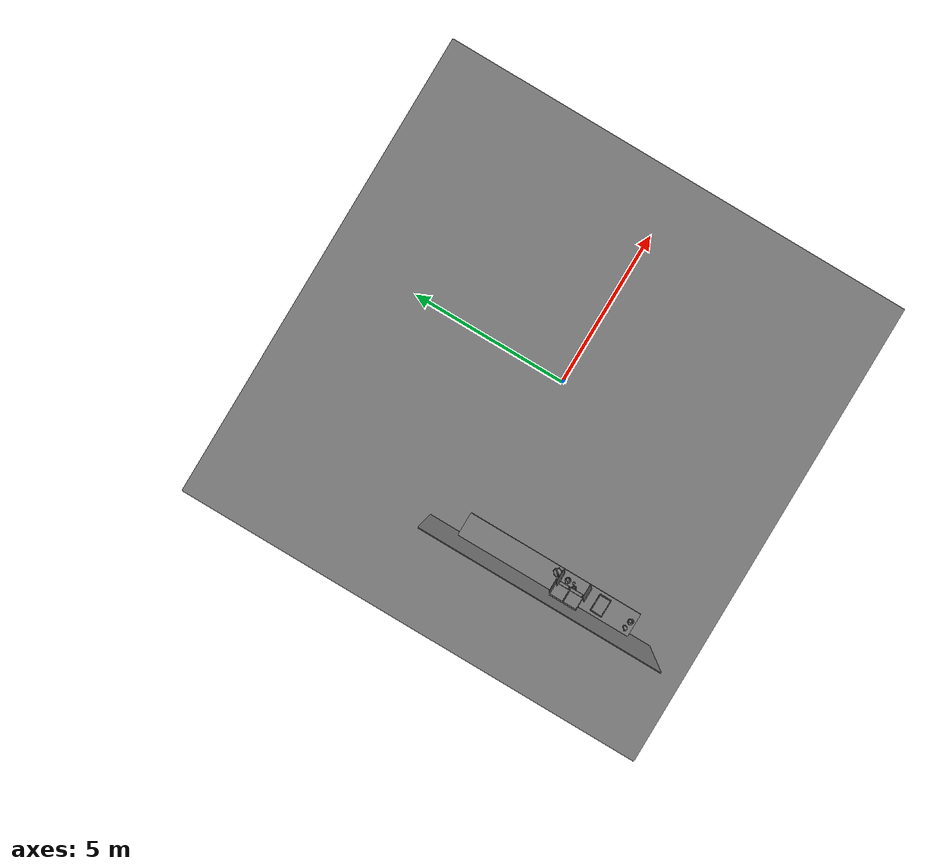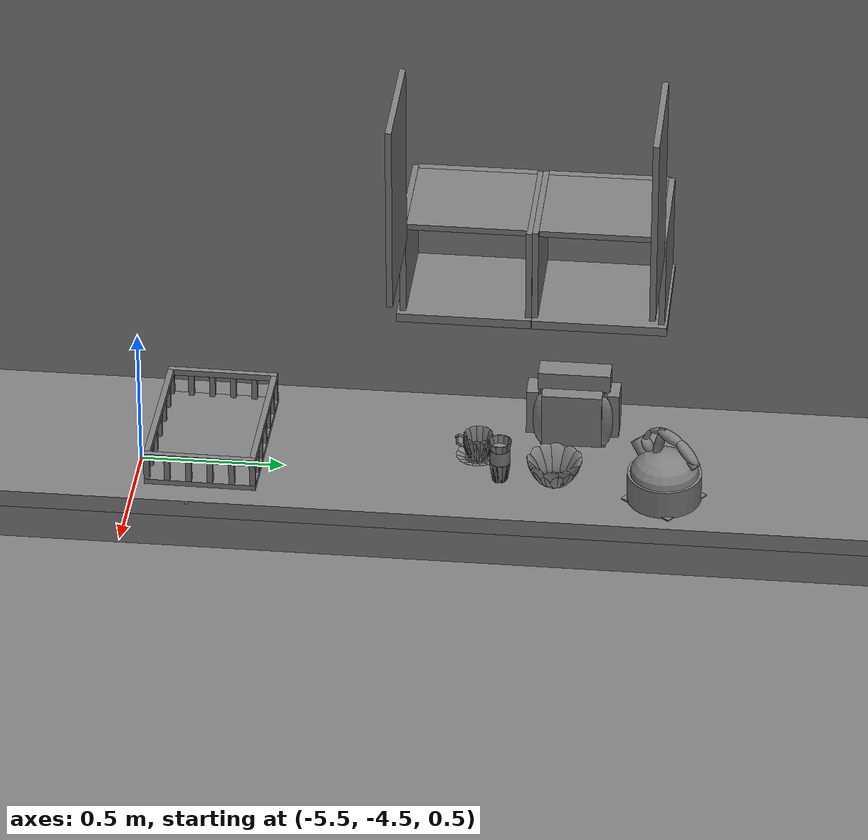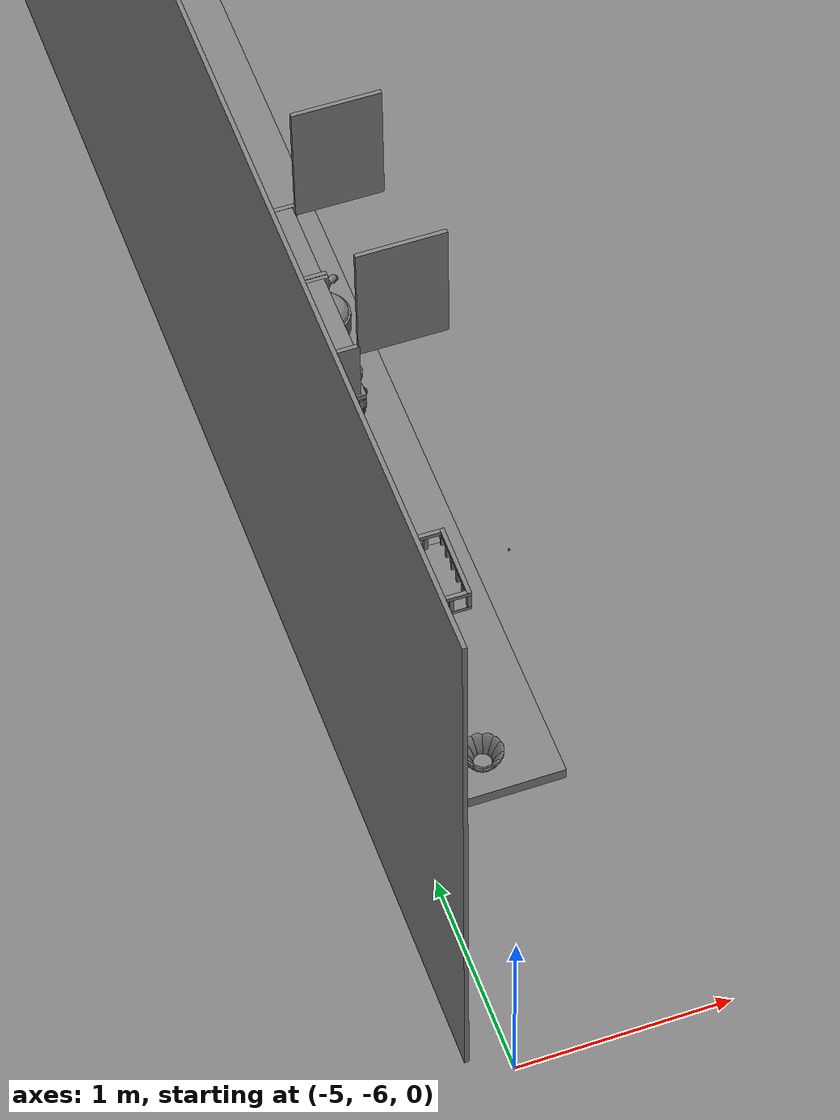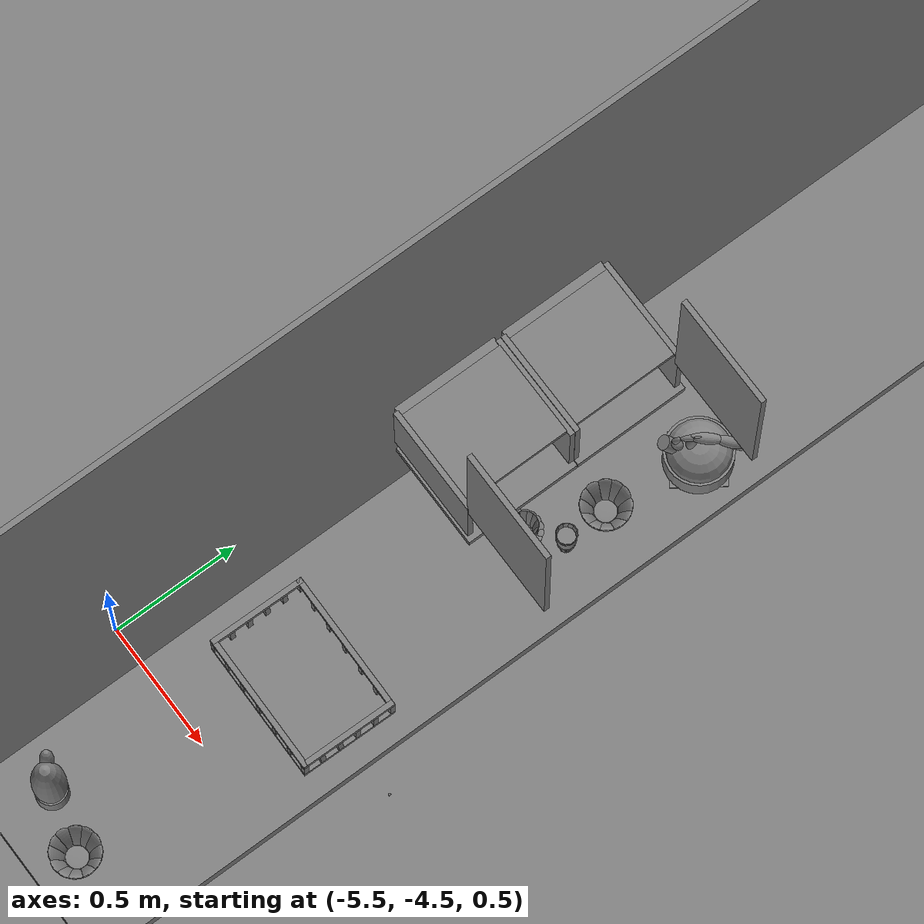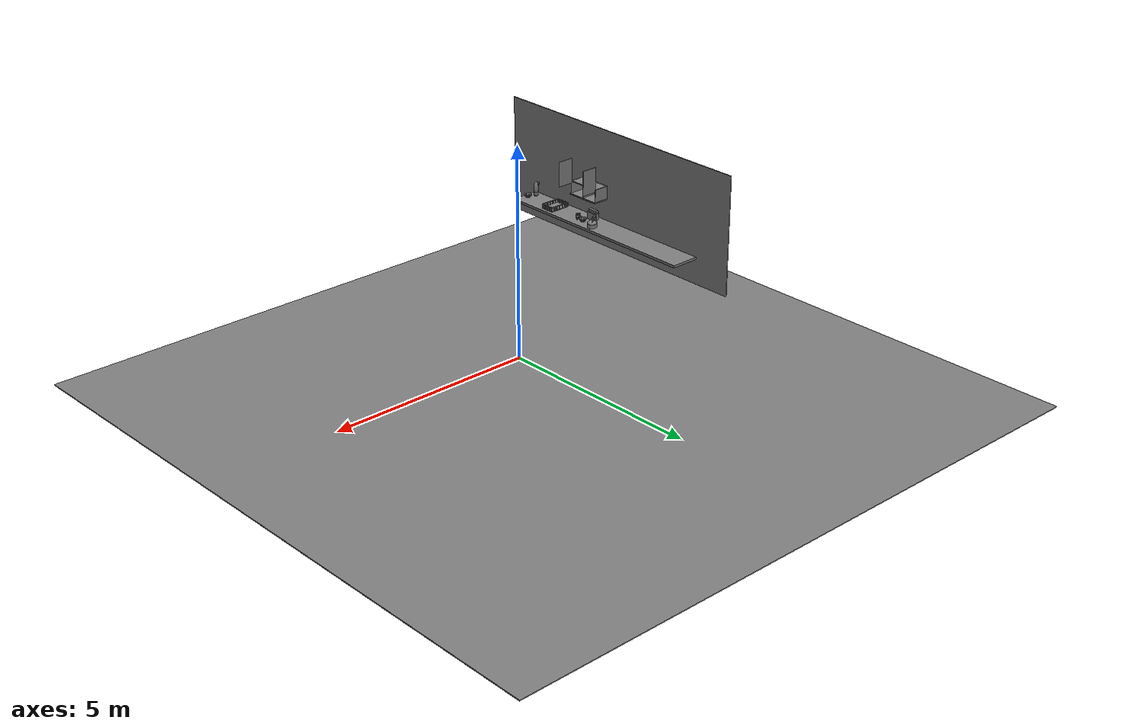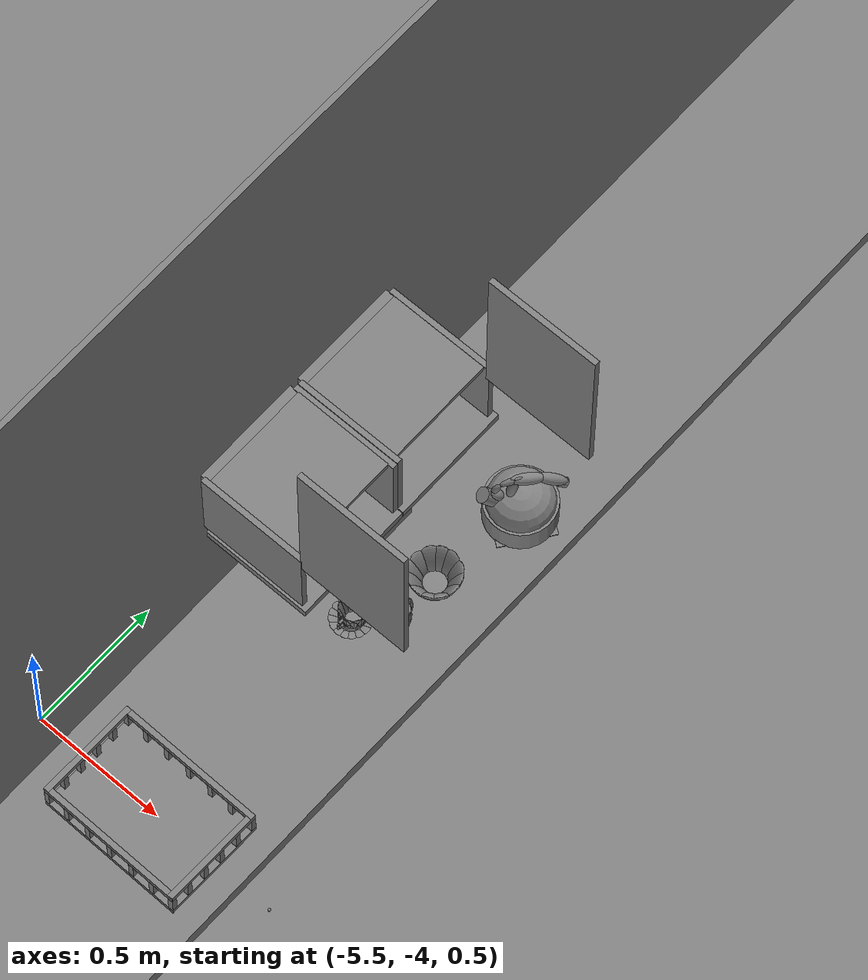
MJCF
<mujoco>
    <option gravity="0.000000000 0.000000000 -9.810000420" timestep="0.0049999999" integrator="implicitfast" density="9.8000002" viscosity="1.8000001e-05" noslip_iterations="10" iterations="100" sdf_iterations="50">
        <flag multiccd="disable"/>
    </option>
    <size memory="1000M"/>
    <compiler coordinate="local"/>
    <worldbody>
        <light cutoff="30" pos="0 1 1" dir="0 -1 -2"/>
        <light cutoff="30" pos="0 -1 1" dir="0 1 -2"/>
        <body pos="-4.860558510 -4.149443150 1.004824519" euler="0.000000000 0.000000000 -90.691108704" name="openloong_gripper_2f85_fix_base_usda_Basket_Kitchen_01">
            <geom contype="1" conaffinity="1" density="1000" type="box" material="" rgba="0.500000000 0.500000000 0.500000000 1.000000000" solimp="0.899999976 0.949999988 0.001000000" friction="1.000000000 0.005000000 0.000100000" solref="0.020000000 1.000000000" margin="0" condim="3" group="0" pos="-0.175679564 -0.000001431 0.109079957" quat="0.707107008 0.000000000 0.000000000 0.707106411" size="0.268999994 0.010000000 0.010500000" name="openloong_gripper_2f85_fix_base_usda_geom_855954EB_18DF_4F8B_95C6_F515B4FE3F77"/>
            <geom contype="1" conaffinity="1" density="1000" type="box" material="" rgba="0.500000000 0.500000000 0.500000000 1.000000000" solimp="0.899999976 0.949999988 0.001000000" friction="1.000000000 0.005000000 0.000100000" solref="0.020000000 1.000000000" margin="0" condim="3" group="0" pos="-0.176020086 0.002992153 0.059861541" quat="0.707107008 0.000000000 0.000000000 0.707106411" size="0.009500000 0.009500000 0.039999999" name="openloong_gripper_2f85_fix_base_usda_geom_3005E040_CEA7_4246_930C_12B8D42A4860"/>
            <geom contype="1" conaffinity="1" density="1000" type="box" material="" rgba="0.500000000 0.500000000 0.500000000 1.000000000" solimp="0.899999976 0.949999988 0.001000000" friction="1.000000000 0.005000000 0.000100000" solref="0.020000000 1.000000000" margin="0" condim="3" group="0" pos="0.176000595 0.002991199 0.059860706" quat="0.707107008 0.000000000 0.000000000 0.707106411" size="0.009500000 0.009500000 0.039999999" name="openloong_gripper_2f85_fix_base_usda_geom_D9E71CEA_4A60_4D16_AB94_1D7E151915A6"/>
            <geom contype="1" conaffinity="1" density="1000" type="box" material="" rgba="0.500000000 0.500000000 0.500000000 1.000000000" solimp="0.899999976 0.949999988 0.001000000" friction="1.000000000 0.005000000 0.000100000" solref="0.020000000 1.000000000" margin="0" condim="3" group="0" pos="0.176003456 0.259475708 0.059860110" quat="0.707107008 0.000000000 0.000000000 0.707106411" size="0.009500000 0.009500000 0.039999999" name="openloong_gripper_2f85_fix_base_usda_geom_D135C7CF_54D1_4CFF_AC08_8498EAF93908"/>
            <geom contype="1" conaffinity="1" density="1000" type="box" material="" rgba="0.500000000 0.500000000 0.500000000 1.000000000" solimp="0.899999976 0.949999988 0.001000000" friction="1.000000000 0.005000000 0.000100000" solref="0.020000000 1.000000000" margin="0" condim="3" group="0" pos="-0.176020026 -0.088695526 0.059861422" quat="0.707107008 0.000000000 0.000000000 0.707106411" size="0.009500000 0.009500000 0.039999999" name="openloong_gripper_2f85_fix_base_usda_geom_65D99F96_7C90_41F6_B8C7_306E9159539F"/>
            <geom contype="1" conaffinity="1" density="1000" type="box" material="" rgba="0.500000000 0.500000000 0.500000000 1.000000000" solimp="0.899999976 0.949999988 0.001000000" friction="1.000000000 0.005000000 0.000100000" solref="0.020000000 1.000000000" margin="0" condim="3" group="0" pos="0.000000119 0.259647846 0.109080195" quat="0.707107008 0.000000000 0.000000000 0.707106411" size="0.010000000 0.185000002 0.010500000" name="openloong_gripper_2f85_fix_base_usda_geom_AC472954_C86C_48CE_89B3_798A8C31256C"/>
            <geom contype="1" conaffinity="1" density="1000" type="box" material="" rgba="0.500000000 0.500000000 0.500000000 1.000000000" solimp="0.899999976 0.949999988 0.001000000" friction="1.000000000 0.005000000 0.000100000" solref="0.020000000 1.000000000" margin="0" condim="3" group="0" pos="0.176002026 -0.259545326 0.059860349" quat="0.707107008 0.000000000 0.000000000 0.707106411" size="0.009500000 0.009500000 0.039999999" name="openloong_gripper_2f85_fix_base_usda_geom_AC233886_B67D_43F5_9E27_E4985E79B4C8"/>
            <geom contype="1" conaffinity="1" density="1000" type="box" material="" rgba="0.500000000 0.500000000 0.500000000 1.000000000" solimp="0.899999976 0.949999988 0.001000000" friction="1.000000000 0.005000000 0.000100000" solref="0.020000000 1.000000000" margin="0" condim="3" group="0" pos="0.036305428 -0.259545326 0.059860706" quat="0.707107008 0.000000000 0.000000000 0.707106411" size="0.009500000 0.009500000 0.039999999" name="openloong_gripper_2f85_fix_base_usda_geom_1A94B3B5_5EE8_4E81_9A00_A82701043024"/>
            <geom contype="1" conaffinity="1" density="1000" type="box" material="" rgba="0.500000000 0.500000000 0.500000000 1.000000000" solimp="0.899999976 0.949999988 0.001000000" friction="1.000000000 0.005000000 0.000100000" solref="0.020000000 1.000000000" margin="0" condim="3" group="0" pos="0.000000000 -0.259647369 0.109080195" quat="0.707107008 0.000000000 0.000000000 0.707106411" size="0.010000000 0.185000002 0.010500000" name="openloong_gripper_2f85_fix_base_usda_geom_D03FCDA9_F09F_44FD_9E1A_CD0FF20C89F1"/>
            <geom contype="1" conaffinity="1" density="1000" type="box" material="" rgba="0.500000000 0.500000000 0.500000000 1.000000000" solimp="0.899999976 0.949999988 0.001000000" friction="1.000000000 0.005000000 0.000100000" solref="0.020000000 1.000000000" margin="0" condim="3" group="0" pos="-0.034950733 -0.259545803 0.059860826" quat="0.707107008 0.000000000 0.000000000 0.707106411" size="0.009500000 0.009500000 0.039999999" name="openloong_gripper_2f85_fix_base_usda_geom_A2F6B47E_8D1B_4B97_8DC2_455B23599FBF"/>
            <geom contype="1" conaffinity="1" density="1000" type="box" material="" rgba="0.500000000 0.500000000 0.500000000 1.000000000" solimp="0.899999976 0.949999988 0.001000000" friction="1.000000000 0.005000000 0.000100000" solref="0.020000000 1.000000000" margin="0" condim="3" group="0" pos="0.108178139 0.259475946 0.059860229" quat="0.707107008 0.000000000 0.000000000 0.707106411" size="0.009500000 0.009500000 0.039999999" name="openloong_gripper_2f85_fix_base_usda_geom_E3F8CB02_A713_411D_B143_4692620DFFD8"/>
            <geom contype="1" conaffinity="1" density="1000" type="box" material="" rgba="0.500000000 0.500000000 0.500000000 1.000000000" solimp="0.899999976 0.949999988 0.001000000" friction="1.000000000 0.005000000 0.000100000" solref="0.020000000 1.000000000" margin="0" condim="3" group="0" pos="-0.106845737 0.259475231 0.059860826" quat="0.707107008 0.000000000 0.000000000 0.707106411" size="0.009500000 0.009500000 0.039999999" name="openloong_gripper_2f85_fix_base_usda_geom_6089B3B1_DBCA_4AB9_8CAB_F52214199020"/>
            <geom contype="1" conaffinity="1" density="1000" type="box" material="" rgba="0.500000000 0.500000000 0.500000000 1.000000000" solimp="0.899999976 0.949999988 0.001000000" friction="1.000000000 0.005000000 0.000100000" solref="0.020000000 1.000000000" margin="0" condim="3" group="0" pos="-0.176020563 0.179506302 0.059861779" quat="0.707107008 0.000000000 0.000000000 0.707106411" size="0.009500000 0.009500000 0.039999999" name="openloong_gripper_2f85_fix_base_usda_geom_6CBF26D8_941D_4746_9124_CF9CB582258C"/>
            <geom contype="1" conaffinity="1" density="1000" type="box" material="" rgba="0.500000000 0.500000000 0.500000000 1.000000000" solimp="0.899999976 0.949999988 0.001000000" friction="1.000000000 0.005000000 0.000100000" solref="0.020000000 1.000000000" margin="0" condim="3" group="0" pos="-0.034949183 0.259475946 0.059860587" quat="0.707107008 0.000000000 0.000000000 0.707106411" size="0.009500000 0.009500000 0.039999999" name="openloong_gripper_2f85_fix_base_usda_geom_BF861ED6_8420_4409_AA35_719B611F7FDD"/>
            <geom contype="1" conaffinity="1" density="1000" type="box" material="" rgba="0.500000000 0.500000000 0.500000000 1.000000000" solimp="0.899999976 0.949999988 0.001000000" friction="1.000000000 0.005000000 0.000100000" solref="0.020000000 1.000000000" margin="0" condim="3" group="0" pos="0.175792217 -0.000001907 0.109079838" quat="0.707107008 0.000000000 0.000000000 0.707106411" size="0.268999994 0.010000000 0.010500000" name="openloong_gripper_2f85_fix_base_usda_geom_A48B5DE1_8E06_4651_92AA_06D5468183A2"/>
            <geom contype="1" conaffinity="1" density="1000" type="box" material="" rgba="0.500000000 0.500000000 0.500000000 1.000000000" solimp="0.899999976 0.949999988 0.001000000" friction="1.000000000 0.005000000 0.000100000" solref="0.020000000 1.000000000" margin="0" condim="3" group="0" pos="-0.000015259 0.000000000 0.010668159" quat="0.707107008 0.000000000 0.000000000 0.707106411" size="0.268999994 0.186000004 0.010500000" name="openloong_gripper_2f85_fix_base_usda_geom_8E98D153_4BBB_43AE_B27E_06F8FAEC2DD2"/>
            <geom contype="1" conaffinity="1" density="1000" type="box" material="" rgba="0.500000000 0.500000000 0.500000000 1.000000000" solimp="0.899999976 0.949999988 0.001000000" friction="1.000000000 0.005000000 0.000100000" solref="0.020000000 1.000000000" margin="0" condim="3" group="0" pos="-0.176020086 0.094225407 0.059861660" quat="0.707107008 0.000000000 0.000000000 0.707106411" size="0.009500000 0.009500000 0.039999999" name="openloong_gripper_2f85_fix_base_usda_geom_D69728D5_465F_42E0_8BA3_286B77203CF6"/>
            <geom contype="1" conaffinity="1" density="1000" type="box" material="" rgba="0.500000000 0.500000000 0.500000000 1.000000000" solimp="0.899999976 0.949999988 0.001000000" friction="1.000000000 0.005000000 0.000100000" solref="0.020000000 1.000000000" margin="0" condim="3" group="0" pos="0.108177185 -0.259544849 0.059860468" quat="0.707107008 0.000000000 0.000000000 0.707106411" size="0.009500000 0.009500000 0.039999999" name="openloong_gripper_2f85_fix_base_usda_geom_27584570_A2BF_4C66_ACED_5EF3B76BC61B"/>
            <geom contype="1" conaffinity="1" density="1000" type="box" material="" rgba="0.500000000 0.500000000 0.500000000 1.000000000" solimp="0.899999976 0.949999988 0.001000000" friction="1.000000000 0.005000000 0.000100000" solref="0.020000000 1.000000000" margin="0" condim="3" group="0" pos="-0.176019967 -0.177031994 0.059861302" quat="0.707107008 0.000000000 0.000000000 0.707106411" size="0.009500000 0.009500000 0.039999999" name="openloong_gripper_2f85_fix_base_usda_geom_3281E289_5C0F_4E00_B248_47CDA23305FA"/>
            <geom contype="1" conaffinity="1" density="1000" type="box" material="" rgba="0.500000000 0.500000000 0.500000000 1.000000000" solimp="0.899999976 0.949999988 0.001000000" friction="1.000000000 0.005000000 0.000100000" solref="0.020000000 1.000000000" margin="0" condim="3" group="0" pos="-0.176020026 -0.259545326 0.059861183" quat="0.707107008 0.000000000 0.000000000 0.707106411" size="0.009500000 0.009500000 0.039999999" name="openloong_gripper_2f85_fix_base_usda_geom_689C812B_4B71_4674_A9D1_2A07B658FB3C"/>
            <geom contype="1" conaffinity="1" density="1000" type="box" material="" rgba="0.500000000 0.500000000 0.500000000 1.000000000" solimp="0.899999976 0.949999988 0.001000000" friction="1.000000000 0.005000000 0.000100000" solref="0.020000000 1.000000000" margin="0" condim="3" group="0" pos="-0.106846333 -0.259546280 0.059861064" quat="0.707107008 0.000000000 0.000000000 0.707106411" size="0.009500000 0.009500000 0.039999999" name="openloong_gripper_2f85_fix_base_usda_geom_3EEAC5AA_C9D3_4D3C_9178_2F4E65EC63A5"/>
            <geom contype="1" conaffinity="1" density="1000" type="box" material="" rgba="0.500000000 0.500000000 0.500000000 1.000000000" solimp="0.899999976 0.949999988 0.001000000" friction="1.000000000 0.005000000 0.000100000" solref="0.020000000 1.000000000" margin="0" condim="3" group="0" pos="0.176000595 0.094224453 0.059860826" quat="0.707107008 0.000000000 0.000000000 0.707106411" size="0.009500000 0.009500000 0.039999999" name="openloong_gripper_2f85_fix_base_usda_geom_941BD05E_7FF1_4DCB_A3E9_E3BF9E8497AB"/>
            <geom contype="1" conaffinity="1" density="1000" type="box" material="" rgba="0.500000000 0.500000000 0.500000000 1.000000000" solimp="0.899999976 0.949999988 0.001000000" friction="1.000000000 0.005000000 0.000100000" solref="0.020000000 1.000000000" margin="0" condim="3" group="0" pos="0.176001072 -0.088696480 0.059860587" quat="0.707107008 0.000000000 0.000000000 0.707106411" size="0.009500000 0.009500000 0.039999999" name="openloong_gripper_2f85_fix_base_usda_geom_57428755_ACC2_41D3_B645_28C22D60ED5B"/>
            <geom contype="1" conaffinity="1" density="1000" type="box" material="" rgba="0.500000000 0.500000000 0.500000000 1.000000000" solimp="0.899999976 0.949999988 0.001000000" friction="1.000000000 0.005000000 0.000100000" solref="0.020000000 1.000000000" margin="0" condim="3" group="0" pos="0.036307096 0.259476185 0.059860468" quat="0.707107008 0.000000000 0.000000000 0.707106411" size="0.009500000 0.009500000 0.039999999" name="openloong_gripper_2f85_fix_base_usda_geom_BC97FFA0_EB25_4372_83AB_5AFF8BC8FCE6"/>
            <geom contype="1" conaffinity="1" density="1000" type="box" material="" rgba="0.500000000 0.500000000 0.500000000 1.000000000" solimp="0.899999976 0.949999988 0.001000000" friction="1.000000000 0.005000000 0.000100000" solref="0.020000000 1.000000000" margin="0" condim="3" group="0" pos="0.176001549 -0.177031994 0.059860468" quat="0.707107008 0.000000000 0.000000000 0.707106411" size="0.009500000 0.009500000 0.039999999" name="openloong_gripper_2f85_fix_base_usda_geom_AF464B64_8697_4727_B144_2003F4B17C66"/>
            <geom contype="1" conaffinity="1" density="1000" type="box" material="" rgba="0.500000000 0.500000000 0.500000000 1.000000000" solimp="0.899999976 0.949999988 0.001000000" friction="1.000000000 0.005000000 0.000100000" solref="0.020000000 1.000000000" margin="0" condim="3" group="0" pos="0.176000118 0.179505348 0.059860945" quat="0.707107008 0.000000000 0.000000000 0.707106411" size="0.009500000 0.009500000 0.039999999" name="openloong_gripper_2f85_fix_base_usda_geom_A52FAE56_D310_45A3_94D1_9ECE8E91080E"/>
            <geom contype="1" conaffinity="1" density="1000" type="box" material="" rgba="0.500000000 0.500000000 0.500000000 1.000000000" solimp="0.899999976 0.949999988 0.001000000" friction="1.000000000 0.005000000 0.000100000" solref="0.020000000 1.000000000" margin="0" condim="3" group="0" pos="-0.176020086 0.259474993 0.059860945" quat="0.707107008 0.000000000 0.000000000 0.707106411" size="0.009500000 0.009500000 0.039999999" name="openloong_gripper_2f85_fix_base_usda_geom_6C580EAD_3C08_4DBB_B69C_2C60787DE59C"/>
            <freejoint name="openloong_gripper_2f85_fix_base_usda_Basket_Kitchen_01_joint"/>
        </body>
        <body pos="-4.802892208 -3.488179445 1.876015186" euler="89.999992371 -89.999946594 0.000000000" name="Interactive Objcets_guimen_01">
            <geom contype="1" conaffinity="1" density="1000" type="box" material="" rgba="0.500000000 0.500000000 0.500000000 1.000000000" solimp="0.899999976 0.949999988 0.001000000" friction="1.000000000 0.005000000 0.000100000" solref="0.020000000 1.000000000" margin="0" condim="3" group="0" pos="0.006727934 0.314709902 -0.203009605" quat="1.000000000 0.000000119 -0.000000119 0.000000000" size="0.010000000 0.317999989 0.204999998" name="Interactive Objcets_geom_244E57C4_5629_4097_A834_E3A20410359B"/>
            <joint armature="0" stiffness="0" damping="1" axis="0.000000 1.000000 0.000000" type="hinge" name="Interactive Objcets_guimen_01"/>
        </body>
        <body pos="-4.805274963 -2.665403366 1.876015186" euler="89.999877930 89.999969482 0.000000000" name="Interactive Objcets_guimen_02">
            <geom contype="1" conaffinity="1" density="1000" type="box" material="" rgba="0.500000000 0.500000000 0.500000000 1.000000000" solimp="0.899999976 0.949999988 0.001000000" friction="1.000000000 0.005000000 0.000100000" solref="0.020000000 1.000000000" margin="0" condim="3" group="0" pos="0.006727815 0.314709663 0.203009367" quat="0.999999940 0.000000000 0.000000000 0.000000000" size="0.010000000 0.317999989 0.204999998" name="Interactive Objcets_geom_BBBCE272_900D_4D46_A407_0FCC7C96AAFC"/>
            <joint armature="0" stiffness="0" damping="1" axis="0.000000 1.000000 0.000000" type="hinge" name="Interactive Objcets_guimen_02"/>
        </body>
        <body pos="-4.827295780 -3.287638187 1.074643731" euler="0.000000000 0.000000000 89.999992371" name="Interactive Objcets_coffeecup_01">
            <geom contype="1" conaffinity="1" density="1000" type="ellipsoid" material="" rgba="0.500000000 0.500000000 0.500000000 1.000000000" solimp="0.899999976 0.949999988 0.001000000" friction="1.000000000 0.005000000 0.000100000" solref="0.020000000 1.000000000" margin="0" condim="3" group="0" pos="0.035336256 0.000558376 -0.043215394" quat="0.999999881 0.000000000 0.000000000 0.000000000" size="0.029999999 0.029999999 0.001000000" name="Interactive Objcets_geom_21045954_A4C2_4A4D_8B83_6D17A528C72E"/>
            <geom contype="1" conaffinity="1" density="1000" type="ellipsoid" material="" rgba="0.500000000 0.500000000 0.500000000 1.000000000" solimp="0.899999976 0.949999988 0.001000000" friction="1.000000000 0.005000000 0.000100000" solref="0.020000000 1.000000000" margin="0" condim="3" group="0" pos="0.067416430 -0.018191338 0.002976775" quat="0.961934388 0.024418317 0.091648072 -0.256293803" size="0.005000000 0.029999999 0.048999999" name="Interactive Objcets_geom_BDC97AFC_FF7F_4EDD_9482_28A74F955BAB"/>
            <geom contype="1" conaffinity="1" density="1000" type="ellipsoid" material="" rgba="0.500000000 0.500000000 0.500000000 1.000000000" solimp="0.899999976 0.949999988 0.001000000" friction="1.000000000 0.005000000 0.000100000" solref="0.020000000 1.000000000" margin="0" condim="3" group="0" pos="0.034471050 -0.037125111 0.002976775" quat="0.701517045 0.067293778 0.066836871 -0.706313014" size="0.005000000 0.029999999 0.048999999" name="Interactive Objcets_geom_7837EC73_100B_4239_AAF4_4D117F037F52"/>
            <geom contype="1" conaffinity="1" density="1000" type="ellipsoid" material="" rgba="0.500000000 0.500000000 0.500000000 1.000000000" solimp="0.899999976 0.949999988 0.001000000" friction="1.000000000 0.005000000 0.000100000" solref="0.020000000 1.000000000" margin="0" condim="3" group="0" pos="0.035336256 0.000558376 -0.045152068" quat="0.999999881 0.000000000 0.000000000 0.000000000" size="0.029999999 0.029999999 0.001000000" name="Interactive Objcets_geom_325243F2_5234_4329_A426_835613EE54F3"/>
            <geom contype="1" conaffinity="1" density="1000" type="ellipsoid" material="" rgba="0.500000000 0.500000000 0.500000000 1.000000000" solimp="0.899999976 0.949999988 0.001000000" friction="1.000000000 0.005000000 0.000100000" solref="0.020000000 1.000000000" margin="0" condim="3" group="0" pos="0.001010895 -0.016271591 0.002976775" quat="0.228377163 0.092315644 0.021758538 -0.968941689" size="0.005000000 0.029999999 0.048999999" name="Interactive Objcets_geom_EC818804_6256_4C74_84E3_69D1CDE3CB28"/>
            <geom contype="1" conaffinity="1" density="1000" type="capsule" material="" rgba="0.500000000 0.500000000 0.500000000 1.000000000" solimp="0.899999976 0.949999988 0.001000000" friction="1.000000000 0.005000000 0.000100000" solref="0.020000000 1.000000000" margin="0" condim="3" group="0" pos="-0.021276474 0.000000000 0.038509369" quat="0.633189917 0.000000000 0.773996413 0.000000000" size="0.004000000 0.009000000 1.000000000" name="Interactive Objcets_geom_4F2DBEA4_E148_4033_8B12_4F32027744FE"/>
            <geom contype="1" conaffinity="1" density="1000" type="capsule" material="" rgba="0.500000000 0.500000000 0.500000000 1.000000000" solimp="0.899999976 0.949999988 0.001000000" friction="1.000000000 0.005000000 0.000100000" solref="0.020000000 1.000000000" margin="0" condim="3" group="0" pos="-0.018014431 0.000000000 0.001762271" quat="0.707106769 -0.000000004 0.707106709 -0.000000088" size="0.004000000 0.005000000 1.000000000" name="Interactive Objcets_geom_8F2F31A5_C736_4680_A055_67F5DB46FC6E"/>
            <geom contype="1" conaffinity="1" density="1000" type="ellipsoid" material="" rgba="0.500000000 0.500000000 0.500000000 1.000000000" solimp="0.899999976 0.949999988 0.001000000" friction="1.000000000 0.005000000 0.000100000" solref="0.020000000 1.000000000" margin="0" condim="3" group="0" pos="0.068445444 0.017385960 0.002976775" quat="0.228377223 -0.092319682 -0.021759447 -0.968941331" size="0.005000000 0.029999999 0.048999999" name="Interactive Objcets_geom_529A9DF5_E54F_43AB_A0CE_4924A9EAE7D4"/>
            <geom contype="1" conaffinity="1" density="1000" type="ellipsoid" material="" rgba="0.500000000 0.500000000 0.500000000 1.000000000" solimp="0.899999976 0.949999988 0.001000000" friction="1.000000000 0.005000000 0.000100000" solref="0.020000000 1.000000000" margin="0" condim="3" group="0" pos="0.002039194 0.019308567 0.002976775" quat="0.961933970 -0.024419386 -0.091652036 -0.256293654" size="0.005000000 0.029999999 0.048999999" name="Interactive Objcets_geom_BA2820CA_EBD2_41DE_B4EE_EF06FC7EFFC4"/>
            <geom contype="1" conaffinity="1" density="1000" type="ellipsoid" material="" rgba="0.500000000 0.500000000 0.500000000 1.000000000" solimp="0.899999976 0.949999988 0.001000000" friction="1.000000000 0.005000000 0.000100000" solref="0.020000000 1.000000000" margin="0" condim="3" group="0" pos="0.034984604 0.038240910 0.002976775" quat="0.701516926 -0.067296736 -0.066839755 -0.706312656" size="0.005000000 0.029999999 0.048999999" name="Interactive Objcets_geom_347CF0D1_8A32_4E86_958B_9B910979A749"/>
            <geom contype="1" conaffinity="1" density="1000" type="ellipsoid" material="" rgba="0.500000000 0.500000000 0.500000000 1.000000000" solimp="0.899999976 0.949999988 0.001000000" friction="1.000000000 0.005000000 0.000100000" solref="0.020000000 1.000000000" margin="0" condim="3" group="0" pos="0.017669693 0.034160614 0.002976775" quat="0.848410904 -0.049618516 -0.080835648 -0.520770907" size="0.005000000 0.029999999 0.048999999" name="Interactive Objcets_geom_039E654A_255A_42C3_A0A2_84D5495EF877"/>
            <geom contype="1" conaffinity="1" density="1000" type="ellipsoid" material="" rgba="0.500000000 0.500000000 0.500000000 1.000000000" solimp="0.899999976 0.949999988 0.001000000" friction="1.000000000 0.005000000 0.000100000" solref="0.020000000 1.000000000" margin="0" condim="3" group="0" pos="-0.002956629 0.000558376 0.002976775" quat="0.995491505 0.000000004 -0.094849378 -0.000000089" size="0.005000000 0.029999999 0.048999999" name="Interactive Objcets_geom_639C80F8_7D93_472C_985E_600100185520"/>
            <geom contype="1" conaffinity="1" density="1000" type="ellipsoid" material="" rgba="0.500000000 0.500000000 0.500000000 1.000000000" solimp="0.899999976 0.949999988 0.001000000" friction="1.000000000 0.005000000 0.000100000" solref="0.020000000 1.000000000" margin="0" condim="3" group="0" pos="0.051787138 -0.033043861 0.002976775" quat="0.848411202 0.049616337 0.080832161 -0.520771146" size="0.005000000 0.029999999 0.048999999" name="Interactive Objcets_geom_1BAB5310_E6AF_45E2_9C93_D25547DD3FE4"/>
            <geom contype="1" conaffinity="1" density="1000" type="capsule" material="" rgba="0.500000000 0.500000000 0.500000000 1.000000000" solimp="0.899999976 0.949999988 0.001000000" friction="1.000000000 0.005000000 0.000100000" solref="0.020000000 1.000000000" margin="0" condim="3" group="0" pos="-0.030251026 0.000000000 0.004966617" quat="0.480583906 -0.000000000 0.876948774 -0.000000126" size="0.004000000 0.005000000 1.000000000" name="Interactive Objcets_geom_BAFCC4CF_FE2A_47F7_8ED9_586029B74002"/>
            <geom contype="1" conaffinity="1" density="1000" type="capsule" material="" rgba="0.500000000 0.500000000 0.500000000 1.000000000" solimp="0.899999976 0.949999988 0.001000000" friction="1.000000000 0.005000000 0.000100000" solref="0.020000000 1.000000000" margin="0" condim="3" group="0" pos="-0.036300898 0.000000000 0.021037936" quat="0.044551343 -0.000000000 0.999007046 -0.000000126" size="0.004000000 0.012000000 1.000000000" name="Interactive Objcets_geom_2530CBB9_3115_475C_968F_89B9CA5883AD"/>
            <geom contype="1" conaffinity="1" density="1000" type="capsule" material="" rgba="0.500000000 0.500000000 0.500000000 1.000000000" solimp="0.899999976 0.949999988 0.001000000" friction="1.000000000 0.005000000 0.000100000" solref="0.020000000 1.000000000" margin="0" condim="3" group="0" pos="-0.008219719 0.000000000 -0.000944734" quat="0.364379913 0.000000063 0.931250274 -0.000000063" size="0.004000000 0.003000000 1.000000000" name="Interactive Objcets_geom_832E75B3_8B53_44C0_B16A_CF44966886AB"/>
            <geom contype="1" conaffinity="1" density="1000" type="capsule" material="" rgba="0.500000000 0.500000000 0.500000000 1.000000000" solimp="0.899999976 0.949999988 0.001000000" friction="1.000000000 0.005000000 0.000100000" solref="0.020000000 1.000000000" margin="0" condim="3" group="0" pos="-0.033022881 0.000000000 0.037873149" quat="0.874267220 0.000000042 0.485444903 -0.000000084" size="0.004000000 0.004000000 1.000000000" name="Interactive Objcets_geom_DB29E33E_405C_4D28_84B7_B03D7493F68E"/>
            <geom contype="1" conaffinity="1" density="1000" type="ellipsoid" material="" rgba="0.500000000 0.500000000 0.500000000 1.000000000" solimp="0.899999976 0.949999988 0.001000000" friction="1.000000000 0.005000000 0.000100000" solref="0.020000000 1.000000000" margin="0" condim="3" group="0" pos="0.015755907 -0.032001972 0.002976775" quat="0.496025920 0.082232773 0.047258731 -0.863112032" size="0.005000000 0.029999999 0.048999999" name="Interactive Objcets_geom_82D11A47_7964_4289_8ED5_8F629216E97B"/>
            <geom contype="1" conaffinity="1" density="1000" type="ellipsoid" material="" rgba="0.500000000 0.500000000 0.500000000 1.000000000" solimp="0.899999976 0.949999988 0.001000000" friction="1.000000000 0.005000000 0.000100000" solref="0.020000000 1.000000000" margin="0" condim="3" group="0" pos="0.072411790 0.000558376 0.002976775" quat="0.995491922 -0.000000019 0.094845265 -0.000000089" size="0.005000000 0.029999999 0.048999999" name="Interactive Objcets_geom_9D549F11_70BE_4DA2_9F93_4D5E1A14EB2E"/>
            <geom contype="1" conaffinity="1" density="1000" type="ellipsoid" material="" rgba="0.500000000 0.500000000 0.500000000 1.000000000" solimp="0.899999976 0.949999988 0.001000000" friction="1.000000000 0.005000000 0.000100000" solref="0.020000000 1.000000000" margin="0" condim="3" group="0" pos="0.053700209 0.033117294 0.002976775" quat="0.496025741 -0.082236379 -0.047260769 -0.863111615" size="0.005000000 0.029999999 0.048999999" name="Interactive Objcets_geom_43C05901_4F57_4A69_8CCC_F7F19ED71901"/>
            <freejoint name="Interactive Objcets_coffeecup_01"/>
        </body>
        <body pos="-5.020127296 -2.953741550 1.135127425" euler="89.999946594 0.000000000 0.000000000" name="Interactive Objcets_Bread">
            <geom contype="1" conaffinity="1" density="1000" type="box" material="" rgba="0.500000000 0.500000000 0.500000000 1.000000000" solimp="0.899999976 0.949999988 0.001000000" friction="1.000000000 0.005000000 0.000100000" solref="0.020000000 1.000000000" margin="0" condim="3" group="0" pos="-0.008702755 -0.017670274 -0.135069147" quat="0.707107067 -0.707106471 0.000000021 -0.000000021" size="0.045000002 0.020000000 0.079999998" name="Interactive Objcets_geom_C999987E_03F4_4DCC_B569_DA390A5E700D"/>
            <geom contype="1" conaffinity="1" density="1000" type="box" material="" rgba="0.500000000 0.500000000 0.500000000 1.000000000" solimp="0.899999976 0.949999988 0.001000000" friction="1.000000000 0.005000000 0.000100000" solref="0.020000000 1.000000000" margin="0" condim="3" group="0" pos="0.033925056 -0.123201847 0.086778767" quat="0.707107067 -0.707106471 0.000000021 -0.000000021" size="0.020000000 0.020000000 0.005000000" name="Interactive Objcets_geom_02EDC5A8_AC94_4A60_BD64_FDBCD2CB0724"/>
            <geom contype="1" conaffinity="1" density="1000" type="box" material="" rgba="0.500000000 0.500000000 0.500000000 1.000000000" solimp="0.899999976 0.949999988 0.001000000" friction="1.000000000 0.005000000 0.000100000" solref="0.020000000 1.000000000" margin="0" condim="3" group="0" pos="-0.008702755 -0.016588926 0.000174277" quat="0.707107067 -0.707106471 0.000000021 -0.000000021" size="0.090000004 0.100000001 0.094999999" name="Interactive Objcets_geom_EB2A8F7D_4F02_4F09_A858_5B7463A97697"/>
            <geom contype="1" conaffinity="1" density="1000" type="ellipsoid" material="" rgba="0.500000000 0.500000000 0.500000000 1.000000000" solimp="0.899999976 0.949999988 0.001000000" friction="1.000000000 0.005000000 0.000100000" solref="0.020000000 1.000000000" margin="0" condim="3" group="0" pos="-0.067312241 -0.026057482 -0.101716787" quat="0.707107067 -0.707106471 0.000000021 -0.000000021" size="0.020000000 0.029999999 0.094999999" name="Interactive Objcets_geom_79AA1C9D_F0B4_4558_ACDE_25CA571DC6C0"/>
            <geom contype="1" conaffinity="1" density="1000" type="ellipsoid" material="" rgba="0.500000000 0.500000000 0.500000000 1.000000000" solimp="0.899999976 0.949999988 0.001000000" friction="1.000000000 0.005000000 0.000100000" solref="0.020000000 1.000000000" margin="0" condim="3" group="0" pos="0.052222252 -0.026057363 0.101459242" quat="0.707107067 -0.707106471 0.000000021 -0.000000021" size="0.020000000 0.029999999 0.094999999" name="Interactive Objcets_geom_6D8226BF_5BAC_4D0B_8127_30C06A3CA1E8"/>
            <geom contype="1" conaffinity="1" density="1000" type="box" material="" rgba="0.500000000 0.500000000 0.500000000 1.000000000" solimp="0.899999976 0.949999988 0.001000000" friction="1.000000000 0.005000000 0.000100000" solref="0.020000000 1.000000000" margin="0" condim="3" group="0" pos="-0.050020695 -0.123201847 0.086778767" quat="0.707107067 -0.707106471 0.000000021 -0.000000021" size="0.020000000 0.020000000 0.005000000" name="Interactive Objcets_geom_32A88A24_1A62_4C90_B72B_704E8A024FE3"/>
            <geom contype="1" conaffinity="1" density="1000" type="box" material="" rgba="0.500000000 0.500000000 0.500000000 1.000000000" solimp="0.899999976 0.949999988 0.001000000" friction="1.000000000 0.005000000 0.000100000" solref="0.020000000 1.000000000" margin="0" condim="3" group="0" pos="0.033925056 -0.123201728 -0.092369899" quat="0.707107067 -0.707106471 0.000000021 -0.000000021" size="0.020000000 0.020000000 0.005000000" name="Interactive Objcets_geom_D088757F_3BFA_49F5_8EC3_43590B666E4D"/>
            <geom contype="1" conaffinity="1" density="1000" type="ellipsoid" material="" rgba="0.500000000 0.500000000 0.500000000 1.000000000" solimp="0.899999976 0.949999988 0.001000000" friction="1.000000000 0.005000000 0.000100000" solref="0.020000000 1.000000000" margin="0" condim="3" group="0" pos="-0.069190502 -0.026057363 0.101458766" quat="0.707107067 -0.707106471 0.000000021 -0.000000021" size="0.020000000 0.029999999 0.094999999" name="Interactive Objcets_geom_EB9D260E_BB9A_4601_91D7_6DF6F7328E7E"/>
            <geom contype="1" conaffinity="1" density="1000" type="box" material="" rgba="0.500000000 0.500000000 0.500000000 1.000000000" solimp="0.899999976 0.949999988 0.001000000" friction="1.000000000 0.005000000 0.000100000" solref="0.020000000 1.000000000" margin="0" condim="3" group="0" pos="-0.008702755 -0.017670155 0.134585604" quat="0.707107067 -0.707106471 0.000000021 -0.000000021" size="0.045000002 0.020000000 0.079999998" name="Interactive Objcets_geom_6A22F383_CF90_4777_9030_8DF40E53DB82"/>
            <geom contype="1" conaffinity="1" density="1000" type="box" material="" rgba="0.500000000 0.500000000 0.500000000 1.000000000" solimp="0.899999976 0.949999988 0.001000000" friction="1.000000000 0.005000000 0.000100000" solref="0.020000000 1.000000000" margin="0" condim="3" group="0" pos="-0.050020695 -0.123201728 -0.092370376" quat="0.707107067 -0.707106471 0.000000021 -0.000000021" size="0.020000000 0.020000000 0.005000000" name="Interactive Objcets_geom_53919DF6_F300_4F7C_BD83_57436ECDFF63"/>
            <geom contype="1" conaffinity="1" density="1000" type="box" material="" rgba="0.500000000 0.500000000 0.500000000 1.000000000" solimp="0.899999976 0.949999988 0.001000000" friction="1.000000000 0.005000000 0.000100000" solref="0.020000000 1.000000000" margin="0" condim="3" group="0" pos="-0.008702755 0.104617000 -0.003706597" quat="0.707107067 -0.707106471 0.000000021 -0.000000021" size="0.039999999 0.119999997 0.030999999" name="Interactive Objcets_geom_B3511B60_87C4_4EE4_93AF_92E853055296"/>
            <geom contype="1" conaffinity="1" density="1000" type="ellipsoid" material="" rgba="0.500000000 0.500000000 0.500000000 1.000000000" solimp="0.899999976 0.949999988 0.001000000" friction="1.000000000 0.005000000 0.000100000" solref="0.020000000 1.000000000" margin="0" condim="3" group="0" pos="0.052222252 -0.026057243 -0.106481344" quat="0.707107067 -0.707106471 0.000000021 -0.000000021" size="0.020000000 0.029999999 0.094999999" name="Interactive Objcets_geom_A70AFC81_AF8D_44C5_989A_4A5B4F9C261F"/>
            <freejoint name="Interactive Objcets_Bread"/>
        </body>
        <body pos="-4.821335316 -5.105734825 1.007418752" euler="0.000000000 0.000000000 89.999946594" name="Interactive Objcets_bow_04">
            <geom contype="1" conaffinity="1" density="1000" type="ellipsoid" material="" rgba="0.500000000 0.500000000 0.500000000 1.000000000" solimp="0.899999976 0.949999988 0.001000000" friction="1.000000000 0.005000000 0.000100000" solref="0.020000000 1.000000000" margin="0" condim="3" group="0" pos="0.052321672 -0.040297985 0.044118762" quat="0.919264674 0.076882720 0.225593746 -0.313287675" size="0.010000000 0.039999999 0.052000001" name="Interactive Objcets_geom_A1731ED7_62D1_436F_84FE_5E01A05E1614"/>
            <geom contype="1" conaffinity="1" density="1000" type="ellipsoid" material="" rgba="0.500000000 0.500000000 0.500000000 1.000000000" solimp="0.899999976 0.949999988 0.001000000" friction="1.000000000 0.005000000 0.000100000" solref="0.020000000 1.000000000" margin="0" condim="3" group="0" pos="0.059080124 0.029511929 0.044118762" quat="0.223252952 -0.231952190 -0.054787360 -0.945174456" size="0.010000000 0.039999999 0.052000001" name="Interactive Objcets_geom_D6D4B6BB_F928_46AD_89A3_39871AE135F5"/>
            <geom contype="1" conaffinity="1" density="1000" type="ellipsoid" material="" rgba="0.500000000 0.500000000 0.500000000 1.000000000" solimp="0.899999976 0.949999988 0.001000000" friction="1.000000000 0.005000000 0.000100000" solref="0.020000000 1.000000000" margin="0" condim="3" group="0" pos="0.000082970 0.000000000 0.003118873" quat="1.000000000 0.000000000 0.000000000 0.000000000" size="0.039999999 0.039999999 0.002000000" name="Interactive Objcets_geom_C869AED0_AF82_432C_BBFB_5A8960C3531B"/>
            <geom contype="1" conaffinity="1" density="1000" type="ellipsoid" material="" rgba="0.500000000 0.500000000 0.500000000 1.000000000" solimp="0.899999976 0.949999988 0.001000000" friction="1.000000000 0.005000000 0.000100000" solref="0.020000000 1.000000000" margin="0" condim="3" group="0" pos="-0.040080309 -0.052354813 0.044118762" quat="0.429593146 0.213749856 0.105425127 -0.871003032" size="0.010000000 0.039999999 0.052000001" name="Interactive Objcets_geom_1B0F24F0_B2E0_42D6_A003_FDED6C0C7A01"/>
            <geom contype="1" conaffinity="1" density="1000" type="ellipsoid" material="" rgba="0.500000000 0.500000000 0.500000000 1.000000000" solimp="0.899999976 0.949999988 0.001000000" friction="1.000000000 0.005000000 0.000100000" solref="0.020000000 1.000000000" margin="0" condim="3" group="0" pos="0.000243664 -0.065983295 0.044118762" quat="0.687598884 0.168314576 0.168741226 -0.685860336" size="0.010000000 0.039999999 0.052000001" name="Interactive Objcets_geom_4CEE3D64_F435_40F0_908E_2EC7301E0C85"/>
            <geom contype="1" conaffinity="1" density="1000" type="ellipsoid" material="" rgba="0.500000000 0.500000000 0.500000000 1.000000000" solimp="0.899999976 0.949999988 0.001000000" friction="1.000000000 0.005000000 0.000100000" solref="0.020000000 1.000000000" margin="0" condim="3" group="0" pos="-0.065898657 -0.000007629 0.044118762" quat="0.971183062 -0.000000142 -0.238334835 0.000000030" size="0.010000000 0.039999999 0.052000001" name="Interactive Objcets_geom_692EA209_65BE_44E2_9AA5_2AE6E2BBF029"/>
            <geom contype="1" conaffinity="1" density="1000" type="ellipsoid" material="" rgba="0.500000000 0.500000000 0.500000000 1.000000000" solimp="0.899999976 0.949999988 0.001000000" friction="1.000000000 0.005000000 0.000100000" solref="0.020000000 1.000000000" margin="0" condim="3" group="0" pos="-0.052167892 0.040281773 0.044118762" quat="0.919264615 -0.076883025 -0.225593626 -0.313287735" size="0.010000000 0.039999999 0.052000001" name="Interactive Objcets_geom_652F91CC_6798_44CB_B5C3_69B43ABFE8F6"/>
            <geom contype="1" conaffinity="1" density="1000" type="ellipsoid" material="" rgba="0.500000000 0.500000000 0.500000000 1.000000000" solimp="0.899999976 0.949999988 0.001000000" friction="1.000000000 0.005000000 0.000100000" solref="0.020000000 1.000000000" margin="0" condim="3" group="0" pos="-0.029293537 0.059069157 0.044118762" quat="0.825556040 -0.125530839 -0.202596709 -0.511521041" size="0.010000000 0.039999999 0.052000001" name="Interactive Objcets_geom_1CC52DE4_C4C7_4D5E_8C8A_706D8258A7C2"/>
            <geom contype="1" conaffinity="1" density="1000" type="ellipsoid" material="" rgba="0.500000000 0.500000000 0.500000000 1.000000000" solimp="0.899999976 0.949999988 0.001000000" friction="1.000000000 0.005000000 0.000100000" solref="0.020000000 1.000000000" margin="0" condim="3" group="0" pos="0.000082970 0.000000000 0.000446677" quat="1.000000000 0.000000000 0.000000000 0.000000000" size="0.039999999 0.039999999 0.002000000" name="Interactive Objcets_geom_E6A0BBC3_4FD1_4A45_AD4C_1FB13F6BD0F0"/>
            <geom contype="1" conaffinity="1" density="1000" type="ellipsoid" material="" rgba="0.500000000 0.500000000 0.500000000 1.000000000" solimp="0.899999976 0.949999988 0.001000000" friction="1.000000000 0.005000000 0.000100000" solref="0.020000000 1.000000000" margin="0" condim="3" group="0" pos="0.029448032 -0.059085369 0.044118762" quat="0.825555801 0.125530601 0.202597082 -0.511521280" size="0.010000000 0.039999999 0.052000001" name="Interactive Objcets_geom_F2603E37_3042_4B8B_94C9_4A521551100C"/>
            <geom contype="1" conaffinity="1" density="1000" type="ellipsoid" material="" rgba="0.500000000 0.500000000 0.500000000 1.000000000" solimp="0.899999976 0.949999988 0.001000000" friction="1.000000000 0.005000000 0.000100000" solref="0.020000000 1.000000000" margin="0" condim="3" group="0" pos="0.066051960 -0.000007629 0.044118762" quat="0.971183062 -0.000000156 0.238334835 0.000000030" size="0.010000000 0.039999999 0.052000001" name="Interactive Objcets_geom_63C2771F_CF2C_4CD4_B440_17B33ABF1182"/>
            <geom contype="1" conaffinity="1" density="1000" type="ellipsoid" material="" rgba="0.500000000 0.500000000 0.500000000 1.000000000" solimp="0.899999976 0.949999988 0.001000000" friction="1.000000000 0.005000000 0.000100000" solref="0.020000000 1.000000000" margin="0" condim="3" group="0" pos="-0.058925867 -0.029528618 0.044118762" quat="0.223252863 0.231952116 0.054787725 -0.945174456" size="0.010000000 0.039999999 0.052000001" name="Interactive Objcets_geom_78339C17_81BA_420B_868A_FD086074DB6D"/>
            <geom contype="1" conaffinity="1" density="1000" type="ellipsoid" material="" rgba="0.500000000 0.500000000 0.500000000 1.000000000" solimp="0.899999976 0.949999988 0.001000000" friction="1.000000000 0.005000000 0.000100000" solref="0.020000000 1.000000000" margin="0" condim="3" group="0" pos="0.040234327 0.052339077 0.044118762" quat="0.429593533 -0.213750005 -0.105424747 -0.871002972" size="0.010000000 0.039999999 0.052000001" name="Interactive Objcets_geom_442E26D0_DDD1_40C6_BD64_EED8D687CB54"/>
            <geom contype="1" conaffinity="1" density="1000" type="ellipsoid" material="" rgba="0.500000000 0.500000000 0.500000000 1.000000000" solimp="0.899999976 0.949999988 0.001000000" friction="1.000000000 0.005000000 0.000100000" solref="0.020000000 1.000000000" margin="0" condim="3" group="0" pos="-0.000090122 0.065967083 0.044118762" quat="0.687598825 -0.168314755 -0.168741047 -0.685860395" size="0.010000000 0.039999999 0.052000001" name="Interactive Objcets_geom_7CBCC21E_145C_4BBA_AD23_C0C1E0AFCC23"/>
            <freejoint name="Interactive Objcets_bow_04"/>
        </body>
        <body pos="-4.685121059 -2.618872881 1.139834642" euler="-89.999885559 -75.046211243 -179.999633789" name="Interactive Objcets_shuihu">
            <geom contype="1" conaffinity="1" density="1000" type="ellipsoid" material="" rgba="0.500000000 0.500000000 0.500000000 1.000000000" solimp="0.899999976 0.949999988 0.001000000" friction="1.000000000 0.005000000 0.000100000" solref="0.020000000 1.000000000" margin="0" condim="3" group="0" pos="0.076839805 0.041928887 0.028444767" quat="0.777403057 0.260122687 0.543099582 -0.181723833" size="0.020000000 0.029999999 0.015000000" name="Interactive Objcets_geom_EEC0EEEC_AF5F_41C4_BDAF_D04DC089BF4E"/>
            <geom contype="1" conaffinity="1" density="1000" type="cylinder" material="" rgba="0.500000000 0.500000000 0.500000000 1.000000000" solimp="0.899999976 0.949999988 0.001000000" friction="1.000000000 0.005000000 0.000100000" solref="0.020000000 1.000000000" margin="0" condim="3" group="0" pos="0.006719470 -0.083229184 -0.000185013" quat="0.579664290 -0.579662681 0.404957741 0.404956520" size="0.123000003 0.050000001 1.000000000" name="Interactive Objcets_geom_C540B573_25DB_4CBA_BFC9_1912A6CE67D4"/>
            <geom contype="1" conaffinity="1" density="1000" type="cylinder" material="" rgba="0.500000000 0.500000000 0.500000000 1.000000000" solimp="0.899999976 0.949999988 0.001000000" friction="1.000000000 0.005000000 0.000100000" solref="0.020000000 1.000000000" margin="0" condim="3" group="0" pos="0.097564876 0.019223809 0.042538166" quat="0.757945418 -0.330064029 0.507527351 0.242883876" size="0.027000001 0.032499999 1.000000000" name="Interactive Objcets_geom_C1DE4B5A_7A8C_4B7B_99BC_9ED25E1C8B91"/>
            <geom contype="1" conaffinity="1" density="1000" type="ellipsoid" material="" rgba="0.500000000 0.500000000 0.500000000 1.000000000" solimp="0.899999976 0.949999988 0.001000000" friction="1.000000000 0.005000000 0.000100000" solref="0.020000000 1.000000000" margin="0" condim="3" group="0" pos="0.006307602 -0.038442492 -0.000561237" quat="0.579664290 -0.579662681 0.404957741 0.404956520" size="0.115000002 0.115000002 0.079999998" name="Interactive Objcets_geom_CFDD3E31_C1F6_4A4E_844E_D0801F168DB2"/>
            <geom contype="1" conaffinity="1" density="1000" type="ellipsoid" material="" rgba="0.500000000 0.500000000 0.500000000 1.000000000" solimp="0.899999976 0.949999988 0.001000000" friction="1.000000000 0.005000000 0.000100000" solref="0.020000000 1.000000000" margin="0" condim="3" group="0" pos="0.079775751 0.074323297 0.032407284" quat="0.807211578 -0.212389767 0.536951303 0.122406662" size="0.011000000 0.029999999 0.010000000" name="Interactive Objcets_geom_69DF98DA_222A_4BC5_A34F_D04A03C872CA"/>
            <geom contype="1" conaffinity="1" density="1000" type="cylinder" material="" rgba="0.500000000 0.500000000 0.500000000 1.000000000" solimp="0.899999976 0.949999988 0.001000000" friction="1.000000000 0.005000000 0.000100000" solref="0.020000000 1.000000000" margin="0" condim="3" group="0" pos="-0.109747589 0.061178923 -0.054180622" quat="0.791120291 -0.252390862 0.522301614 0.193980843" size="0.017000001 0.015000000 1.000000000" name="Interactive Objcets_geom_25764779_31B3_4D65_A262_6AF2C811F003"/>
            <geom contype="1" conaffinity="1" density="1000" type="box" material="" rgba="0.500000000 0.500000000 0.500000000 1.000000000" solimp="0.899999976 0.949999988 0.001000000" friction="1.000000000 0.005000000 0.000100000" solref="0.020000000 1.000000000" margin="0" condim="3" group="0" pos="0.006720424 -0.132364750 -0.000183582" quat="0.579664230 -0.579662681 0.404957652 0.404956520" size="0.100000001 0.100000001 0.005000000" name="Interactive Objcets_geom_578A7128_772E_4125_88E3_F5C791384B78"/>
            <geom contype="1" conaffinity="1" density="1000" type="ellipsoid" material="" rgba="0.500000000 0.500000000 0.500000000 1.000000000" solimp="0.899999976 0.949999988 0.001000000" friction="1.000000000 0.005000000 0.000100000" solref="0.020000000 1.000000000" margin="0" condim="3" group="0" pos="-0.012925148 0.115441918 -0.008463383" quat="0.573223114 -0.617213011 0.363985062 0.397464871" size="0.020000000 0.059999999 0.017999999" name="Interactive Objcets_geom_BE354FB5_2AD2_42A2_9CD2_460F1967E78F"/>
            <geom contype="1" conaffinity="1" density="1000" type="ellipsoid" material="" rgba="0.500000000 0.500000000 0.500000000 1.000000000" solimp="0.899999976 0.949999988 0.001000000" friction="1.000000000 0.005000000 0.000100000" solref="0.020000000 1.000000000" margin="0" condim="3" group="0" pos="0.036164403 0.116219044 0.012343884" quat="0.691036344 -0.468154669 0.465933800 0.293608427" size="0.011000000 0.039999999 0.010000000" name="Interactive Objcets_geom_30EB9ED7_FABB_4CF0_94F2_01C1F0DE01CF"/>
            <geom contype="1" conaffinity="1" density="1000" type="ellipsoid" material="" rgba="0.500000000 0.500000000 0.500000000 1.000000000" solimp="0.899999976 0.949999988 0.001000000" friction="1.000000000 0.005000000 0.000100000" solref="0.020000000 1.000000000" margin="0" condim="3" group="0" pos="-0.081469536 0.090929627 -0.040654182" quat="0.423473954 -0.728255510 0.250199795 0.477193654" size="0.020000000 0.059999999 0.017999999" name="Interactive Objcets_geom_D071430C_26F0_4229_8ED9_0DC0E2E5CD8D"/>
            <geom contype="1" conaffinity="1" density="1000" type="ellipsoid" material="" rgba="0.500000000 0.500000000 0.500000000 1.000000000" solimp="0.899999976 0.949999988 0.001000000" friction="1.000000000 0.005000000 0.000100000" solref="0.020000000 1.000000000" margin="0" condim="3" group="0" pos="0.031587839 0.066336274 0.011863232" quat="0.813834965 -0.098448642 0.568551302 0.068776846" size="0.020000000 0.059999999 0.015000000" name="Interactive Objcets_geom_E0D7DE90_EF07_4979_B4B0_06848D395B2B"/>
            <freejoint name="Interactive Objcets_shuihu"/>
        </body>
        <body pos="-4.835184574 -3.254794121 1.033557892" euler="0.000000000 0.000000000 0.000000000" name="Interactive Objcets_cupplate_01">
            <geom contype="1" conaffinity="1" density="1000" type="ellipsoid" material="" rgba="0.500000000 0.500000000 0.500000000 1.000000000" solimp="0.899999976 0.949999988 0.001000000" friction="1.000000000 0.005000000 0.000100000" solref="0.020000000 1.000000000" margin="0" condim="3" group="0" pos="0.022432804 0.052464008 0.000154614" quat="0.455865860 -0.467545629 -0.308059722 -0.691871881" size="0.002000000 0.020000000 0.017000001" name="Interactive Objcets_geom_70E01448_098C_4289_A637_24BD34886C3D"/>
            <geom contype="1" conaffinity="1" density="1000" type="ellipsoid" material="" rgba="0.500000000 0.500000000 0.500000000 1.000000000" solimp="0.899999976 0.949999988 0.001000000" friction="1.000000000 0.005000000 0.000100000" solref="0.020000000 1.000000000" margin="0" condim="3" group="0" pos="-0.052522659 0.022613287 0.000154614" quat="0.811438143 -0.113215551 -0.548344791 -0.167535841" size="0.002000000 0.020000000 0.017000001" name="Interactive Objcets_geom_E9A9629D_4689_48ED_9A4A_1186F0BFABF6"/>
            <geom contype="1" conaffinity="1" density="1000" type="ellipsoid" material="" rgba="0.500000000 0.500000000 0.500000000 1.000000000" solimp="0.899999976 0.949999988 0.001000000" friction="1.000000000 0.005000000 0.000100000" solref="0.020000000 1.000000000" margin="0" condim="3" group="0" pos="0.052457333 0.022318602 0.000154614" quat="0.165263638 -0.548659503 -0.111679509 -0.811904132" size="0.002000000 0.020000000 0.017000001" name="Interactive Objcets_geom_FC217ADC_6642_464A_A8D8_13757C14F10C"/>
            <geom contype="1" conaffinity="1" density="1000" type="ellipsoid" material="" rgba="0.500000000 0.500000000 0.500000000 1.000000000" solimp="0.899999976 0.949999988 0.001000000" friction="1.000000000 0.005000000 0.000100000" solref="0.020000000 1.000000000" margin="0" condim="3" group="0" pos="0.057000160 0.000000477 0.000000000" quat="0.828553081 0.000000000 0.559910476 0.000000000" size="0.002000000 0.020000000 0.017000001" name="Interactive Objcets_geom_2B056F5F_926A_4842_B252_6B035A049813"/>
            <geom contype="1" conaffinity="1" density="1000" type="ellipsoid" material="" rgba="0.500000000 0.500000000 0.500000000 1.000000000" solimp="0.899999976 0.949999988 0.001000000" friction="1.000000000 0.005000000 0.000100000" solref="0.020000000 1.000000000" margin="0" condim="3" group="0" pos="-0.000003815 -0.057095528 0.000000000" quat="0.586347640 0.395597160 0.396235406 -0.585402966" size="0.002000000 0.020000000 0.017000001" name="Interactive Objcets_geom_4A166E60_01BD_4AFC_9013_6812F132DAC3"/>
            <geom contype="1" conaffinity="1" density="1000" type="ellipsoid" material="" rgba="0.500000000 0.500000000 0.500000000 1.000000000" solimp="0.899999976 0.949999988 0.001000000" friction="1.000000000 0.005000000 0.000100000" solref="0.020000000 1.000000000" margin="0" condim="3" group="0" pos="-0.041719437 -0.039082766 0.000000000" quat="0.304989874 0.520597219 0.206102297 -0.770377457" size="0.002000000 0.020000000 0.017000001" name="Interactive Objcets_geom_39D93609_69EC_4BF0_BC75_54C11AE039C6"/>
            <geom contype="1" conaffinity="1" density="1000" type="ellipsoid" material="" rgba="0.500000000 0.500000000 0.500000000 1.000000000" solimp="0.899999976 0.949999988 0.001000000" friction="1.000000000 0.005000000 0.000100000" solref="0.020000000 1.000000000" margin="0" condim="3" group="0" pos="0.041527748 0.039082766 0.000154614" quat="0.304989874 -0.520597219 -0.206102297 -0.770377457" size="0.002000000 0.020000000 0.017000001" name="Interactive Objcets_geom_A2854DFB_B961_4039_8C2E_B7687E7EC275"/>
            <geom contype="1" conaffinity="1" density="1000" type="ellipsoid" material="" rgba="0.500000000 0.500000000 0.500000000 1.000000000" solimp="0.899999976 0.949999988 0.001000000" friction="1.000000000 0.005000000 0.000100000" solref="0.020000000 1.000000000" margin="0" condim="3" group="0" pos="-0.057191849 0.000000477 0.000154614" quat="0.828553081 0.000000000 -0.559910476 0.000000000" size="0.002000000 0.020000000 0.017000001" name="Interactive Objcets_geom_70F40E49_01BE_48F1_B172_2368BDD46961"/>
            <geom contype="1" conaffinity="1" density="1000" type="ellipsoid" material="" rgba="0.500000000 0.500000000 0.500000000 1.000000000" solimp="0.899999976 0.949999988 0.001000000" friction="1.000000000 0.005000000 0.000100000" solref="0.020000000 1.000000000" margin="0" condim="3" group="0" pos="0.000000000 0.000000000 -0.007192612" quat="1.000000000 0.000000000 0.000000000 0.000000000" size="0.039999999 0.039999999 0.001000000" name="Interactive Objcets_geom_CC692E3E_586F_4BD1_B88E_1BFA781E9C44"/>
            <geom contype="1" conaffinity="1" density="1000" type="ellipsoid" material="" rgba="0.500000000 0.500000000 0.500000000 1.000000000" solimp="0.899999976 0.949999988 0.001000000" friction="1.000000000 0.005000000 0.000100000" solref="0.020000000 1.000000000" margin="0" condim="3" group="0" pos="0.022139072 -0.052588940 0.000000119" quat="0.690592766 0.309367865 0.466681093 -0.457801163" size="0.002000000 0.020000000 0.017000001" name="Interactive Objcets_geom_D4518A19_8309_48CB_BB03_62405FC13504"/>
            <geom contype="1" conaffinity="1" density="1000" type="ellipsoid" material="" rgba="0.500000000 0.500000000 0.500000000 1.000000000" solimp="0.899999976 0.949999988 0.001000000" friction="1.000000000 0.005000000 0.000100000" solref="0.020000000 1.000000000" margin="0" condim="3" group="0" pos="-0.052649021 -0.022319317 0.000000119" quat="0.165263638 0.548659503 0.111679509 -0.811904132" size="0.002000000 0.020000000 0.017000001" name="Interactive Objcets_geom_D21C7F0F_8608_4855_A5B1_AFA7136B2DF1"/>
            <geom contype="1" conaffinity="1" density="1000" type="ellipsoid" material="" rgba="0.500000000 0.500000000 0.500000000 1.000000000" solimp="0.899999976 0.949999988 0.001000000" friction="1.000000000 0.005000000 0.000100000" solref="0.020000000 1.000000000" margin="0" condim="3" group="0" pos="0.052331448 -0.022612572 0.000000000" quat="0.811438143 0.113215551 0.548344791 -0.167535841" size="0.002000000 0.020000000 0.017000001" name="Interactive Objcets_geom_EF6CC638_724A_49E1_9BF8_A3E1B14899C2"/>
            <geom contype="1" conaffinity="1" density="1000" type="ellipsoid" material="" rgba="0.500000000 0.500000000 0.500000000 1.000000000" solimp="0.899999976 0.949999988 0.001000000" friction="1.000000000 0.005000000 0.000100000" solref="0.020000000 1.000000000" margin="0" condim="3" group="0" pos="-0.000187874 0.057096481 0.000154614" quat="0.586347640 -0.395597160 -0.396235406 -0.585402966" size="0.002000000 0.020000000 0.017000001" name="Interactive Objcets_geom_DBFEAFD9_CF79_4875_B6D3_142AF880470B"/>
            <geom contype="1" conaffinity="1" density="1000" type="ellipsoid" material="" rgba="0.500000000 0.500000000 0.500000000 1.000000000" solimp="0.899999976 0.949999988 0.001000000" friction="1.000000000 0.005000000 0.000100000" solref="0.020000000 1.000000000" margin="0" condim="3" group="0" pos="-0.039110661 0.041686535 0.000154614" quat="0.760133922 -0.222795680 -0.513674736 -0.329691947" size="0.002000000 0.020000000 0.017000001" name="Interactive Objcets_geom_C3491D44_2856_4655_8ABD_427D490AA37C"/>
            <geom contype="1" conaffinity="1" density="1000" type="ellipsoid" material="" rgba="0.500000000 0.500000000 0.500000000 1.000000000" solimp="0.899999976 0.949999988 0.001000000" friction="1.000000000 0.005000000 0.000100000" solref="0.020000000 1.000000000" margin="0" condim="3" group="0" pos="-0.022624493 -0.052463770 0.000000000" quat="0.455865860 0.467545629 0.308059722 -0.691871881" size="0.002000000 0.020000000 0.017000001" name="Interactive Objcets_geom_929254E6_1464_4F5E_95E4_740CF855F001"/>
            <geom contype="1" conaffinity="1" density="1000" type="ellipsoid" material="" rgba="0.500000000 0.500000000 0.500000000 1.000000000" solimp="0.899999976 0.949999988 0.001000000" friction="1.000000000 0.005000000 0.000100000" solref="0.020000000 1.000000000" margin="0" condim="3" group="0" pos="0.000000000 0.000000000 -0.006308794" quat="1.000000000 0.000000000 0.000000000 0.000000000" size="0.035000000 0.035000000 0.001000000" name="Interactive Objcets_geom_A85A1BF4_FFD1_4567_BFB0_65852A2875CE"/>
            <geom contype="1" conaffinity="1" density="1000" type="ellipsoid" material="" rgba="0.500000000 0.500000000 0.500000000 1.000000000" solimp="0.899999976 0.949999988 0.001000000" friction="1.000000000 0.005000000 0.000100000" solref="0.020000000 1.000000000" margin="0" condim="3" group="0" pos="-0.022329807 0.052588463 0.000154614" quat="0.690592766 -0.309367865 -0.466681093 -0.457801163" size="0.002000000 0.020000000 0.017000001" name="Interactive Objcets_geom_58EF7F07_D5FE_4A70_ADCF_7C0F2AAFAA60"/>
            <geom contype="1" conaffinity="1" density="1000" type="ellipsoid" material="" rgba="0.500000000 0.500000000 0.500000000 1.000000000" solimp="0.899999976 0.949999988 0.001000000" friction="1.000000000 0.005000000 0.000100000" solref="0.020000000 1.000000000" margin="0" condim="3" group="0" pos="0.038919926 -0.041685820 0.000000000" quat="0.760133922 0.222795680 0.513674736 -0.329691947" size="0.002000000 0.020000000 0.017000001" name="Interactive Objcets_geom_A2848903_7743_49D1_A3C5_E8D4D28C2046"/>
            <freejoint name="Interactive Objcets_cupplate_01"/>
        </body>
        <body pos="-4.721817970 -2.990536690 1.027358174" euler="0.000000000 0.000000000 89.999946594" name="Interactive Objcets_bow_02">
            <geom contype="1" conaffinity="1" density="1000" type="ellipsoid" material="" rgba="0.500000000 0.500000000 0.500000000 1.000000000" solimp="0.899999976 0.949999988 0.001000000" friction="1.000000000 0.005000000 0.000100000" solref="0.020000000 1.000000000" margin="0" condim="3" group="0" pos="0.052321676 -0.040297508 0.044118762" quat="0.919264674 0.076882742 0.225593731 -0.313287675" size="0.010000000 0.039999999 0.052000001" name="Interactive Objcets_geom_20EB9DC7_B666_4801_BBB4_B6B3472A2D1B"/>
            <geom contype="1" conaffinity="1" density="1000" type="ellipsoid" material="" rgba="0.500000000 0.500000000 0.500000000 1.000000000" solimp="0.899999976 0.949999988 0.001000000" friction="1.000000000 0.005000000 0.000100000" solref="0.020000000 1.000000000" margin="0" condim="3" group="0" pos="0.040234569 0.052338600 0.044118762" quat="0.429593176 -0.213750035 -0.105424814 -0.871002913" size="0.010000000 0.039999999 0.052000001" name="Interactive Objcets_geom_17BD7087_D9D8_40AE_AE7F_05A69AC2807A"/>
            <geom contype="1" conaffinity="1" density="1000" type="ellipsoid" material="" rgba="0.500000000 0.500000000 0.500000000 1.000000000" solimp="0.899999976 0.949999988 0.001000000" friction="1.000000000 0.005000000 0.000100000" solref="0.020000000 1.000000000" margin="0" condim="3" group="0" pos="0.029448029 -0.059084892 0.044118762" quat="0.825555801 0.125530601 0.202597082 -0.511521280" size="0.010000000 0.039999999 0.052000001" name="Interactive Objcets_geom_47A47D19_06BD_49C0_98A6_3021D696D4D6"/>
            <geom contype="1" conaffinity="1" density="1000" type="ellipsoid" material="" rgba="0.500000000 0.500000000 0.500000000 1.000000000" solimp="0.899999976 0.949999988 0.001000000" friction="1.000000000 0.005000000 0.000100000" solref="0.020000000 1.000000000" margin="0" condim="3" group="0" pos="-0.058925860 -0.029528141 0.044118762" quat="0.223252773 0.231952101 0.054787740 -0.945174515" size="0.010000000 0.039999999 0.052000001" name="Interactive Objcets_geom_507C5C2C_8127_4A4A_B017_BBE135B3B81F"/>
            <geom contype="1" conaffinity="1" density="1000" type="ellipsoid" material="" rgba="0.500000000 0.500000000 0.500000000 1.000000000" solimp="0.899999976 0.949999988 0.001000000" friction="1.000000000 0.005000000 0.000100000" solref="0.020000000 1.000000000" margin="0" condim="3" group="0" pos="-0.040080305 -0.052354336 0.044118762" quat="0.429593205 0.213749886 0.105425082 -0.871003032" size="0.010000000 0.039999999 0.052000001" name="Interactive Objcets_geom_F6CFED73_5059_4686_AE3B_520FA083AAA6"/>
            <geom contype="1" conaffinity="1" density="1000" type="ellipsoid" material="" rgba="0.500000000 0.500000000 0.500000000 1.000000000" solimp="0.899999976 0.949999988 0.001000000" friction="1.000000000 0.005000000 0.000100000" solref="0.020000000 1.000000000" margin="0" condim="3" group="0" pos="0.000082973 0.000000000 0.005656481" quat="1.000000000 0.000000000 0.000000000 0.000000000" size="0.039999999 0.039999999 0.002000000" name="Interactive Objcets_geom_32F0847F_72A4_4896_9462_86F73EC5CDB5"/>
            <geom contype="1" conaffinity="1" density="1000" type="ellipsoid" material="" rgba="0.500000000 0.500000000 0.500000000 1.000000000" solimp="0.899999976 0.949999988 0.001000000" friction="1.000000000 0.005000000 0.000100000" solref="0.020000000 1.000000000" margin="0" condim="3" group="0" pos="-0.065898418 -0.000007629 0.044118762" quat="0.971183062 -0.000000142 -0.238334835 0.000000030" size="0.010000000 0.039999999 0.052000001" name="Interactive Objcets_geom_67725D5C_C02A_401B_B48F_FC3C06E27026"/>
            <geom contype="1" conaffinity="1" density="1000" type="ellipsoid" material="" rgba="0.500000000 0.500000000 0.500000000 1.000000000" solimp="0.899999976 0.949999988 0.001000000" friction="1.000000000 0.005000000 0.000100000" solref="0.020000000 1.000000000" margin="0" condim="3" group="0" pos="-0.000090118 0.065967560 0.044118762" quat="0.687598705 -0.168314859 -0.168741152 -0.685860336" size="0.010000000 0.039999999 0.052000001" name="Interactive Objcets_geom_9DC0399C_DC3B_4505_9B04_6CE449E3593D"/>
            <geom contype="1" conaffinity="1" density="1000" type="ellipsoid" material="" rgba="0.500000000 0.500000000 0.500000000 1.000000000" solimp="0.899999976 0.949999988 0.001000000" friction="1.000000000 0.005000000 0.000100000" solref="0.020000000 1.000000000" margin="0" condim="3" group="0" pos="-0.052167647 0.040282249 0.044118762" quat="0.919264615 -0.076883025 -0.225593641 -0.313287735" size="0.010000000 0.039999999 0.052000001" name="Interactive Objcets_geom_D873802A_90D9_4F9E_994A_5BFD76119CDE"/>
            <geom contype="1" conaffinity="1" density="1000" type="ellipsoid" material="" rgba="0.500000000 0.500000000 0.500000000 1.000000000" solimp="0.899999976 0.949999988 0.001000000" friction="1.000000000 0.005000000 0.000100000" solref="0.020000000 1.000000000" margin="0" condim="3" group="0" pos="0.059080135 0.029512405 0.044118762" quat="0.223252743 -0.231952220 -0.054787420 -0.945174456" size="0.010000000 0.039999999 0.052000001" name="Interactive Objcets_geom_C4E0B842_3EC8_4574_BACF_35C30717876E"/>
            <geom contype="1" conaffinity="1" density="1000" type="ellipsoid" material="" rgba="0.500000000 0.500000000 0.500000000 1.000000000" solimp="0.899999976 0.949999988 0.001000000" friction="1.000000000 0.005000000 0.000100000" solref="0.020000000 1.000000000" margin="0" condim="3" group="0" pos="0.000243668 -0.065982819 0.044118762" quat="0.687598705 0.168314636 0.168741375 -0.685860336" size="0.010000000 0.039999999 0.052000001" name="Interactive Objcets_geom_661DBC81_6B7F_4A49_9B2B_B68A56B62D03"/>
            <geom contype="1" conaffinity="1" density="1000" type="ellipsoid" material="" rgba="0.500000000 0.500000000 0.500000000 1.000000000" solimp="0.899999976 0.949999988 0.001000000" friction="1.000000000 0.005000000 0.000100000" solref="0.020000000 1.000000000" margin="0" condim="3" group="0" pos="0.066052437 -0.000007629 0.044118762" quat="0.971183062 -0.000000156 0.238334835 0.000000030" size="0.010000000 0.039999999 0.052000001" name="Interactive Objcets_geom_13190FEB_4DE9_4308_AF31_CB9A468BAB53"/>
            <geom contype="1" conaffinity="1" density="1000" type="ellipsoid" material="" rgba="0.500000000 0.500000000 0.500000000 1.000000000" solimp="0.899999976 0.949999988 0.001000000" friction="1.000000000 0.005000000 0.000100000" solref="0.020000000 1.000000000" margin="0" condim="3" group="0" pos="0.000082973 0.000000000 0.000446677" quat="1.000000000 0.000000000 0.000000000 0.000000000" size="0.039999999 0.039999999 0.002000000" name="Interactive Objcets_geom_EE314108_14AB_467D_B31A_DD9384AFB89B"/>
            <geom contype="1" conaffinity="1" density="1000" type="ellipsoid" material="" rgba="0.500000000 0.500000000 0.500000000 1.000000000" solimp="0.899999976 0.949999988 0.001000000" friction="1.000000000 0.005000000 0.000100000" solref="0.020000000 1.000000000" margin="0" condim="3" group="0" pos="-0.029293532 0.059069633 0.044118762" quat="0.825555801 -0.125530809 -0.202596903 -0.511521280" size="0.010000000 0.039999999 0.052000001" name="Interactive Objcets_geom_DB5CF58A_2988_434B_B38C_E039438E6DEA"/>
            <freejoint name="Interactive Objcets_bow_02"/>
        </body>
        <body pos="-5.046103477 -5.051773071 1.001502514" euler="0.000000000 0.000000000 0.000000000" name="Interactive Objcets_huapen">
            <geom contype="1" conaffinity="1" density="1000" type="ellipsoid" material="" rgba="0.500000000 0.500000000 0.500000000 1.000000000" solimp="0.899999976 0.949999988 0.001000000" friction="1.000000000 0.005000000 0.000100000" solref="0.020000000 1.000000000" margin="0" condim="3" group="0" pos="0.008062840 0.004346371 0.205056787" quat="1.000000000 0.000000000 0.000000000 0.000000000" size="0.059999999 0.059999999 0.180000007" name="Interactive Objcets_huapen_hua_774DBA8B_0247_4F5F_B2AC_3F0F10440915"/>
            <geom contype="1" conaffinity="1" density="1000" type="ellipsoid" material="" rgba="0.500000000 0.500000000 0.500000000 1.000000000" solimp="0.899999976 0.949999988 0.001000000" friction="1.000000000 0.005000000 0.000100000" solref="0.020000000 1.000000000" margin="0" condim="3" group="0" pos="-0.029900074 0.033599377 0.321917295" quat="0.992658079 -0.083605267 -0.087364964 0.002748166" size="0.025000000 0.025000000 0.059999999" name="Interactive Objcets_huapen_hua_CE50AAA1_D9D8_418D_A211_0B892463A11E"/>
            <geom contype="1" conaffinity="1" density="1000" type="box" material="" rgba="0.500000000 0.500000000 0.500000000 1.000000000" solimp="0.899999976 0.949999988 0.001000000" friction="1.000000000 0.005000000 0.000100000" solref="0.020000000 1.000000000" margin="0" condim="3" group="0" pos="0.008062840 0.003952503 0.020566106" quat="1.000000000 0.000000000 0.000000000 0.000000000" size="0.035000000 0.035000000 0.020000000" name="Interactive Objcets_huapen_hua_1FC4BDAF_4054_45CE_92AD_44A94F3C1A67"/>
            <geom contype="1" conaffinity="1" density="1000" type="cylinder" material="" rgba="0.500000000 0.500000000 0.500000000 1.000000000" solimp="0.899999976 0.949999988 0.001000000" friction="1.000000000 0.005000000 0.000100000" solref="0.020000000 1.000000000" margin="0" condim="3" group="0" pos="0.008062840 0.003952026 0.080107450" quat="1.000000000 0.000000000 0.000000000 0.000000000" size="0.057999998 0.039999999 1.000000000" name="Interactive Objcets_huapen_hua_4048A515_2B99_495D_A01C_2EDA3FB4A88A"/>
            <freejoint name="Interactive Objcets_huapen"/>
        </body>
        <body pos="-4.705342293 -3.169416904 1.103703976" euler="0.000000000 0.000000000 0.000000000" name="Interactive Objcets_cup_02">
            <geom contype="1" conaffinity="1" density="1000" type="box" material="" rgba="0.500000000 0.500000000 0.500000000 1.000000000" solimp="0.899999976 0.949999988 0.001000000" friction="1.000000000 0.005000000 0.000100000" solref="0.020000000 1.000000000" margin="0" condim="3" group="0" pos="0.022285938 0.016949892 -0.037281752" quat="0.893179297 -0.070051625 0.034732576 -0.442851186" size="0.010000000 0.001000000 0.035000000" name="Interactive Objcets_geom_57B97464_8630_4F2F_A510_FF13258CDBD6"/>
            <geom contype="1" conaffinity="1" density="1000" type="box" material="" rgba="0.500000000 0.500000000 0.500000000 1.000000000" solimp="0.899999976 0.949999988 0.001000000" friction="1.000000000 0.005000000 0.000100000" solref="0.020000000 1.000000000" margin="0" condim="3" group="0" pos="0.034549713 0.000000000 0.062637210" quat="0.704941988 -0.055288255 0.055288251 -0.704942048" size="0.010000000 0.001000000 0.015000000" name="Interactive Objcets_geom_D64DF401_9BCE_48F4_85A0_DB9B21F891FB"/>
            <geom contype="1" conaffinity="1" density="1000" type="box" material="" rgba="0.500000000 0.500000000 0.500000000 1.000000000" solimp="0.899999976 0.949999988 0.001000000" friction="1.000000000 0.005000000 0.000100000" solref="0.020000000 1.000000000" margin="0" condim="3" group="0" pos="0.029378891 -0.018181801 0.062637210" quat="0.870895982 0.068302706 0.038053915 0.485208035" size="0.010000000 0.001000000 0.015000000" name="Interactive Objcets_geom_2C874A0E_F0E3_48E9_994F_3A6DE76725FC"/>
            <geom contype="1" conaffinity="1" density="1000" type="box" material="" rgba="0.500000000 0.500000000 0.500000000 1.000000000" solimp="0.899999976 0.949999988 0.001000000" friction="1.000000000 0.005000000 0.000100000" solref="0.020000000 1.000000000" margin="0" condim="3" group="0" pos="0.000000000 -0.034549713 0.062637210" quat="0.996938646 0.078187965 0.000000000 0.000000000" size="0.010000000 0.001000000 0.015000000" name="Interactive Objcets_geom_888842B0_DFB0_407C_89EF_BC2C4525D29B"/>
            <geom contype="1" conaffinity="1" density="1000" type="cylinder" material="" rgba="0.500000000 0.500000000 0.500000000 1.000000000" solimp="0.899999976 0.949999988 0.001000000" friction="1.000000000 0.005000000 0.000100000" solref="0.020000000 1.000000000" margin="0" condim="3" group="0" pos="0.000000000 0.000000000 0.022491097" quat="1.000000000 0.000000030 0.000000000 0.000000000" size="0.033000000 0.025000000 1.000000000" name="Interactive Objcets_geom_206937FE_0AAD_4605_8C9A_D7E2DCB80760"/>
            <geom contype="1" conaffinity="1" density="1000" type="box" material="" rgba="0.500000000 0.500000000 0.500000000 1.000000000" solimp="0.899999976 0.949999988 0.001000000" friction="1.000000000 0.005000000 0.000100000" solref="0.020000000 1.000000000" margin="0" condim="3" group="0" pos="0.000000000 0.034549713 0.062637210" quat="0.996938646 -0.078187965 0.000000000 0.000000000" size="0.010000000 0.001000000 0.015000000" name="Interactive Objcets_geom_3985F466_83D7_4230_A0F0_3E9AF6F7F052"/>
            <geom contype="1" conaffinity="1" density="1000" type="box" material="" rgba="0.500000000 0.500000000 0.500000000 1.000000000" solimp="0.899999976 0.949999988 0.001000000" friction="1.000000000 0.005000000 0.000100000" solref="0.020000000 1.000000000" margin="0" condim="3" group="0" pos="0.011943817 0.025323629 -0.037281752" quat="0.972834349 -0.076298930 0.017089661 -0.217898533" size="0.010000000 0.001000000 0.035000000" name="Interactive Objcets_geom_BB9A9373_9F8D_4F64_9021_F9FE0A4A90E7"/>
            <geom contype="1" conaffinity="1" density="1000" type="box" material="" rgba="0.500000000 0.500000000 0.500000000 1.000000000" solimp="0.899999976 0.949999988 0.001000000" friction="1.000000000 0.005000000 0.000100000" solref="0.020000000 1.000000000" margin="0" condim="3" group="0" pos="0.025214195 -0.011892319 -0.037281752" quat="0.841975451 0.066034243 0.041866414 0.533820212" size="0.010000000 0.001000000 0.035000000" name="Interactive Objcets_geom_A8C0AB3B_E4B3_494D_82BF_F85D9D978625"/>
            <geom contype="1" conaffinity="1" density="1000" type="box" material="" rgba="0.500000000 0.500000000 0.500000000 1.000000000" solimp="0.899999976 0.949999988 0.001000000" friction="1.000000000 0.005000000 0.000100000" solref="0.020000000 1.000000000" margin="0" condim="3" group="0" pos="-0.027999878 0.000000000 -0.037281752" quat="0.704941988 0.055288255 -0.055288251 -0.704942048" size="0.010000000 0.001000000 0.035000000" name="Interactive Objcets_geom_EEFE954C_2BC5_42ED_9A05_95AD5B9A2E98"/>
            <geom contype="1" conaffinity="1" density="1000" type="box" material="" rgba="0.500000000 0.500000000 0.500000000 1.000000000" solimp="0.899999976 0.949999988 0.001000000" friction="1.000000000 0.005000000 0.000100000" solref="0.020000000 1.000000000" margin="0" condim="3" group="0" pos="0.017436981 -0.029826880 0.062637210" quat="0.962265730 0.075468659 0.020441191 0.260636479" size="0.010000000 0.001000000 0.015000000" name="Interactive Objcets_geom_B640EF5D_9F22_4E4F_A056_3421E199FE78"/>
            <geom contype="1" conaffinity="1" density="1000" type="box" material="" rgba="0.500000000 0.500000000 0.500000000 1.000000000" solimp="0.899999976 0.949999988 0.001000000" friction="1.000000000 0.005000000 0.000100000" solref="0.020000000 1.000000000" margin="0" condim="3" group="0" pos="0.029827118 0.017437220 0.062637210" quat="0.864722252 -0.067819774 0.038910985 -0.496126890" size="0.010000000 0.001000000 0.015000000" name="Interactive Objcets_geom_4DF792FF_8AC4_4E7E_A116_252DF34E206D"/>
            <geom contype="1" conaffinity="1" density="1000" type="box" material="" rgba="0.500000000 0.500000000 0.500000000 1.000000000" solimp="0.899999976 0.949999988 0.001000000" friction="1.000000000 0.005000000 0.000100000" solref="0.020000000 1.000000000" margin="0" condim="3" group="0" pos="0.000000000 0.027877331 -0.037281752" quat="0.996938646 -0.078187965 0.000000000 0.000000000" size="0.010000000 0.001000000 0.035000000" name="Interactive Objcets_geom_C681B016_B46B_4382_99B3_7D7DFD42CC79"/>
            <geom contype="1" conaffinity="1" density="1000" type="box" material="" rgba="0.500000000 0.500000000 0.500000000 1.000000000" solimp="0.899999976 0.949999988 0.001000000" friction="1.000000000 0.005000000 0.000100000" solref="0.020000000 1.000000000" margin="0" condim="3" group="0" pos="-0.025214195 0.011891127 -0.037281752" quat="0.841975451 -0.066034243 -0.041866414 0.533820212" size="0.010000000 0.001000000 0.035000000" name="Interactive Objcets_geom_11B5BAB5_CF16_4E9F_BAA5_280648E04EF9"/>
            <geom contype="1" conaffinity="1" density="1000" type="box" material="" rgba="0.500000000 0.500000000 0.500000000 1.000000000" solimp="0.899999976 0.949999988 0.001000000" friction="1.000000000 0.005000000 0.000100000" solref="0.020000000 1.000000000" margin="0" condim="3" group="0" pos="-0.022286415 -0.016949654 -0.037281752" quat="0.893179297 0.070051625 -0.034732576 -0.442851186" size="0.010000000 0.001000000 0.035000000" name="Interactive Objcets_geom_4E2E2667_EBF3_4020_9E62_C28308605B39"/>
            <geom contype="1" conaffinity="1" density="1000" type="box" material="" rgba="0.500000000 0.500000000 0.500000000 1.000000000" solimp="0.899999976 0.949999988 0.001000000" friction="1.000000000 0.005000000 0.000100000" solref="0.020000000 1.000000000" margin="0" condim="3" group="0" pos="-0.016875744 0.022189617 -0.037281752" quat="0.944716334 -0.074092269 -0.024973858 0.318430305" size="0.010000000 0.001000000 0.035000000" name="Interactive Objcets_geom_632C6B6D_E253_4ED4_8939_83F982E209BD"/>
            <geom contype="1" conaffinity="1" density="1000" type="box" material="" rgba="0.500000000 0.500000000 0.500000000 1.000000000" solimp="0.899999976 0.949999988 0.001000000" friction="1.000000000 0.005000000 0.000100000" solref="0.020000000 1.000000000" margin="0" condim="3" group="0" pos="0.018182278 0.029379368 0.062637210" quat="0.958910167 -0.075206861 0.021389510 -0.272722572" size="0.010000000 0.001000000 0.015000000" name="Interactive Objcets_geom_EC4C88DF_A8C7_4504_815A_B9A7B23FB58B"/>
            <geom contype="1" conaffinity="1" density="1000" type="box" material="" rgba="0.500000000 0.500000000 0.500000000 1.000000000" solimp="0.899999976 0.949999988 0.001000000" friction="1.000000000 0.005000000 0.000100000" solref="0.020000000 1.000000000" margin="0" condim="3" group="0" pos="0.000000000 0.000000000 -0.075536966" quat="1.000000000 0.000000000 0.000000000 0.000000000" size="0.015000000 0.015000000 0.002000000" name="Interactive Objcets_geom_9671CB25_78D6_45C3_8B37_EAD4B2B95446"/>
            <geom contype="1" conaffinity="1" density="1000" type="box" material="" rgba="0.500000000 0.500000000 0.500000000 1.000000000" solimp="0.899999976 0.949999988 0.001000000" friction="1.000000000 0.005000000 0.000100000" solref="0.020000000 1.000000000" margin="0" condim="3" group="0" pos="-0.018181324 -0.029377937 0.062637210" quat="0.958910167 0.075206861 -0.021389510 -0.272722572" size="0.010000000 0.001000000 0.015000000" name="Interactive Objcets_geom_9571ACB8_D673_49B4_BD04_DC138E922FD8"/>
            <geom contype="1" conaffinity="1" density="1000" type="box" material="" rgba="0.500000000 0.500000000 0.500000000 1.000000000" solimp="0.899999976 0.949999988 0.001000000" friction="1.000000000 0.005000000 0.000100000" solref="0.020000000 1.000000000" margin="0" condim="3" group="0" pos="0.027999878 0.000000000 -0.037281752" quat="0.704941988 -0.055288255 0.055288251 -0.704942048" size="0.010000000 0.001000000 0.035000000" name="Interactive Objcets_geom_E01FFDAB_3BB0_40E0_ABD8_707E7EF3B159"/>
            <geom contype="1" conaffinity="1" density="1000" type="box" material="" rgba="0.500000000 0.500000000 0.500000000 1.000000000" solimp="0.899999976 0.949999988 0.001000000" friction="1.000000000 0.005000000 0.000100000" solref="0.020000000 1.000000000" margin="0" condim="3" group="0" pos="0.016875744 -0.022189379 -0.037281752" quat="0.944716334 0.074092269 0.024973858 0.318430305" size="0.010000000 0.001000000 0.035000000" name="Interactive Objcets_geom_4C19715B_4FFB_40A2_817F_6FC14CC4496B"/>
            <geom contype="1" conaffinity="1" density="1000" type="box" material="" rgba="0.500000000 0.500000000 0.500000000 1.000000000" solimp="0.899999976 0.949999988 0.001000000" friction="1.000000000 0.005000000 0.000100000" solref="0.020000000 1.000000000" margin="0" condim="3" group="0" pos="-0.029377937 0.018182278 0.062637210" quat="0.870895982 -0.068302706 -0.038053915 0.485208035" size="0.010000000 0.001000000 0.015000000" name="Interactive Objcets_geom_BBB98D50_6FB4_4211_AECC_8DEC61B83BCF"/>
            <geom contype="1" conaffinity="1" density="1000" type="box" material="" rgba="0.500000000 0.500000000 0.500000000 1.000000000" solimp="0.899999976 0.949999988 0.001000000" friction="1.000000000 0.005000000 0.000100000" solref="0.020000000 1.000000000" margin="0" condim="3" group="0" pos="-0.017436504 0.029826880 0.062637210" quat="0.962265730 -0.075468659 -0.020441191 0.260636479" size="0.010000000 0.001000000 0.015000000" name="Interactive Objcets_geom_53C1ACC3_AFAC_4E4A_BDF3_1C3987B4D083"/>
            <geom contype="1" conaffinity="1" density="1000" type="box" material="" rgba="0.500000000 0.500000000 0.500000000 1.000000000" solimp="0.899999976 0.949999988 0.001000000" friction="1.000000000 0.005000000 0.000100000" solref="0.020000000 1.000000000" margin="0" condim="3" group="0" pos="-0.034549713 0.000000000 0.062637210" quat="0.704941988 0.055288255 -0.055288251 -0.704942048" size="0.010000000 0.001000000 0.015000000" name="Interactive Objcets_geom_3A5A1EF2_F44D_43EF_AB8C_C8FFED0F5848"/>
            <geom contype="1" conaffinity="1" density="1000" type="box" material="" rgba="0.500000000 0.500000000 0.500000000 1.000000000" solimp="0.899999976 0.949999988 0.001000000" friction="1.000000000 0.005000000 0.000100000" solref="0.020000000 1.000000000" margin="0" condim="3" group="0" pos="-0.029826641 -0.017436504 0.062637210" quat="0.864722252 0.067819774 -0.038910985 -0.496126890" size="0.010000000 0.001000000 0.015000000" name="Interactive Objcets_geom_47307E43_F994_4F5C_8AF1_19748EB675E8"/>
            <geom contype="1" conaffinity="1" density="1000" type="box" material="" rgba="0.500000000 0.500000000 0.500000000 1.000000000" solimp="0.899999976 0.949999988 0.001000000" friction="1.000000000 0.005000000 0.000100000" solref="0.020000000 1.000000000" margin="0" condim="3" group="0" pos="0.000000000 -0.027877331 -0.037281752" quat="0.996938646 0.078187965 0.000000000 0.000000000" size="0.010000000 0.001000000 0.035000000" name="Interactive Objcets_geom_3B285FBC_28C8_4290_AEAA_1C4FD7DAC62F"/>
            <freejoint name="Interactive Objcets_cup_02"/>
        </body>
        <body pos="0.000000000 0.000000000 0.000000000" euler="0.000000000 0.000000000 0.000000000" name="Static Objcets_Static Objcets">
            <geom contype="1" conaffinity="1" density="1000" type="box" material="" rgba="0.500000000 0.500000000 0.500000000 1.000000000" solimp="0.899999976 0.949999988 0.001000000" friction="1.000000000 0.005000000 0.000100000" solref="0.020000000 1.000000000" margin="0" condim="3" group="0" pos="-5.189302921 -3.293644905 1.760152459" quat="0.707107067 0.707106471 0.000000000 0.000000000" size="0.025000000 0.159999996 0.200000003" name="Static Objcets_geom_B5FB2E9E_0838_40A1_BC33_5EB4B6DBAA97"/>
            <geom contype="1" conaffinity="1" density="1000" type="box" material="" rgba="0.500000000 0.500000000 0.500000000 1.000000000" solimp="0.899999976 0.949999988 0.001000000" friction="1.000000000 0.005000000 0.000100000" solref="0.020000000 1.000000000" margin="0" condim="3" group="0" pos="-4.999745846 -3.497932911 1.764780521" quat="0.707107067 0.707106471 0.000000000 0.000000000" size="0.200000003 0.159999996 0.010000000" name="Static Objcets_geom_AB7A2FA3_A8FA_4351_9E23_1B6A1E09C130"/>
            <geom contype="1" conaffinity="1" density="1000" type="box" material="" rgba="0.500000000 0.500000000 0.500000000 1.000000000" solimp="0.899999976 0.949999988 0.001000000" friction="1.000000000 0.005000000 0.000100000" solref="0.020000000 1.000000000" margin="0" condim="3" group="0" pos="-4.979488373 -3.297635794 1.591412544" quat="0.707106829 0.707106709 0.000000000 0.000000000" size="0.200000003 0.015000000 0.219999999" name="Static Objcets_geom_39094705_28D4_49DC_BAD0_8E57F92E98F1"/>
            <geom contype="1" conaffinity="1" density="1000" type="box" material="" rgba="0.500000000 0.500000000 0.500000000 1.000000000" solimp="0.899999976 0.949999988 0.001000000" friction="1.000000000 0.005000000 0.000100000" solref="0.020000000 1.000000000" margin="0" condim="3" group="0" pos="-4.999745846 -3.087441683 1.763863802" quat="0.707107067 0.707106471 0.000000000 0.000000000" size="0.200000003 0.159999996 0.010000000" name="Static Objcets_geom_D4DDC413_7021_47B4_86C6_CC3050279A0A"/>
            <geom contype="1" conaffinity="1" density="1000" type="box" material="" rgba="0.500000000 0.500000000 0.500000000 1.000000000" solimp="0.899999976 0.949999988 0.001000000" friction="1.000000000 0.005000000 0.000100000" solref="0.020000000 1.000000000" margin="0" condim="3" group="0" pos="-5.000125408 -3.294431210 1.913951039" quat="0.707107067 0.707106471 0.000000000 0.000000000" size="0.180000007 0.010000000 0.200000003" name="Static Objcets_geom_9DD913A7_36A8_45A4_AE56_FDFB17A0763A"/>
            <geom contype="1" conaffinity="1" density="1000" type="box" material="" rgba="0.500000000 0.500000000 0.500000000 1.000000000" solimp="0.899999976 0.949999988 0.001000000" friction="1.000000000 0.005000000 0.000100000" solref="0.020000000 1.000000000" margin="0" condim="3" group="0" pos="-4.873187065 -2.461376429 0.977675021" quat="0.707107067 0.707106471 0.000000000 0.000000000" size="0.370000005 0.029999999 2.799999952" name="Static Objcets_geom_F4597630_9950_4F81_976A_3632714F63A9"/>
            <geom contype="1" conaffinity="1" density="1000" type="box" material="" rgba="0.500000000 0.500000000 0.500000000 1.000000000" solimp="0.899999976 0.949999988 0.001000000" friction="1.000000000 0.005000000 0.000100000" solref="0.020000000 1.000000000" margin="0" condim="3" group="0" pos="-5.244853973 -2.375543594 1.820221663" quat="0.707107008 0.707106531 0.000000000 0.000000000" size="0.010000000 1.500000000 3.700000048" name="Static Objcets_geom_51A2AD0F_A143_4490_9256_183EC2CED59A"/>
            <geom contype="1" conaffinity="1" density="1000" type="box" material="" rgba="0.500000000 0.500000000 0.500000000 1.000000000" solimp="0.899999976 0.949999988 0.001000000" friction="1.000000000 0.005000000 0.000100000" solref="0.020000000 1.000000000" margin="0" condim="3" group="0" pos="-0.720102787 0.222944975 -1.102830648" quat="0.000000954 1.000000000 0.000000000 0.000000000" size="8.000000000 8.000000000 0.010000000" name="Static Objcets_geom_CB732DB8_26E2_485A_A07B_F9E47E8162DD"/>
            <geom contype="1" conaffinity="1" density="1000" type="box" material="" rgba="0.500000000 0.500000000 0.500000000 1.000000000" solimp="0.899999976 0.949999988 0.001000000" friction="1.000000000 0.005000000 0.000100000" solref="0.020000000 1.000000000" margin="0" condim="3" group="0" pos="-4.999745846 -2.653569937 1.764779806" quat="0.707107067 0.707106471 0.000000000 0.000000000" size="0.200000003 0.159999996 0.010000000" name="Static Objcets_geom_DE99BCCC_BDA9_47B7_BB56_74B44C570276"/>
            <geom contype="1" conaffinity="1" density="1000" type="box" material="" rgba="0.500000000 0.500000000 0.500000000 1.000000000" solimp="0.899999976 0.949999988 0.001000000" friction="1.000000000 0.005000000 0.000100000" solref="0.020000000 1.000000000" margin="0" condim="3" group="0" pos="-5.000125408 -2.861802340 1.913950682" quat="0.707107067 0.707106471 0.000000000 0.000000000" size="0.180000007 0.010000000 0.200000003" name="Static Objcets_geom_607FC1FE_F7F4_4EC2_8721_39C441F33615"/>
            <geom contype="1" conaffinity="1" density="1000" type="box" material="" rgba="0.500000000 0.500000000 0.500000000 1.000000000" solimp="0.899999976 0.949999988 0.001000000" friction="1.000000000 0.005000000 0.000100000" solref="0.020000000 1.000000000" margin="0" condim="3" group="0" pos="-5.189302921 -2.861564636 1.760152102" quat="0.707107067 0.707106471 0.000000000 0.000000000" size="0.025000000 0.159999996 0.200000003" name="Static Objcets_geom_29B7A9E0_3E13_448C_B720_A461148E0FE5"/>
            <geom contype="1" conaffinity="1" density="1000" type="box" material="" rgba="0.500000000 0.500000000 0.500000000 1.000000000" solimp="0.899999976 0.949999988 0.001000000" friction="1.000000000 0.005000000 0.000100000" solref="0.020000000 1.000000000" margin="0" condim="3" group="0" pos="-4.979488373 -2.855390549 1.591412187" quat="0.707106709 0.707106769 0.000000000 0.000000000" size="0.200000003 0.015000000 0.219999999" name="Static Objcets_geom_F636A0DD_4871_4FE0_9585_9DA334BE568B"/>
            <geom contype="1" conaffinity="1" density="1000" type="box" material="" rgba="0.500000000 0.500000000 0.500000000 1.000000000" solimp="0.899999976 0.949999988 0.001000000" friction="1.000000000 0.005000000 0.000100000" solref="0.020000000 1.000000000" margin="0" condim="3" group="0" pos="-4.999745846 -3.066934109 1.765979409" quat="0.707107067 0.707106471 0.000000000 0.000000000" size="0.200000003 0.159999996 0.010000000" name="Static Objcets_geom_3645DCED_9E71_4B31_AE03_BD1FB866E6C9"/>
        </body>
        <body pos="-4.356668472 -4.161190033 -0.097664952" euler="0.000000000 0.000000000 180.000000000" mocap="true" name="openloong_gripper_2f85_fix_base_usda_leftHandMocap"/>
        <body pos="-4.356668472 -4.161190033 -0.097664952" euler="0.000000000 0.000000000 180.000000000" mocap="true" name="openloong_gripper_2f85_fix_base_usda_rightHandMocap"/>
        <body pos="-4.356668472 -4.161190033 1.102335095" euler="0.000000000 0.000000000 180.000000000" name="openloong_gripper_2f85_fix_base_usda_base_link">
            <geom contype="1" conaffinity="1" density="1000" type="mesh" material="" rgba="0.783999979 0.783999979 0.783999979 1.000000000" solimp="0.899999976 0.949999988 0.001000000" friction="1.000000000 0.005000000 0.000100000" solref="0.020000000 1.000000000" margin="0" condim="3" group="3" mesh="base_link" pos="0.000000000 0.000000000 0.000000000" quat="1.000000000 0.000000000 0.000000000 0.000000000" size="1.000000000 1.000000000 1.000000000" name="openloong_gripper_2f85_fix_base_usda__geom_7_205F4BF0_39E2_432D_9AC1_96F49C104070"/>
            <site size="0.005000000 0.005000000 0.005000000" rgba="0.500000000 0.500000000 0.500000000 1.000000000" pos="0.000000000 0.000000000 0.000000000" quat="1.000000000 0.000000000 0.000000000 0.000000000" group="0" type="sphere" name="openloong_gripper_2f85_fix_base_usda_imu"/>
            <inertial mass="22.447001" pos="-0.005664100 -0.001336700 0.238289997" diaginertia="0.374352545 0.277180195 0.220617250" quat="0.999247074 0.035235517 -0.015086859 0.006023135"/>
            <body pos="0.000000000 0.000000000 0.300000072" euler="0.000000000 0.000000000 0.000000000" name="openloong_gripper_2f85_fix_base_usda_dummy_body">
                <geom contype="1" conaffinity="1" density="1000" type="sphere" material="" rgba="0.783999979 0.783999979 0.783999979 1.000000000" solimp="0.899999976 0.949999988 0.001000000" friction="1.000000000 0.005000000 0.000100000" solref="0.020000000 1.000000000" margin="0" condim="3" group="3" pos="0.000000000 0.000000000 0.000000000" quat="1.000000000 0.000000000 0.000000000 0.000000000" size="0.010000000 0.000000000 0.000000000" name="openloong_gripper_2f85_fix_base_usda__geom_8_718E7DB8_24A5_4A71_9B24_B56A557666EB"/>
                <joint armature="0.0099999998" stiffness="0" damping="0.1" axis="0.000000 0.000000 1.000000" type="hinge" name="openloong_gripper_2f85_fix_base_usda_dummy_joint"/>
                <site size="0.010000000 0.005000000 0.005000000" rgba="0.500000000 0.500000000 0.500000000 1.000000000" pos="0.000000000 0.000000000 0.000000000" quat="1.000000000 0.000000000 0.000000000 0.000000000" group="3" type="sphere" name="openloong_gripper_2f85_fix_base_usda_dummy_site"/>
            </body>
            <body pos="0.009000063 0.000000000 0.406399965" euler="0.000000000 0.000000000 0.000000000" name="openloong_gripper_2f85_fix_base_usda_Link_head_yaw">
                <geom contype="1" conaffinity="1" density="1000" type="mesh" material="" rgba="0.783999979 0.783999979 0.783999979 1.000000000" solimp="0.899999976 0.949999988 0.001000000" friction="1.000000000 0.005000000 0.000100000" solref="0.020000000 1.000000000" margin="0" condim="3" group="3" mesh="Link_head_yaw" pos="0.000000000 0.000000000 0.000000000" quat="1.000000000 0.000000000 0.000000000 0.000000000" size="1.000000000 1.000000000 1.000000000" name="openloong_gripper_2f85_fix_base_usda__geom_10_2496A0C8_AE73_4963_AE01_CCE48615437B"/>
                <inertial mass="0.84249002" pos="0.000000000 -0.002081400 0.044801001" diaginertia="0.000700588 0.000629000 0.000553812" quat="0.706933022 -0.015675601 0.015677100 0.706933022"/>
                <body pos="0.000000000 -0.034600019 0.048499942" euler="0.000000000 0.000000000 0.000000000" name="openloong_gripper_2f85_fix_base_usda_Link_head_pitch">
                    <geom contype="1" conaffinity="1" density="1000" type="mesh" material="" rgba="0.783999979 0.783999979 0.783999979 1.000000000" solimp="0.899999976 0.949999988 0.001000000" friction="1.000000000 0.005000000 0.000100000" solref="0.020000000 1.000000000" margin="0" condim="3" group="3" mesh="Link_head_pitch" pos="0.000000000 0.000000000 0.000000000" quat="1.000000000 0.000000000 0.000000000 0.000000000" size="1.000000000 1.000000000 1.000000000" name="openloong_gripper_2f85_fix_base_usda__geom_12_1847A2D1_D319_4B57_B6C3_884FB0238FFC"/>
                    <inertial mass="1.3943" pos="0.020569000 0.033004001 0.125000000" diaginertia="0.006381400 0.006289940 0.004481460" quat="0.973390222 0.008406822 0.228157058 0.019624906"/>
                    <body pos="0.000000000 0.029999971 0.000000000" euler="0.000000000 0.000000000 0.000000000" name="openloong_gripper_2f85_fix_base_usda_neck_center_body">
                        <site size="0.010000000 0.005000000 0.005000000" rgba="0.500000000 0.500000000 0.500000000 1.000000000" pos="0.000000000 0.000000000 0.000000000" quat="1.000000000 0.000000000 0.000000000 0.000000000" group="3" type="sphere" name="openloong_gripper_2f85_fix_base_usda_neck_center_site"/>
                        <body pos="0.019999981 0.000000000 0.149999976" euler="-0.000002229 39.998176575 -90.000205994" name="openloong_gripper_2f85_fix_base_usda_camera_head">
                            <site size="0.010000000 0.005000000 0.005000000" rgba="0.500000000 0.500000000 0.500000000 1.000000000" pos="0.000000000 0.000000000 0.000000000" quat="1.000000000 0.000000000 0.000000000 0.000000000" group="3" type="sphere" name="openloong_gripper_2f85_fix_base_usda_camera_head_site"/>
                        </body>
                    </body>
                </body>
            </body>
            <body pos="0.003999949 -0.161599994 0.392199993" euler="0.000000000 0.000000000 0.000000000" name="openloong_gripper_2f85_fix_base_usda_Link_arm_r_01">
                <geom contype="1" conaffinity="1" density="1000" type="mesh" material="" rgba="0.783999979 0.783999979 0.783999979 1.000000000" solimp="0.899999976 0.949999988 0.001000000" friction="1.000000000 0.005000000 0.000100000" solref="0.020000000 1.000000000" margin="0" condim="3" group="3" mesh="Link_arm_r_01" pos="0.000000000 0.000000000 0.000000000" quat="1.000000000 0.000000000 0.000000000 0.000000000" size="1.000000000 1.000000000 1.000000000" name="openloong_gripper_2f85_fix_base_usda__geom_14_E6C8E7CB_E54B_46C6_8902_7E1985562633"/>
                <joint armature="0.0099999998" stiffness="0" damping="1" axis="0.000000 -1.000000 0.000000" limited="true" range="-170.000015259 170.000015259" type="hinge" name="openloong_gripper_2f85_fix_base_usda_J_arm_r_01"/>
                <inertial mass="0.75641" pos="0.004494600 -0.038293999 -0.000001874" diaginertia="0.000842990 0.000803050 0.000587120" quat="-0.000163502 0.707098067 0.000812463 0.707115054"/>
                <body pos="-0.042000055 -0.041000009 0.000000000" euler="0.000000000 0.000000000 0.000000000" name="openloong_gripper_2f85_fix_base_usda_Link_arm_r_02">
                    <geom contype="1" conaffinity="1" density="1000" type="mesh" material="" rgba="0.783999979 0.783999979 0.783999979 1.000000000" solimp="0.899999976 0.949999988 0.001000000" friction="1.000000000 0.005000000 0.000100000" solref="0.020000000 1.000000000" margin="0" condim="3" group="3" mesh="Link_arm_r_02" pos="0.000000000 0.000000000 0.000000000" quat="1.000000000 0.000000000 0.000000000 0.000000000" size="1.000000000 1.000000000 1.000000000" name="openloong_gripper_2f85_fix_base_usda__geom_16_827DB111_34EC_4582_B0CF_5A43CFA175D7"/>
                    <joint armature="0.0099999998" stiffness="0" damping="1" axis="-1.000000 0.000000 0.000000" limited="true" range="-105.000244141 105.000244141" type="hinge" name="openloong_gripper_2f85_fix_base_usda_J_arm_r_02"/>
                    <inertial mass="0.98500001" pos="0.041999999 -0.067430697 0.000000000" diaginertia="0.002262690 0.001730990 0.001154020" quat="0.500000000 0.500000000 -0.500000000 0.500000000"/>
                    <body pos="0.042000055 -0.122600019 0.000000000" euler="0.000000000 0.000000000 0.000000000" name="openloong_gripper_2f85_fix_base_usda_Link_arm_r_03">
                        <geom contype="1" conaffinity="1" density="1000" type="mesh" material="" rgba="0.783999979 0.783999979 0.783999979 1.000000000" solimp="0.899999976 0.949999988 0.001000000" friction="1.000000000 0.005000000 0.000100000" solref="0.020000000 1.000000000" margin="0" condim="3" group="3" mesh="Link_arm_r_03" pos="0.000000000 0.000000000 0.000000000" quat="1.000000000 0.000000000 0.000000000 0.000000000" size="1.000000000 1.000000000 1.000000000" name="openloong_gripper_2f85_fix_base_usda__geom_18_794BBE93_180C_4AA7_B953_F7BC8615F431"/>
                        <joint armature="0.0099999998" stiffness="0" damping="1" axis="0.000000 -1.000000 0.000000" limited="true" range="-170.000015259 170.000015259" type="hinge" name="openloong_gripper_2f85_fix_base_usda_J_arm_r_03"/>
                        <inertial mass="0.95899999" pos="-0.001413580 -0.164663002 0.020757901" diaginertia="0.002101340 0.002064590 0.000754802" quat="0.560480952 0.454391927 -0.443732947 0.531497955"/>
                        <body pos="0.035300016 -0.177399993 0.024000049" euler="0.000000000 0.000000000 0.000000000" name="openloong_gripper_2f85_fix_base_usda_Link_arm_r_04">
                            <geom contype="1" conaffinity="1" density="1000" type="mesh" material="" rgba="0.783999979 0.783999979 0.783999979 1.000000000" solimp="0.899999976 0.949999988 0.001000000" friction="1.000000000 0.005000000 0.000100000" solref="0.020000000 1.000000000" margin="0" condim="3" group="3" mesh="Link_arm_r_04" pos="0.000000000 0.000000000 0.000000000" quat="1.000000000 0.000000000 0.000000000 0.000000000" size="1.000000000 1.000000000 1.000000000" name="openloong_gripper_2f85_fix_base_usda__geom_20_F0B162BF_BEEB_4AC1_A987_F1BC756034FD"/>
                            <joint armature="0.0099999998" stiffness="0" damping="1" axis="-1.000000 0.000000 0.000000" limited="true" range="0.000000000 170.000015259" type="hinge" name="openloong_gripper_2f85_fix_base_usda_J_arm_r_04"/>
                            <inertial mass="0.60000002" pos="-0.038727000 -0.060766999 -0.021003000" diaginertia="0.001092610 0.000712422 0.000645102" quat="0.327701002 0.632602990 -0.467366993 0.523443997"/>
                            <body pos="-0.035300016 -0.103500009 -0.024000049" euler="0.000000000 0.000000000 0.000000000" name="openloong_gripper_2f85_fix_base_usda_Link_arm_r_05">
                                <geom contype="1" conaffinity="1" density="1000" type="mesh" material="" rgba="0.783999979 0.783999979 0.783999979 1.000000000" solimp="0.899999976 0.949999988 0.001000000" friction="1.000000000 0.005000000 0.000100000" solref="0.020000000 1.000000000" margin="0" condim="3" group="3" mesh="Link_arm_r_05" pos="0.000000000 0.000000000 0.000000000" quat="1.000000000 0.000000000 0.000000000 0.000000000" size="1.000000000 1.000000000 1.000000000" name="openloong_gripper_2f85_fix_base_usda__geom_22_3B33D91F_054C_4ABF_AE18_B4FD5929AB63"/>
                                <joint armature="0.0099999998" stiffness="0" damping="1" axis="0.000000 -1.000000 0.000000" limited="true" range="-170.000015259 170.000015259" type="hinge" name="openloong_gripper_2f85_fix_base_usda_J_arm_r_05"/>
                                <inertial mass="0.68976003" pos="0.000032712 -0.068658002 -0.000111780" diaginertia="0.002522510 0.002411100 0.000448695" quat="0.707660973 0.706543028 -0.002603360 0.002470550"/>
                                <body pos="-0.026499987 -0.196500003 0.000000000" euler="0.000000000 0.000000000 0.000000000" name="openloong_gripper_2f85_fix_base_usda_Link_arm_r_06">
                                    <geom contype="1" conaffinity="1" density="1000" type="mesh" material="" rgba="0.783999979 0.783999979 0.783999979 1.000000000" solimp="0.899999976 0.949999988 0.001000000" friction="1.000000000 0.005000000 0.000100000" solref="0.020000000 1.000000000" margin="0" condim="3" group="3" mesh="Link_arm_r_06" pos="0.000000000 0.000000000 0.000000000" quat="1.000000000 0.000000000 0.000000000 0.000000000" size="1.000000000 1.000000000 1.000000000" name="openloong_gripper_2f85_fix_base_usda__geom_24_1AA6537D_4AE7_4D64_A21E_A337DD12CA41"/>
                                    <joint armature="0.0099999998" stiffness="0" damping="1" axis="1.000000 0.000000 0.000000" limited="true" range="-105.000244141 105.000244141" type="hinge" name="openloong_gripper_2f85_fix_base_usda_J_arm_r_06"/>
                                    <inertial mass="0.28" pos="0.026078001 -0.000000896 0.001663700" diaginertia="0.000156930 0.000145601 0.000104979" quat="0.707080841 0.001851080 0.001883810 0.707127810"/>
                                    <body pos="0.026499987 0.000000000 0.031800032" euler="0.000000000 0.000000000 0.000000000" name="openloong_gripper_2f85_fix_base_usda_Link_arm_r_07">
                                        <geom contype="1" conaffinity="1" density="1000" type="mesh" material="" rgba="0.783999979 0.783999979 0.783999979 1.000000000" solimp="0.899999976 0.949999988 0.001000000" friction="1.000000000 0.005000000 0.000100000" solref="0.020000000 1.000000000" margin="0" condim="3" group="3" mesh="Link_arm_r_07" pos="0.000000000 0.000000000 0.000000000" quat="1.000000000 0.000000000 0.000000000 0.000000000" size="1.000000000 1.000000000 1.000000000" name="openloong_gripper_2f85_fix_base_usda__geom_26_69B86BE9_75D1_4A2E_876D_EAE4331B97A2"/>
                                        <joint armature="0.0099999998" stiffness="0" damping="1" axis="0.000000 0.000000 1.000000" limited="true" range="-60.000133514 60.000133514" type="hinge" name="openloong_gripper_2f85_fix_base_usda_J_arm_r_07"/>
                                        <inertial mass="0.61353999" pos="-0.007859000 -0.158170000 -0.027736001" diaginertia="0.003037610 0.002570910 0.000729379" quat="0.427542925 0.443532884 -0.553093910 0.560867906"/>
                                        <body pos="0.000000000 0.000000000 -0.149999976" euler="150.000350952 0.000000000 0.000000000" name="openloong_gripper_2f85_fix_base_usda_camera_wrist_r">
                                            <site size="0.010000000 0.005000000 0.005000000" rgba="0.500000000 0.500000000 0.500000000 1.000000000" pos="0.000000000 0.000000000 0.000000000" quat="1.000000000 0.000000000 0.000000000 0.000000000" group="3" type="sphere" name="openloong_gripper_2f85_fix_base_usda_camera_wrist_r_site"/>
                                        </body>
                                        <body pos="0.000000000 -0.219999999 -0.032999992" euler="0.000000000 0.000000000 179.999969482" name="openloong_gripper_2f85_fix_base_usda_ee_center_body_r">
                                            <site size="0.010000000 0.005000000 0.005000000" rgba="0.500000000 0.500000000 0.500000000 1.000000000" pos="0.000000000 0.000000000 0.000000000" quat="1.000000000 0.000000000 0.000000000 0.000000000" group="3" type="sphere" name="openloong_gripper_2f85_fix_base_usda_ee_center_site_r"/>
                                        </body>
                                        <body pos="0.000000000 -0.065999985 -0.031000018" euler="89.999984741 0.000000000 180.000000000" name="openloong_gripper_2f85_fix_base_usda_zbr_base_link">
                                            <geom contype="1" conaffinity="1" density="1000" type="mesh" material="" rgba="0.783999979 0.783999979 0.783999979 1.000000000" solimp="0.899999976 0.949999988 0.001000000" friction="1.000000000 0.005000000 0.000100000" solref="0.020000000 1.000000000" margin="0" condim="3" group="3" mesh="base" pos="0.000000238 0.000000000 0.000000000" quat="1.000000000 0.000000000 0.000000000 0.000000000" size="1.000000238 1.000000238 1.000000238" name="openloong_gripper_2f85_fix_base_usda__geom_30_6041CA7C_3737_4C8A_9294_E83FF99ECD05"/>
                                            <inertial mass="0.77744102" pos="0.000000000 -0.000027039 0.035467502" diaginertia="0.000260285 0.000225381 0.000152708" quat="0.999998808 -0.001528488 0.000000000 0.000000000"/>
                                            <body pos="-0.030600794 0.004750014 0.065704525" euler="-89.999977112 0.000000000 0.000000000" name="openloong_gripper_2f85_fix_base_usda_r_left_driver">
                                                <geom contype="1" conaffinity="1" density="1000" type="mesh" material="" rgba="0.783999979 0.783999979 0.783999979 1.000000000" solimp="0.899999976 0.949999988 0.001000000" friction="1.000000000 0.005000000 0.000100000" solref="0.020000000 1.000000000" margin="0" condim="3" group="3" mesh="driver" pos="0.030601032 0.054904506 -0.004699946" quat="0.707106709 0.707106590 0.000000000 0.000000000" size="1.000000238 1.000000238 1.000000238" name="openloong_gripper_2f85_fix_base_usda__geom_32_15B6302F_C941_42A4_AF85_44A2D4E499B5"/>
                                                <joint armature="0.0049999999" stiffness="0" damping="0.1" axis="0.000000 0.000000 1.000000" limited="true" range="0.000000000 51.566200256" type="hinge" name="openloong_gripper_2f85_fix_base_usda_r_left_driver_joint"/>
                                                <inertial mass="0.0089956298" pos="0.000000000 0.017754700 0.001073140" diaginertia="0.000001724 0.000001609 0.000000322" quat="0.681301236 0.732003212 0.000000000 0.000000000"/>
                                                <body pos="-0.031425007 0.004532234 -0.010199907" euler="0.000000000 0.000000000 180.000000000" name="openloong_gripper_2f85_fix_base_usda_r_left_coupler">
                                                    <geom contype="1" conaffinity="1" density="1000" type="mesh" material="" rgba="0.783999979 0.783999979 0.783999979 1.000000000" solimp="0.899999976 0.949999988 0.001000000" friction="1.000000000 0.005000000 0.000100000" solref="0.020000000 1.000000000" margin="0" condim="3" group="3" mesh="coupler" pos="-0.062026039 -0.050372269 0.005499841" quat="0.707106709 -0.707106590 0.000000000 0.000000000" size="1.000000238 1.000000238 1.000000238" name="openloong_gripper_2f85_fix_base_usda__geom_34_10D33104_379D_424A_9B10_A21FDF243DE2"/>
                                                    <inertial mass="0.0140974" pos="0.000000000 0.003012090 0.023217499" diaginertia="0.000004162 0.000003522 0.000000888" quat="0.705635548 -0.045590367 0.045590367 0.705635548"/>
                                                </body>
                                            </body>
                                            <body pos="-0.012699845 -0.011999848 0.072220027" euler="-89.999977112 0.000000000 0.000000000" name="openloong_gripper_2f85_fix_base_usda_r_left_spring_link">
                                                <geom contype="1" conaffinity="1" density="1000" type="mesh" material="" rgba="0.783999979 0.783999979 0.783999979 1.000000000" solimp="0.899999976 0.949999988 0.001000000" friction="1.000000000 0.005000000 0.000100000" solref="0.020000000 1.000000000" margin="0" condim="3" group="3" mesh="spring_link" pos="0.012700084 0.061420009 0.012049797" quat="0.707106709 0.707106590 0.000000000 0.000000000" size="1.000000238 1.000000238 1.000000238" name="openloong_gripper_2f85_fix_base_usda__geom_36_247A225A_C7FF_4660_AC6E_F5DAC2025E08"/>
                                                <joint armature="0.001" stiffness="0.050000001" damping="0.00125" axis="0.000000 0.000000 1.000000" limited="true" range="-17.000000000 51.566200256" type="hinge" name="openloong_gripper_2f85_fix_base_usda_r_left_spring_link_joint"/>
                                                <inertial mass="0.0221642" pos="-0.000000009 0.018162400 0.021265799" diaginertia="0.000008969 0.000006717 0.000002639" quat="0.663403213 -0.244737089 0.244737089 0.663403213"/>
                                                <body pos="-0.038208015 -0.042500284 0.002949954" euler="180.000000000 0.000000000 -0.002179886" name="openloong_gripper_2f85_fix_base_usda_r_left_follower">
                                                    <geom contype="1" conaffinity="1" density="1000" type="mesh" material="" rgba="0.783999979 0.783999979 0.783999979 1.000000000" solimp="0.899999976 0.949999988 0.001000000" friction="1.000000000 0.005000000 0.000100000" solref="0.020000000 1.000000000" margin="0" condim="3" group="3" mesh="tongue" pos="0.050908100 -0.103919990 -0.009099843" quat="0.707106709 -0.707106590 0.000000000 -0.000000000" size="1.000000238 1.000000238 1.000000238" name="openloong_gripper_2f85_fix_base_usda__geom_40_0F00023B_DA27_4994_A43A_441FB13E8192"/>
                                                    <geom contype="1" conaffinity="1" density="1000" type="mesh" material="" rgba="0.783999979 0.783999979 0.783999979 1.000000000" solimp="0.899999976 0.949999988 0.001000000" friction="1.000000000 0.005000000 0.000100000" solref="0.020000000 1.000000000" margin="0" condim="3" group="3" mesh="follower" pos="0.050908100 -0.103919990 -0.009099843" quat="0.707106709 -0.707106590 0.000000000 -0.000000000" size="1.000000238 1.000000238 1.000000238" name="openloong_gripper_2f85_fix_base_usda__geom_39_73370460_A6E8_4D2E_8986_FF427B5667D7"/>
                                                    <joint armature="0.001" stiffness="0" damping="0.1" axis="0.000000 0.000000 1.000000" limited="true" range="-49.999961853 51.566200256" type="hinge" name="openloong_gripper_2f85_fix_base_usda_r_left_follower"/>
                                                    <inertial mass="0.0125222" pos="0.000000000 -0.011046000 0.012478600" diaginertia="0.000002674 0.000002456 0.000000602" quat="0.986436546 0.164143041 0.000000000 0.000000000"/>
                                                    <body pos="-0.037789591 -0.103915967 -0.009099843" euler="-89.999961853 0.000000000 -0.000000000" name="openloong_gripper_2f85_fix_base_usda_r_left_pad">
                                                        <geom contype="1" conaffinity="1" density="1000" type="box" material="" rgba="0.550000012 0.550000012 0.550000012 1.000000000" solimp="0.949999988 0.990000010 0.001000000" friction="0.699999988 0.005000000 0.000100000" solref="0.020000000 1.000000000" margin="0" condim="3" group="3" mass="1e-06" pos="0.043258440 0.000000000 0.120000005" quat="0.999999821 0.000000000 0.000000000 0.000000000" size="0.002000001 0.011000003 0.009375002" name="openloong_gripper_2f85_fix_base_usda_r_left_pad1_B9F923DA_25ED_4DB3_8E35_2227756E1521"/>
                                                        <geom contype="1" conaffinity="1" density="1000" type="box" material="" rgba="0.449999988 0.449999988 0.449999988 1.000000000" solimp="0.949999988 0.990000010 0.001000000" friction="0.600000024 0.005000000 0.000100000" solref="0.020000000 1.000000000" margin="0" condim="3" group="3" mass="1e-06" pos="0.043258201 0.000000000 0.138750002" quat="0.999999821 0.000000000 0.000000000 0.000000000" size="0.002000001 0.011000003 0.009375002" name="openloong_gripper_2f85_fix_base_usda_r_left_pad2_0558581D_8225_4626_A526_2C42688FE12B"/>
                                                    </body>
                                                </body>
                                            </body>
                                            <body pos="0.030601032 -0.004749895 0.065704525" euler="89.999984741 0.000000000 180.000000000" name="openloong_gripper_2f85_fix_base_usda_r_right_driver">
                                                <geom contype="1" conaffinity="1" density="1000" type="mesh" material="" rgba="0.783999979 0.783999979 0.783999979 1.000000000" solimp="0.899999976 0.949999988 0.001000000" friction="1.000000000 0.005000000 0.000100000" solref="0.020000000 1.000000000" margin="0" condim="3" group="3" mesh="driver" pos="0.030601032 0.054904506 -0.004699946" quat="0.707106829 0.707106709 0.000000000 0.000000000" size="1.000000238 1.000000238 1.000000238" name="openloong_gripper_2f85_fix_base_usda__geom_42_6DC54423_1F44_4334_9AE4_49F12054CBD5"/>
                                                <joint armature="0.0049999999" stiffness="0" damping="0.1" axis="0.000000 0.000000 1.000000" limited="true" range="0.000000000 51.566200256" type="hinge" name="openloong_gripper_2f85_fix_base_usda_r_right_driver_joint"/>
                                                <inertial mass="0.0089956298" pos="0.000000000 0.017754700 0.001073140" diaginertia="0.000001724 0.000001609 0.000000322" quat="0.681301236 0.732003212 0.000000000 0.000000000"/>
                                                <body pos="-0.031425007 0.004532234 -0.010200026" euler="0.000000000 0.000000000 180.000000000" name="openloong_gripper_2f85_fix_base_usda_r_right_coupler">
                                                    <geom contype="1" conaffinity="1" density="1000" type="mesh" material="" rgba="0.783999979 0.783999979 0.783999979 1.000000000" solimp="0.899999976 0.949999988 0.001000000" friction="1.000000000 0.005000000 0.000100000" solref="0.020000000 1.000000000" margin="0" condim="3" group="3" mesh="coupler" pos="-0.062026039 -0.050372299 0.005499960" quat="0.707106829 -0.707106709 0.000000000 0.000000000" size="1.000000238 1.000000238 1.000000238" name="openloong_gripper_2f85_fix_base_usda__geom_44_A788CB93_36EE_4A39_B9D9_60D0554681F1"/>
                                                    <inertial mass="0.0140974" pos="0.000000000 0.003012090 0.023217499" diaginertia="0.000004162 0.000003522 0.000000888" quat="0.705635548 -0.045590367 0.045590367 0.705635548"/>
                                                </body>
                                            </body>
                                            <body pos="0.012700084 0.012000087 0.072220027" euler="89.999984741 0.000000000 180.000000000" name="openloong_gripper_2f85_fix_base_usda_r_right_spring_link">
                                                <geom contype="1" conaffinity="1" density="1000" type="mesh" material="" rgba="0.783999979 0.783999979 0.783999979 1.000000000" solimp="0.899999976 0.949999988 0.001000000" friction="1.000000000 0.005000000 0.000100000" solref="0.020000000 1.000000000" margin="0" condim="3" group="3" mesh="spring_link" pos="0.012700084 0.061420009 0.012050035" quat="0.707106829 0.707106709 0.000000000 0.000000000" size="1.000000238 1.000000238 1.000000238" name="openloong_gripper_2f85_fix_base_usda__geom_46_63D971A2_8537_4488_8D97_DEEC69E7A0F8"/>
                                                <joint armature="0.001" stiffness="0.050000001" damping="0.00125" axis="0.000000 0.000000 1.000000" limited="true" range="-17.000000000 51.566200256" type="hinge" name="openloong_gripper_2f85_fix_base_usda_r_right_spring_link_joint"/>
                                                <inertial mass="0.0221642" pos="-0.000000009 0.018162400 0.021265799" diaginertia="0.000008969 0.000006717 0.000002639" quat="0.663403213 -0.244737089 0.244737089 0.663403213"/>
                                                <body pos="-0.038208015 -0.042500298 0.002949954" euler="180.000000000 0.000000000 0.000000000" name="openloong_gripper_2f85_fix_base_usda_r_right_follower">
                                                    <geom contype="1" conaffinity="1" density="1000" type="mesh" material="" rgba="0.783999979 0.783999979 0.783999979 1.000000000" solimp="0.899999976 0.949999988 0.001000000" friction="1.000000000 0.005000000 0.000100000" solref="0.020000000 1.000000000" margin="0" condim="3" group="3" mesh="follower" pos="0.050907861 -0.103920005 -0.009099962" quat="0.707106829 -0.707106709 0.000000000 0.000000000" size="1.000000238 1.000000238 1.000000238" name="openloong_gripper_2f85_fix_base_usda__geom_50_92A80878_6E69_4DE5_8433_9BD3E91893D0"/>
                                                    <geom contype="1" conaffinity="1" density="1000" type="mesh" material="" rgba="0.783999979 0.783999979 0.783999979 1.000000000" solimp="0.899999976 0.949999988 0.001000000" friction="1.000000000 0.005000000 0.000100000" solref="0.020000000 1.000000000" margin="0" condim="3" group="3" mesh="tongue" pos="0.050907861 -0.103920005 -0.009099962" quat="0.707106829 -0.707106709 0.000000000 0.000000000" size="1.000000238 1.000000238 1.000000238" name="openloong_gripper_2f85_fix_base_usda__geom_49_9BB6A581_2417_4693_B443_A38842337ACF"/>
                                                    <joint armature="0.001" stiffness="0" damping="0.1" axis="0.000000 0.000000 1.000000" limited="true" range="-49.999961853 51.566200256" type="hinge" name="openloong_gripper_2f85_fix_base_usda_r_right_follower_joint"/>
                                                    <inertial mass="0.0125222" pos="0.000000000 -0.011046000 0.012478600" diaginertia="0.000002674 0.000002456 0.000000602" quat="0.986436546 0.164143041 0.000000000 0.000000000"/>
                                                    <body pos="-0.037789829 -0.103916012 -0.009099962" euler="-89.999984741 0.000000000 0.000000000" name="openloong_gripper_2f85_fix_base_usda_r_right_pad">
                                                        <geom contype="1" conaffinity="1" density="1000" type="box" material="" rgba="0.550000012 0.550000012 0.550000012 1.000000000" solimp="0.949999988 0.990000010 0.001000000" friction="0.699999988 0.005000000 0.000100000" solref="0.020000000 1.000000000" margin="0" condim="3" group="3" mass="1e-06" pos="0.043257963 0.000000000 0.119999975" quat="1.000000000 0.000000000 0.000000000 0.000000000" size="0.002000001 0.011000003 0.009375002" name="openloong_gripper_2f85_fix_base_usda_r_right_pad1_BBE2D638_FBBC_4175_90B6_E80CBD3E0DCB"/>
                                                        <geom contype="1" conaffinity="1" density="1000" type="box" material="" rgba="0.449999988 0.449999988 0.449999988 1.000000000" solimp="0.949999988 0.990000010 0.001000000" friction="0.600000024 0.005000000 0.000100000" solref="0.020000000 1.000000000" margin="0" condim="3" group="3" mass="1e-06" pos="0.043257963 0.000000000 0.138750046" quat="1.000000000 0.000000000 0.000000000 0.000000000" size="0.002000001 0.011000003 0.009375002" name="openloong_gripper_2f85_fix_base_usda_r_right_pad2_4CE36503_A1F7_4D6E_9E52_2854054A2A66"/>
                                                    </body>
                                                </body>
                                            </body>
                                        </body>
                                    </body>
                                </body>
                            </body>
                        </body>
                    </body>
                </body>
            </body>
            <body pos="0.003999949 0.161599994 0.392199993" euler="0.000000000 0.000000000 0.000000000" name="openloong_gripper_2f85_fix_base_usda_Link_arm_l_01">
                <geom contype="1" conaffinity="1" density="1000" type="mesh" material="" rgba="0.783999979 0.783999979 0.783999979 1.000000000" solimp="0.899999976 0.949999988 0.001000000" friction="1.000000000 0.005000000 0.000100000" solref="0.020000000 1.000000000" margin="0" condim="3" group="3" mesh="Link_arm_l_01" pos="0.000000000 0.000000000 0.000000000" quat="1.000000000 0.000000000 0.000000000 0.000000000" size="1.000000000 1.000000000 1.000000000" name="openloong_gripper_2f85_fix_base_usda__geom_52_6233F271_9082_414E_8C28_A66D3B8CE4E6"/>
                <joint armature="0.0099999998" stiffness="0" damping="1" axis="0.000000 1.000000 0.000000" limited="true" range="-170.000015259 170.000015259" type="hinge" name="openloong_gripper_2f85_fix_base_usda_J_arm_l_01"/>
                <inertial mass="0.75640601" pos="-0.004494650 0.038294200 -0.000001874" diaginertia="0.000842986 0.000803053 0.000587115" quat="-0.000812496 0.707115054 0.000163424 0.707098067"/>
                <body pos="0.042000055 0.041000009 0.000000000" euler="0.000000000 0.000000000 0.000000000" name="openloong_gripper_2f85_fix_base_usda_Link_arm_l_02">
                    <geom contype="1" conaffinity="1" density="1000" type="mesh" material="" rgba="0.783999979 0.783999979 0.783999979 1.000000000" solimp="0.899999976 0.949999988 0.001000000" friction="1.000000000 0.005000000 0.000100000" solref="0.020000000 1.000000000" margin="0" condim="3" group="3" mesh="Link_arm_l_02" pos="0.000000000 0.000000000 0.000000000" quat="1.000000000 0.000000000 0.000000000 0.000000000" size="1.000000000 1.000000000 1.000000000" name="openloong_gripper_2f85_fix_base_usda__geom_54_915AACA5_7CCB_4407_AF8C_112F532642B4"/>
                    <joint armature="0.0099999998" stiffness="0" damping="1" axis="-1.000000 0.000000 0.000000" limited="true" range="-105.000244141 105.000244141" type="hinge" name="openloong_gripper_2f85_fix_base_usda_J_arm_l_02"/>
                    <inertial mass="0.98500001" pos="-0.041999999 0.067430697 0.000000000" diaginertia="0.002262690 0.001730990 0.001154020" quat="0.500000000 0.500000000 -0.500000000 0.500000000"/>
                    <body pos="-0.042000055 0.122599959 0.000000000" euler="0.000000000 0.000000000 0.000000000" name="openloong_gripper_2f85_fix_base_usda_Link_arm_l_03">
                        <geom contype="1" conaffinity="1" density="1000" type="mesh" material="" rgba="0.783999979 0.783999979 0.783999979 1.000000000" solimp="0.899999976 0.949999988 0.001000000" friction="1.000000000 0.005000000 0.000100000" solref="0.020000000 1.000000000" margin="0" condim="3" group="3" mesh="Link_arm_l_03" pos="0.000000000 0.000000000 0.000000000" quat="1.000000000 0.000000000 0.000000000 0.000000000" size="1.000000000 1.000000000 1.000000000" name="openloong_gripper_2f85_fix_base_usda__geom_56_706DDB2F_E1A4_488A_B085_31FF17B8FAD1"/>
                        <joint armature="0.0099999998" stiffness="0" damping="1" axis="0.000000 1.000000 0.000000" limited="true" range="-170.000015259 170.000015259" type="hinge" name="openloong_gripper_2f85_fix_base_usda_J_arm_l_03"/>
                        <inertial mass="0.95899999" pos="0.001413580 0.164663002 0.020757901" diaginertia="0.002101340 0.002064590 0.000754802" quat="0.443732947 0.531497955 -0.560480952 0.454391927"/>
                        <body pos="-0.035300016 0.177399993 0.024000049" euler="0.000000000 0.000000000 0.000000000" name="openloong_gripper_2f85_fix_base_usda_Link_arm_l_04">
                            <geom contype="1" conaffinity="1" density="1000" type="mesh" material="" rgba="0.783999979 0.783999979 0.783999979 1.000000000" solimp="0.899999976 0.949999988 0.001000000" friction="1.000000000 0.005000000 0.000100000" solref="0.020000000 1.000000000" margin="0" condim="3" group="3" mesh="Link_arm_l_04" pos="0.000000000 0.000000000 0.000000000" quat="1.000000000 0.000000000 0.000000000 0.000000000" size="1.000000000 1.000000000 1.000000000" name="openloong_gripper_2f85_fix_base_usda__geom_58_D3D3E1EF_820A_45A2_8B6D_393769245828"/>
                            <joint armature="0.0099999998" stiffness="0" damping="1" axis="1.000000 0.000000 0.000000" limited="true" range="0.000000000 170.000015259" type="hinge" name="openloong_gripper_2f85_fix_base_usda_J_arm_l_04"/>
                            <inertial mass="0.60000002" pos="0.038727000 0.060767200 -0.021003200" diaginertia="0.001092570 0.000712419 0.000645098" quat="0.467370987 0.523440003 -0.327692002 0.632607996"/>
                            <body pos="0.035300016 0.103500009 -0.024000049" euler="0.000000000 0.000000000 0.000000000" name="openloong_gripper_2f85_fix_base_usda_Link_arm_l_05">
                                <geom contype="1" conaffinity="1" density="1000" type="mesh" material="" rgba="0.783999979 0.783999979 0.783999979 1.000000000" solimp="0.899999976 0.949999988 0.001000000" friction="1.000000000 0.005000000 0.000100000" solref="0.020000000 1.000000000" margin="0" condim="3" group="3" mesh="Link_arm_l_05" pos="0.000000000 0.000000000 0.000000000" quat="1.000000000 0.000000000 0.000000000 0.000000000" size="1.000000000 1.000000000 1.000000000" name="openloong_gripper_2f85_fix_base_usda__geom_60_82BE3393_2B02_4A7C_8084_DB7A073E506A"/>
                                <joint armature="0.0099999998" stiffness="0" damping="1" axis="0.000000 1.000000 0.000000" limited="true" range="-170.000015259 170.000015259" type="hinge" name="openloong_gripper_2f85_fix_base_usda_J_arm_l_05"/>
                                <inertial mass="0.68976003" pos="-0.000032712 0.068658002 -0.000111780" diaginertia="0.002522510 0.002411100 0.000448695" quat="0.706543028 0.707660973 0.002470550 -0.002603360"/>
                                <body pos="0.026499987 0.196499944 0.000000000" euler="0.000000000 0.000000000 0.000000000" name="openloong_gripper_2f85_fix_base_usda_Link_arm_l_06">
                                    <geom contype="1" conaffinity="1" density="1000" type="mesh" material="" rgba="0.783999979 0.783999979 0.783999979 1.000000000" solimp="0.899999976 0.949999988 0.001000000" friction="1.000000000 0.005000000 0.000100000" solref="0.020000000 1.000000000" margin="0" condim="3" group="3" mesh="Link_arm_l_06" pos="0.000000000 0.000000000 0.000000000" quat="1.000000000 0.000000000 0.000000000 0.000000000" size="1.000000000 1.000000000 1.000000000" name="openloong_gripper_2f85_fix_base_usda__geom_62_66DB2D81_7B92_4560_A472_E265705C9AD0"/>
                                    <joint armature="0.0099999998" stiffness="0" damping="1" axis="-1.000000 0.000000 0.000000" limited="true" range="-105.000244141 105.000244141" type="hinge" name="openloong_gripper_2f85_fix_base_usda_J_arm_l_06"/>
                                    <inertial mass="0.28" pos="-0.026077701 0.000000896 0.001663730" diaginertia="0.000156927 0.000145598 0.000104981" quat="0.707080841 -0.001851280 -0.001884020 0.707127810"/>
                                    <body pos="-0.026499987 0.000000000 0.031800032" euler="0.000000000 0.000000000 0.000000000" name="openloong_gripper_2f85_fix_base_usda_Link_arm_l_07">
                                        <geom contype="1" conaffinity="1" density="1000" type="mesh" material="" rgba="0.783999979 0.783999979 0.783999979 1.000000000" solimp="0.899999976 0.949999988 0.001000000" friction="1.000000000 0.005000000 0.000100000" solref="0.020000000 1.000000000" margin="0" condim="3" group="3" mesh="Link_arm_l_07" pos="0.000000000 0.000000000 0.000000000" quat="1.000000000 0.000000000 0.000000000 0.000000000" size="1.000000000 1.000000000 1.000000000" name="openloong_gripper_2f85_fix_base_usda__geom_64_32BD66EC_D704_42FC_BDD6_CB7A9A0935E2"/>
                                        <joint armature="0.0099999998" stiffness="0" damping="1" axis="0.000000 0.000000 1.000000" limited="true" range="-60.000133514 60.000133514" type="hinge" name="openloong_gripper_2f85_fix_base_usda_J_arm_l_07"/>
                                        <inertial mass="0.61353999" pos="-0.007787200 0.157049999 -0.027733000" diaginertia="0.003037200 0.002570420 0.000729374" quat="0.443562120 0.427539080 -0.560871124 0.553070128"/>
                                        <body pos="0.000000000 0.000000000 -0.149999976" euler="-150.000350952 -0.000000000 -179.999572754" name="openloong_gripper_2f85_fix_base_usda_camera_wrist_l">
                                            <site size="0.010000000 0.005000000 0.005000000" rgba="0.500000000 0.500000000 0.500000000 1.000000000" pos="0.000000000 0.000000000 0.000000000" quat="1.000000000 0.000000000 0.000000000 0.000000000" group="3" type="sphere" name="openloong_gripper_2f85_fix_base_usda_camera_wrist_l_site"/>
                                        </body>
                                        <body pos="0.000000000 0.220000029 -0.032999992" euler="0.000000000 0.000000000 0.000000000" name="openloong_gripper_2f85_fix_base_usda_ee_center_body">
                                            <site size="0.010000000 0.005000000 0.005000000" rgba="0.500000000 0.500000000 0.500000000 1.000000000" pos="0.000000000 0.000000000 0.000000000" quat="1.000000000 0.000000000 0.000000000 0.000000000" group="3" type="sphere" name="openloong_gripper_2f85_fix_base_usda_ee_center_site"/>
                                        </body>
                                        <body pos="0.000000000 0.065999985 -0.031000018" euler="-90.000007629 0.000000000 0.000000000" name="openloong_gripper_2f85_fix_base_usda_zbll_base_link">
                                            <geom contype="1" conaffinity="1" density="1000" type="mesh" material="" rgba="0.783999979 0.783999979 0.783999979 1.000000000" solimp="0.899999976 0.949999988 0.001000000" friction="1.000000000 0.005000000 0.000100000" solref="0.020000000 1.000000000" margin="0" condim="3" group="3" mesh="base" pos="0.000000000 0.000000000 0.000000000" quat="1.000000000 0.000000000 0.000000000 0.000000000" size="1.000000000 1.000000000 1.000000000" name="openloong_gripper_2f85_fix_base_usda__geom_68_51285B61_B706_4C55_914B_9A5C5EA65B56"/>
                                            <inertial mass="0.77744102" pos="0.000000000 -0.000027039 0.035467502" diaginertia="0.000260285 0.000225381 0.000152708" quat="0.999998808 -0.001528488 0.000000000 0.000000000"/>
                                            <body pos="-0.030601025 0.004750252 0.065704346" euler="-89.999992371 0.000000000 0.000000000" name="openloong_gripper_2f85_fix_base_usda_l_left_driver">
                                                <geom contype="1" conaffinity="1" density="1000" type="mesh" material="" rgba="0.783999979 0.783999979 0.783999979 1.000000000" solimp="0.899999976 0.949999988 0.001000000" friction="1.000000000 0.005000000 0.000100000" solref="0.020000000 1.000000000" margin="0" condim="3" group="3" mesh="driver" pos="0.030601025 0.054904461 -0.004699945" quat="0.707106829 0.707106709 0.000000000 0.000000000" size="1.000000000 1.000000000 1.000000000" name="openloong_gripper_2f85_fix_base_usda__geom_70_61490684_4BFA_4D7B_B11B_2279D3BE9FA3"/>
                                                <joint armature="0.0049999999" stiffness="0" damping="0.1" axis="0.000000 0.000000 1.000000" limited="true" range="0.000000000 51.566200256" type="hinge" name="openloong_gripper_2f85_fix_base_usda_l_left_driver_joint"/>
                                                <inertial mass="0.0089956298" pos="0.000000000 0.017754700 0.001073140" diaginertia="0.000001724 0.000001609 0.000000322" quat="0.681301236 0.732003212 0.000000000 0.000000000"/>
                                                <body pos="-0.031424999 0.004532337 -0.010200024" euler="0.000000000 0.000000000 180.000000000" name="openloong_gripper_2f85_fix_base_usda_l_left_coupler">
                                                    <geom contype="1" conaffinity="1" density="1000" type="mesh" material="" rgba="0.783999979 0.783999979 0.783999979 1.000000000" solimp="0.899999976 0.949999988 0.001000000" friction="1.000000000 0.005000000 0.000100000" solref="0.020000000 1.000000000" margin="0" condim="3" group="3" mesh="coupler" pos="-0.062026024 -0.050372362 0.005499959" quat="0.707106829 -0.707106709 0.000000000 0.000000000" size="1.000000000 1.000000000 1.000000000" name="openloong_gripper_2f85_fix_base_usda__geom_72_906481C6_0A7B_46DD_BD9B_53E7C3D97143"/>
                                                    <inertial mass="0.0140974" pos="0.000000000 0.003012090 0.023217499" diaginertia="0.000004162 0.000003522 0.000000888" quat="0.705635548 -0.045590367 0.045590367 0.705635548"/>
                                                </body>
                                            </body>
                                            <body pos="-0.012700081 -0.011999846 0.072219849" euler="-89.999992371 0.000000000 0.000000000" name="openloong_gripper_2f85_fix_base_usda_l_left_spring_link">
                                                <geom contype="1" conaffinity="1" density="1000" type="mesh" material="" rgba="0.783999979 0.783999979 0.783999979 1.000000000" solimp="0.899999976 0.949999988 0.001000000" friction="1.000000000 0.005000000 0.000100000" solref="0.020000000 1.000000000" margin="0" condim="3" group="3" mesh="spring_link" pos="0.012700081 0.061419964 0.012050033" quat="0.707106829 0.707106709 0.000000000 0.000000000" size="1.000000000 1.000000000 1.000000000" name="openloong_gripper_2f85_fix_base_usda__geom_74_D0150D72_488B_439C_A18A_C727468C8A32"/>
                                                <joint armature="0.001" stiffness="0.050000001" damping="0.00125" axis="0.000000 0.000000 1.000000" limited="true" range="-17.000000000 51.566200256" type="hinge" name="openloong_gripper_2f85_fix_base_usda_l_left_spring_link_joint"/>
                                                <inertial mass="0.0221642" pos="-0.000000009 0.018162400 0.021265799" diaginertia="0.000008969 0.000006717 0.000002639" quat="0.663403213 -0.244737089 0.244737089 0.663403213"/>
                                                <body pos="-0.038208008 -0.042500257 0.002949953" euler="180.000000000 0.000000000 -0.002179887" name="openloong_gripper_2f85_fix_base_usda_l_left_follower">
                                                    <geom contype="1" conaffinity="1" density="1000" type="mesh" material="" rgba="0.783999979 0.783999979 0.783999979 1.000000000" solimp="0.899999976 0.949999988 0.001000000" friction="1.000000000 0.005000000 0.000100000" solref="0.020000000 1.000000000" margin="0" condim="3" group="3" mesh="follower" pos="0.050907850 -0.103919983 -0.009099960" quat="0.707106829 -0.707106709 0.000000000 -0.000000000" size="1.000000000 1.000000000 1.000000000" name="openloong_gripper_2f85_fix_base_usda__geom_77_896B9537_5326_493B_93E8_0C49C13C1BFF"/>
                                                    <geom contype="1" conaffinity="1" density="1000" type="mesh" material="" rgba="0.783999979 0.783999979 0.783999979 1.000000000" solimp="0.899999976 0.949999988 0.001000000" friction="1.000000000 0.005000000 0.000100000" solref="0.020000000 1.000000000" margin="0" condim="3" group="3" mesh="tongue" pos="0.050907850 -0.103919983 -0.009099960" quat="0.707106829 -0.707106709 0.000000000 -0.000000000" size="1.000000000 1.000000000 1.000000000" name="openloong_gripper_2f85_fix_base_usda__geom_78_B5D576A9_FC1E_4073_B658_A52B86BD00B3"/>
                                                    <joint armature="0.001" stiffness="0" damping="0.1" axis="0.000000 0.000000 1.000000" limited="true" range="-49.999961853 51.566200256" type="hinge" name="openloong_gripper_2f85_fix_base_usda_l_left_follower"/>
                                                    <inertial mass="0.0125222" pos="0.000000000 -0.011046000 0.012478600" diaginertia="0.000002674 0.000002456 0.000000602" quat="0.986436546 0.164143041 0.000000000 0.000000000"/>
                                                    <body pos="-0.037789822 -0.103915930 -0.009099960" euler="-89.999984741 0.000000000 -0.000000000" name="openloong_gripper_2f85_fix_base_usda_l_left_pad">
                                                        <geom contype="1" conaffinity="1" density="1000" type="box" material="" rgba="0.449999988 0.449999988 0.449999988 1.000000000" solimp="0.949999988 0.990000010 0.001000000" friction="0.600000024 0.005000000 0.000100000" solref="0.020000000 1.000000000" margin="0" condim="3" group="3" mass="1e-06" pos="0.043257713 0.000000000 0.138749838" quat="1.000000000 0.000000000 0.000000000 0.000000000" size="0.002000000 0.011000000 0.009375000" name="openloong_gripper_2f85_fix_base_usda_l_left_pad2_11BF93E2_3FB5_4D89_92E8_7570AEC76860"/>
                                                        <geom contype="1" conaffinity="1" density="1000" type="box" material="" rgba="0.550000012 0.550000012 0.550000012 1.000000000" solimp="0.949999988 0.990000010 0.001000000" friction="0.699999988 0.005000000 0.000100000" solref="0.020000000 1.000000000" margin="0" condim="3" group="3" mass="1e-06" pos="0.043257713 0.000000000 0.119999647" quat="1.000000000 0.000000000 0.000000000 0.000000000" size="0.002000000 0.011000000 0.009375000" name="openloong_gripper_2f85_fix_base_usda_l_left_pad1_FA4A1D91_763F_407D_BDC8_81BD8027F9E3"/>
                                                    </body>
                                                </body>
                                            </body>
                                            <body pos="0.030601025 -0.004749775 0.065704346" euler="89.999992371 0.000000000 180.000000000" name="openloong_gripper_2f85_fix_base_usda_l_right_driver">
                                                <geom contype="1" conaffinity="1" density="1000" type="mesh" material="" rgba="0.783999979 0.783999979 0.783999979 1.000000000" solimp="0.899999976 0.949999988 0.001000000" friction="1.000000000 0.005000000 0.000100000" solref="0.020000000 1.000000000" margin="0" condim="3" group="3" mesh="driver" pos="0.030601025 0.054904222 -0.004699945" quat="0.707106829 0.707106709 0.000000000 0.000000000" size="1.000000000 1.000000000 1.000000000" name="openloong_gripper_2f85_fix_base_usda__geom_80_A0183BF3_E109_4A0D_B902_7EA420534DA8"/>
                                                <joint armature="0.0049999999" stiffness="0" damping="0.1" axis="0.000000 0.000000 1.000000" limited="true" range="0.000000000 51.566200256" type="hinge" name="openloong_gripper_2f85_fix_base_usda_l_right_driver_joint"/>
                                                <inertial mass="0.0089956298" pos="0.000000000 0.017754700 0.001073140" diaginertia="0.000001724 0.000001609 0.000000322" quat="0.681301236 0.732003212 0.000000000 0.000000000"/>
                                                <body pos="-0.031424999 0.004532099 -0.010200024" euler="0.000000000 0.000000000 180.000000000" name="openloong_gripper_2f85_fix_base_usda_l_right_coupler">
                                                    <geom contype="1" conaffinity="1" density="1000" type="mesh" material="" rgba="0.783999979 0.783999979 0.783999979 1.000000000" solimp="0.899999976 0.949999988 0.001000000" friction="1.000000000 0.005000000 0.000100000" solref="0.020000000 1.000000000" margin="0" condim="3" group="3" mesh="coupler" pos="-0.062026024 -0.050372362 0.005499959" quat="0.707106829 -0.707106709 0.000000000 0.000000000" size="1.000000000 1.000000000 1.000000000" name="openloong_gripper_2f85_fix_base_usda__geom_82_8F8D4CFD_BA92_4C97_8D63_21C9907A55B3"/>
                                                    <inertial mass="0.0140974" pos="0.000000000 0.003012090 0.023217499" diaginertia="0.000004162 0.000003522 0.000000888" quat="0.705635548 -0.045590367 0.045590367 0.705635548"/>
                                                </body>
                                            </body>
                                            <body pos="0.012700081 0.012000322 0.072219849" euler="89.999992371 0.000000000 180.000000000" name="openloong_gripper_2f85_fix_base_usda_l_right_spring_link">
                                                <geom contype="1" conaffinity="1" density="1000" type="mesh" material="" rgba="0.783999979 0.783999979 0.783999979 1.000000000" solimp="0.899999976 0.949999988 0.001000000" friction="1.000000000 0.005000000 0.000100000" solref="0.020000000 1.000000000" margin="0" condim="3" group="3" mesh="spring_link" pos="0.012700081 0.061419964 0.012050033" quat="0.707106829 0.707106709 0.000000000 0.000000000" size="1.000000000 1.000000000 1.000000000" name="openloong_gripper_2f85_fix_base_usda__geom_84_99623E3D_A755_4D43_8869_7CADA9AF2328"/>
                                                <joint armature="0.001" stiffness="0.050000001" damping="0.00125" axis="0.000000 0.000000 1.000000" limited="true" range="-17.000000000 51.566200256" type="hinge" name="openloong_gripper_2f85_fix_base_usda_l_right_spring_link_joint"/>
                                                <inertial mass="0.0221642" pos="-0.000000009 0.018162400 0.021265799" diaginertia="0.000008969 0.000006717 0.000002639" quat="0.663403213 -0.244737089 0.244737089 0.663403213"/>
                                                <body pos="-0.038208008 -0.042500257 0.002949953" euler="180.000000000 0.000000000 0.000000000" name="openloong_gripper_2f85_fix_base_usda_l_right_follower">
                                                    <geom contype="1" conaffinity="1" density="1000" type="mesh" material="" rgba="0.783999979 0.783999979 0.783999979 1.000000000" solimp="0.899999976 0.949999988 0.001000000" friction="1.000000000 0.005000000 0.000100000" solref="0.020000000 1.000000000" margin="0" condim="3" group="3" mesh="follower" pos="0.050907850 -0.103919983 -0.009100080" quat="0.707106829 -0.707106709 0.000000000 0.000000000" size="1.000000000 1.000000000 1.000000000" name="openloong_gripper_2f85_fix_base_usda__geom_88_86070647_171C_4C54_9C45_0E5F93F4F6BB"/>
                                                    <geom contype="1" conaffinity="1" density="1000" type="mesh" material="" rgba="0.783999979 0.783999979 0.783999979 1.000000000" solimp="0.899999976 0.949999988 0.001000000" friction="1.000000000 0.005000000 0.000100000" solref="0.020000000 1.000000000" margin="0" condim="3" group="3" mesh="tongue" pos="0.050907850 -0.103919983 -0.009100080" quat="0.707106829 -0.707106709 0.000000000 0.000000000" size="1.000000000 1.000000000 1.000000000" name="openloong_gripper_2f85_fix_base_usda__geom_87_CC370091_3B32_4DFC_B4DD_229512977A0E"/>
                                                    <joint armature="0.001" stiffness="0" damping="0.1" axis="0.000000 0.000000 1.000000" limited="true" range="-49.999961853 51.566200256" type="hinge" name="openloong_gripper_2f85_fix_base_usda_l_right_follower_joint"/>
                                                    <inertial mass="0.0125222" pos="0.000000000 -0.011046000 0.012478600" diaginertia="0.000002674 0.000002456 0.000000602" quat="0.986436546 0.164143041 0.000000000 0.000000000"/>
                                                    <body pos="-0.037789583 -0.103915930 -0.009100080" euler="-89.999984741 0.000000000 0.000000000" name="openloong_gripper_2f85_fix_base_usda_l_right_pad">
                                                        <geom contype="1" conaffinity="1" density="1000" type="box" material="" rgba="0.449999988 0.449999988 0.449999988 1.000000000" solimp="0.949999988 0.990000010 0.001000000" friction="0.600000024 0.005000000 0.000100000" solref="0.020000000 1.000000000" margin="0" condim="3" group="3" mass="1e-06" pos="0.043258190 0.000000000 0.138750076" quat="1.000000000 0.000000000 0.000000000 0.000000000" size="0.002000000 0.011000000 0.009375000" name="openloong_gripper_2f85_fix_base_usda_l_right_pad2_8FAE4729_72E7_44E9_9D7E_FFC700702B10"/>
                                                        <geom contype="1" conaffinity="1" density="1000" type="box" material="" rgba="0.550000012 0.550000012 0.550000012 1.000000000" solimp="0.949999988 0.990000010 0.001000000" friction="0.699999988 0.005000000 0.000100000" solref="0.020000000 1.000000000" margin="0" condim="3" group="3" mass="1e-06" pos="0.043258190 0.000000000 0.119999886" quat="1.000000000 0.000000000 0.000000000 0.000000000" size="0.002000000 0.011000000 0.009375000" name="openloong_gripper_2f85_fix_base_usda_l_right_pad1_5CEB4542_B1CA_4D74_8B9D_76608CF42331"/>
                                                    </body>
                                                </body>
                                            </body>
                                        </body>
                                    </body>
                                </body>
                            </body>
                        </body>
                    </body>
                </body>
            </body>
            <body pos="0.000000000 -0.065250039 0.000000000" euler="0.000000000 0.000000000 0.000000000" name="openloong_gripper_2f85_fix_base_usda_Link_waist_pitch">
                <geom contype="1" conaffinity="1" density="1000" type="mesh" material="" rgba="0.783999979 0.783999979 0.783999979 1.000000000" solimp="0.899999976 0.949999988 0.001000000" friction="1.000000000 0.005000000 0.000100000" solref="0.020000000 1.000000000" margin="0" condim="3" group="3" mesh="Link_waist_pitch" pos="0.000000000 0.000000000 0.000000000" quat="1.000000000 0.000000000 0.000000000 0.000000000" size="1.000000000 1.000000000 1.000000000" name="openloong_gripper_2f85_fix_base_usda__geom_90_43271184_DE98_42B7_A5DC_8B12B2134745"/>
                <inertial mass="2.6963999" pos="-0.000734960 0.049924999 -0.000029695" diaginertia="0.006190620 0.005201250 0.004737120" quat="0.524125040 0.474713057 -0.522095084 0.476820052"/>
                <body pos="-0.063999891 0.065500021 0.000000000" euler="0.000000000 0.000000000 0.000000000" name="openloong_gripper_2f85_fix_base_usda_Link_waist_roll">
                    <geom contype="1" conaffinity="1" density="1000" type="mesh" material="" rgba="0.783999979 0.783999979 0.783999979 1.000000000" solimp="0.899999976 0.949999988 0.001000000" friction="1.000000000 0.005000000 0.000100000" solref="0.020000000 1.000000000" margin="0" condim="3" group="3" mesh="Link_waist_roll" pos="0.000000000 0.000000000 0.000000000" quat="1.000000000 0.000000000 0.000000000 0.000000000" size="1.000000000 1.000000000 1.000000000" name="openloong_gripper_2f85_fix_base_usda__geom_92_33583ABB_53D0_4F9D_B65E_2D9763FF0428"/>
                    <inertial mass="2.9806001" pos="-0.003742400 -0.001000000 -0.016856000" diaginertia="0.018825000 0.017314700 0.005873970" quat="0.576995134 0.408750087 0.408750087 0.576995134"/>
                    <body pos="0.067500114 0.000000000 -0.098000050" euler="0.000000000 0.000000000 0.000000000" name="openloong_gripper_2f85_fix_base_usda_Link_waist_yaw">
                        <geom contype="1" conaffinity="1" density="1000" type="mesh" material="" rgba="0.783999979 0.783999979 0.783999979 1.000000000" solimp="0.899999976 0.949999988 0.001000000" friction="1.000000000 0.005000000 0.000100000" solref="0.020000000 1.000000000" margin="0" condim="3" group="3" mesh="Link_waist_yaw" pos="0.000000000 0.000000000 0.000000000" quat="1.000000000 0.000000000 0.000000000 0.000000000" size="1.000000000 1.000000000 1.000000000" name="openloong_gripper_2f85_fix_base_usda__geom_94_991CBF5A_CE02_4391_A4B5_43F3621AC61C"/>
                        <inertial mass="7.3587999" pos="-0.096171997 -0.001000000 -0.057836000" diaginertia="0.109522998 0.089752100 0.032765999" quat="0.571972013 0.571972013 -0.415749997 0.415749997"/>
                        <body pos="-0.087500095 -0.120000005 -0.069000006" euler="0.000000000 0.000000000 0.000000000" name="openloong_gripper_2f85_fix_base_usda_Link_hip_r_roll">
                            <geom contype="1" conaffinity="1" density="1000" type="mesh" material="" rgba="0.783999979 0.783999979 0.783999979 1.000000000" solimp="0.899999976 0.949999988 0.001000000" friction="1.000000000 0.005000000 0.000100000" solref="0.020000000 1.000000000" margin="0" condim="3" group="3" mesh="Link_hip_r_roll" pos="0.000000000 0.000000000 0.000000000" quat="1.000000000 0.000000000 0.000000000 0.000000000" size="1.000000000 1.000000000 1.000000000" name="openloong_gripper_2f85_fix_base_usda__geom_96_18E7DEFB_CA52_46AA_9DE4_39F2637D9CF1"/>
                            <inertial mass="2.4333999" pos="0.075724997 -0.001061600 0.016590999" diaginertia="0.004506770 0.003996270 0.003606060" quat="0.357336968 0.610613942 0.606069922 0.363510966"/>
                            <body pos="0.082249880 -0.001000047 -0.009999990" euler="0.000000000 0.000000000 0.000000000" name="openloong_gripper_2f85_fix_base_usda_Link_hip_r_yaw">
                                <geom contype="1" conaffinity="1" density="1000" type="mesh" material="" rgba="0.783999979 0.783999979 0.783999979 1.000000000" solimp="0.899999976 0.949999988 0.001000000" friction="1.000000000 0.005000000 0.000100000" solref="0.020000000 1.000000000" margin="0" condim="3" group="3" mesh="Link_hip_r_yaw" pos="0.000000000 0.000000000 0.000000000" quat="1.000000000 0.000000000 0.000000000 0.000000000" size="1.000000000 1.000000000 1.000000000" name="openloong_gripper_2f85_fix_base_usda__geom_98_C1028B39_4B06_48BA_A50D_9C2E13C12C59"/>
                                <inertial mass="3.4303" pos="-0.000000031 -0.007135600 -0.100630000" diaginertia="0.008090100 0.007736500 0.006631600" quat="0.706536055 0.028403703 -0.028403703 0.706536055"/>
                                <body pos="0.000000000 0.036749959 -0.105499983" euler="0.000000000 0.000000000 0.000000000" name="openloong_gripper_2f85_fix_base_usda_Link_hip_r_pitch">
                                    <geom contype="1" conaffinity="1" density="1000" type="mesh" material="" rgba="0.783999979 0.783999979 0.783999979 1.000000000" solimp="0.899999976 0.949999988 0.001000000" friction="1.000000000 0.005000000 0.000100000" solref="0.020000000 1.000000000" margin="0" condim="3" group="3" mesh="Link_hip_r_pitch" pos="0.000000000 0.000000000 0.000000000" quat="1.000000000 0.000000000 0.000000000 0.000000000" size="1.000000000 1.000000000 1.000000000" name="openloong_gripper_2f85_fix_base_usda__geom_100_4FE4CF3C_0F3E_4676_A889_E2C068E0ABC3"/>
                                    <inertial mass="5.2378001" pos="0.001085600 -0.054970000 -0.145349994" diaginertia="0.043490201 0.037812300 0.015138500" quat="0.999495864 -0.015916798 0.013696698 0.023812896"/>
                                    <body pos="0.000000000 -0.011250019 -0.400000006" euler="0.000000000 0.000000000 0.000000000" name="openloong_gripper_2f85_fix_base_usda_Link_knee_r_pitch">
                                        <geom contype="1" conaffinity="1" density="1000" type="mesh" material="" rgba="0.783999979 0.783999979 0.783999979 1.000000000" solimp="0.899999976 0.949999988 0.001000000" friction="1.000000000 0.005000000 0.000100000" solref="0.020000000 1.000000000" margin="0" condim="3" group="3" mesh="Link_knee_r_pitch" pos="0.000000000 0.000000000 0.000000000" quat="1.000000000 0.000000000 0.000000000 0.000000000" size="1.000000000 1.000000000 1.000000000" name="openloong_gripper_2f85_fix_base_usda__geom_102_3C3F74B0_35AF_49F3_A808_1ECD8202767A"/>
                                        <inertial mass="2.9775" pos="-0.009642500 0.000002934 -0.136010006" diaginertia="0.024215899 0.023851801 0.002284610" quat="0.782037616 -0.003061678 0.016178992 0.623013675"/>
                                        <body pos="0.000000000 0.000000000 -0.386999995" euler="0.000000000 0.000000000 0.000000000" name="openloong_gripper_2f85_fix_base_usda_Link_ankle_r_pitch">
                                            <geom contype="1" conaffinity="1" density="1000" type="mesh" material="" rgba="0.783999979 0.783999979 0.783999979 1.000000000" solimp="0.899999976 0.949999988 0.001000000" friction="1.000000000 0.005000000 0.000100000" solref="0.020000000 1.000000000" margin="0" condim="3" group="3" mesh="Link_ankle_r_pitch" pos="0.000000000 0.000000000 0.000000000" quat="1.000000000 0.000000000 0.000000000 0.000000000" size="1.000000000 1.000000000 1.000000000" name="openloong_gripper_2f85_fix_base_usda__geom_104_AE953695_306B_44D3_9C71_937C63B53CF2"/>
                                            <inertial mass="0.10145" pos="-0.000000000 -0.000000127 -0.000000025" diaginertia="0.000027175 0.000026565 0.000006112" quat="0.707106829 0.707106829 0.000000000 0.000000000"/>
                                            <body pos="0.000000000 0.000000000 0.000000000" euler="0.000000000 0.000000000 0.000000000" name="openloong_gripper_2f85_fix_base_usda_Link_ankle_r_roll">
                                                <geom contype="1" conaffinity="1" density="1000" type="box" material="" rgba="1.000000000 0.000000000 0.000000000 0.000000000" solimp="0.899999976 0.949999988 0.001000000" friction="1.000000000 0.005000000 0.000100000" solref="0.020000000 1.000000000" margin="0" condim="3" group="3" pos="0.047504663 0.000082612 -0.026545310" quat="1.000000000 0.000000000 0.000000000 0.000000000" size="0.122500002 0.039999999 0.043499999" name="openloong_gripper_2f85_fix_base_usda__geom_106_4F6260FC_7201_4D4C_B9E0_CDD114D30D56"/>
                                                <site size="0.123000003 0.041000001 0.044000000" rgba="0.000000000 1.000000000 0.000000000 0.000000000" pos="0.047504615 0.000082667 -0.026545310" quat="1.000000000 0.000000000 0.000000000 0.000000000" group="3" type="box" name="openloong_gripper_2f85_fix_base_usda_rf-tc"/>
                                                <inertial mass="0.75229001" pos="0.041078001 -0.000000089 -0.043908998" diaginertia="0.003659370 0.003646500 0.000416828" quat="0.000000000 0.677034914 0.000000000 0.735950947"/>
                                            </body>
                                        </body>
                                    </body>
                                </body>
                            </body>
                        </body>
                        <body pos="-0.087500095 0.120000005 -0.069000006" euler="0.000000000 0.000000000 0.000000000" name="openloong_gripper_2f85_fix_base_usda_Link_hip_l_roll">
                            <geom contype="1" conaffinity="1" density="1000" type="mesh" material="" rgba="0.783999979 0.783999979 0.783999979 1.000000000" solimp="0.899999976 0.949999988 0.001000000" friction="1.000000000 0.005000000 0.000100000" solref="0.020000000 1.000000000" margin="0" condim="3" group="3" mesh="Link_hip_l_roll" pos="0.000000000 0.000000000 0.000000000" quat="1.000000000 0.000000000 0.000000000 0.000000000" size="1.000000000 1.000000000 1.000000000" name="openloong_gripper_2f85_fix_base_usda__geom_108_5917296E_33BB_462D_B2B4_BEABF8CA34F3"/>
                            <inertial mass="2.4333999" pos="0.075724997 -0.000938430 0.016590999" diaginertia="0.004257030 0.003974770 0.003377790" quat="0.411751240 0.573205352 0.583885372 0.401216239"/>
                            <body pos="0.082249880 -0.001000047 -0.009999990" euler="0.000000000 0.000000000 0.000000000" name="openloong_gripper_2f85_fix_base_usda_Link_hip_l_yaw">
                                <geom contype="1" conaffinity="1" density="1000" type="mesh" material="" rgba="0.783999979 0.783999979 0.783999979 1.000000000" solimp="0.899999976 0.949999988 0.001000000" friction="1.000000000 0.005000000 0.000100000" solref="0.020000000 1.000000000" margin="0" condim="3" group="3" mesh="Link_hip_l_yaw" pos="0.000000000 0.000000000 0.000000000" quat="1.000000000 0.000000000 0.000000000 0.000000000" size="1.000000000 1.000000000 1.000000000" name="openloong_gripper_2f85_fix_base_usda__geom_110_182E6653_A28B_47DE_8A07_03F3D85181C5"/>
                                <inertial mass="3.4303999" pos="-0.000000032 0.007135800 -0.100630000" diaginertia="0.008090100 0.007736500 0.006631500" quat="0.706536174 -0.028401807 0.028401807 0.706536174"/>
                                <body pos="0.000000000 -0.036749959 -0.105499983" euler="0.000000000 0.000000000 0.000000000" name="openloong_gripper_2f85_fix_base_usda_Link_hip_l_pitch">
                                    <geom contype="1" conaffinity="1" density="1000" type="mesh" material="" rgba="0.783999979 0.783999979 0.783999979 1.000000000" solimp="0.899999976 0.949999988 0.001000000" friction="1.000000000 0.005000000 0.000100000" solref="0.020000000 1.000000000" margin="0" condim="3" group="3" mesh="Link_hip_l_pitch" pos="0.000000000 0.000000000 0.000000000" quat="1.000000000 0.000000000 0.000000000 0.000000000" size="1.000000000 1.000000000 1.000000000" name="openloong_gripper_2f85_fix_base_usda__geom_112_41A6E27E_0052_4E46_8BBA_A77A2576012D"/>
                                    <inertial mass="5.2378001" pos="0.001085600 0.054970000 -0.145349994" diaginertia="0.043490201 0.037812300 0.015138500" quat="0.999495745 0.015916597 0.013696796 -0.023821594"/>
                                    <body pos="0.000000000 0.011250019 -0.400000006" euler="0.000000000 0.000000000 0.000000000" name="openloong_gripper_2f85_fix_base_usda_Link_knee_l_pitch">
                                        <geom contype="1" conaffinity="1" density="1000" type="mesh" material="" rgba="0.783999979 0.783999979 0.783999979 1.000000000" solimp="0.899999976 0.949999988 0.001000000" friction="1.000000000 0.005000000 0.000100000" solref="0.020000000 1.000000000" margin="0" condim="3" group="3" mesh="Link_knee_l_pitch" pos="0.000000000 0.000000000 0.000000000" quat="1.000000000 0.000000000 0.000000000 0.000000000" size="1.000000000 1.000000000 1.000000000" name="openloong_gripper_2f85_fix_base_usda__geom_114_6CEDD5D3_62EB_4416_BC28_AB4337C97549"/>
                                        <inertial mass="2.9775" pos="-0.009642500 -0.000002868 -0.136010006" diaginertia="0.024214899 0.023850800 0.002284610" quat="0.623014212 0.016178306 -0.003060011 0.782037318"/>
                                        <body pos="0.000000000 0.000000000 -0.386999995" euler="0.000000000 0.000000000 0.000000000" name="openloong_gripper_2f85_fix_base_usda_Link_ankle_l_pitch">
                                            <geom contype="1" conaffinity="1" density="1000" type="mesh" material="" rgba="0.783999979 0.783999979 0.783999979 1.000000000" solimp="0.899999976 0.949999988 0.001000000" friction="1.000000000 0.005000000 0.000100000" solref="0.020000000 1.000000000" margin="0" condim="3" group="3" mesh="Link_ankle_l_pitch" pos="0.000000000 0.000000000 0.000000000" quat="1.000000000 0.000000000 0.000000000 0.000000000" size="1.000000000 1.000000000 1.000000000" name="openloong_gripper_2f85_fix_base_usda__geom_116_B6309D88_6317_4E9C_9C76_E6B4020DB686"/>
                                            <inertial mass="0.10145" pos="-0.000000000 0.000000127 0.000000067" diaginertia="0.000027175 0.000026565 0.000006112" quat="0.707106829 0.707106829 0.000000000 0.000000000"/>
                                            <body pos="0.000000000 0.000000000 0.000000000" euler="0.000000000 0.000000000 0.000000000" name="openloong_gripper_2f85_fix_base_usda_Link_ankle_l_roll">
                                                <geom contype="1" conaffinity="1" density="1000" type="box" material="" rgba="1.000000000 0.000000000 0.000000000 0.000000000" solimp="0.899999976 0.949999988 0.001000000" friction="1.000000000 0.005000000 0.000100000" solref="0.020000000 1.000000000" margin="0" condim="3" group="3" pos="0.047499895 0.001220822 -0.027223988" quat="1.000000000 0.000000000 0.000000000 0.000000000" size="0.122500002 0.040199999 0.044199999" name="openloong_gripper_2f85_fix_base_usda__geom_118_F53F59CE_EE31_4BFC_BF3C_AC824D99FABE"/>
                                                <site size="0.123000003 0.041000001 0.045000002" rgba="0.000000000 1.000000000 0.000000000 0.000000000" pos="0.047499999 0.001220864 -0.027223988" quat="1.000000000 0.000000000 0.000000000 0.000000000" group="3" type="box" name="openloong_gripper_2f85_fix_base_usda_lf-tc"/>
                                                <inertial mass="0.75228798" pos="0.041076999 -0.000000029 -0.043908998" diaginertia="0.003659370 0.003646500 0.000416828" quat="0.000000000 0.677034914 0.000000000 0.735950947"/>
                                            </body>
                                        </body>
                                    </body>
                                </body>
                            </body>
                        </body>
                    </body>
                </body>
            </body>
        </body>
    </worldbody>
    <tendon>
        <fixed name="openloong_gripper_2f85_fix_base_usda_l_split">
            <joint joint="openloong_gripper_2f85_fix_base_usda_l_right_driver_joint" coef="0.48500001"/>
            <joint joint="openloong_gripper_2f85_fix_base_usda_l_left_driver_joint" coef="0.48500001"/>
        </fixed>
        <fixed name="openloong_gripper_2f85_fix_base_usda_r_split">
            <joint joint="openloong_gripper_2f85_fix_base_usda_r_right_driver_joint" coef="0.48500001"/>
            <joint joint="openloong_gripper_2f85_fix_base_usda_r_left_driver_joint" coef="0.48500001"/>
        </fixed>
    </tendon>
    <actuator>
        <position ctrllimited="true" ctrlrange="-2.96706 2.96706" forcelimited="true" forcerange="-80 80" joint="openloong_gripper_2f85_fix_base_usda_J_arm_l_01" kp="200" kv="20" name="openloong_gripper_2f85_fix_base_usda_P_arm_l_01"/>
        <position ctrllimited="true" ctrlrange="-1.8326 1.8326" forcelimited="true" forcerange="-80 80" joint="openloong_gripper_2f85_fix_base_usda_J_arm_l_02" kp="200" kv="20" name="openloong_gripper_2f85_fix_base_usda_P_arm_l_02"/>
        <position ctrllimited="true" ctrlrange="-2.96706 2.96706" forcelimited="true" forcerange="-48 48" joint="openloong_gripper_2f85_fix_base_usda_J_arm_l_03" kp="200" kv="20" name="openloong_gripper_2f85_fix_base_usda_P_arm_l_03"/>
        <position ctrllimited="true" ctrlrange="0 2.96706" forcelimited="true" forcerange="-48 48" joint="openloong_gripper_2f85_fix_base_usda_J_arm_l_04" kp="200" kv="20" name="openloong_gripper_2f85_fix_base_usda_P_arm_l_04"/>
        <position ctrllimited="true" ctrlrange="-2.96706 2.96706" forcelimited="true" forcerange="-12.4 12.4" joint="openloong_gripper_2f85_fix_base_usda_J_arm_l_05" kp="200" kv="20" name="openloong_gripper_2f85_fix_base_usda_P_arm_l_05"/>
        <position ctrllimited="true" ctrlrange="-1.8326 1.8326" forcelimited="true" forcerange="-12.4 12.4" joint="openloong_gripper_2f85_fix_base_usda_J_arm_l_06" kp="200" kv="20" name="openloong_gripper_2f85_fix_base_usda_P_arm_l_06"/>
        <position ctrllimited="true" ctrlrange="-1.0472 1.0472" forcelimited="true" forcerange="-12.4 12.4" joint="openloong_gripper_2f85_fix_base_usda_J_arm_l_07" kp="200" kv="20" name="openloong_gripper_2f85_fix_base_usda_P_arm_l_07"/>
        <motor ctrllimited="true" ctrlrange="-80 80" gear="1" joint="openloong_gripper_2f85_fix_base_usda_J_arm_l_01" name="openloong_gripper_2f85_fix_base_usda_M_arm_l_01"/>
        <motor ctrllimited="true" ctrlrange="-80 80" gear="1" joint="openloong_gripper_2f85_fix_base_usda_J_arm_l_02" name="openloong_gripper_2f85_fix_base_usda_M_arm_l_02"/>
        <motor ctrllimited="true" ctrlrange="-48 48" gear="1" joint="openloong_gripper_2f85_fix_base_usda_J_arm_l_03" name="openloong_gripper_2f85_fix_base_usda_M_arm_l_03"/>
        <motor ctrllimited="true" ctrlrange="-48 48" gear="1" joint="openloong_gripper_2f85_fix_base_usda_J_arm_l_04" name="openloong_gripper_2f85_fix_base_usda_M_arm_l_04"/>
        <motor ctrllimited="true" ctrlrange="-12.4 12.4" gear="1" joint="openloong_gripper_2f85_fix_base_usda_J_arm_l_05" name="openloong_gripper_2f85_fix_base_usda_M_arm_l_05"/>
        <motor ctrllimited="true" ctrlrange="-12.4 12.4" gear="1" joint="openloong_gripper_2f85_fix_base_usda_J_arm_l_06" name="openloong_gripper_2f85_fix_base_usda_M_arm_l_06"/>
        <motor ctrllimited="true" ctrlrange="-12.4 12.4" gear="1" joint="openloong_gripper_2f85_fix_base_usda_J_arm_l_07" name="openloong_gripper_2f85_fix_base_usda_M_arm_l_07"/>
        <position ctrllimited="true" ctrlrange="-2.96706 2.96706" forcelimited="true" forcerange="-80 80" joint="openloong_gripper_2f85_fix_base_usda_J_arm_r_01" kp="200" kv="20" name="openloong_gripper_2f85_fix_base_usda_P_arm_r_01"/>
        <position ctrllimited="true" ctrlrange="-1.8326 1.8326" forcelimited="true" forcerange="-80 80" joint="openloong_gripper_2f85_fix_base_usda_J_arm_r_02" kp="200" kv="20" name="openloong_gripper_2f85_fix_base_usda_P_arm_r_02"/>
        <position ctrllimited="true" ctrlrange="-2.96706 2.96706" forcelimited="true" forcerange="-48 48" joint="openloong_gripper_2f85_fix_base_usda_J_arm_r_03" kp="200" kv="20" name="openloong_gripper_2f85_fix_base_usda_P_arm_r_03"/>
        <position ctrllimited="true" ctrlrange="0 2.96706" forcelimited="true" forcerange="-48 48" joint="openloong_gripper_2f85_fix_base_usda_J_arm_r_04" kp="200" kv="20" name="openloong_gripper_2f85_fix_base_usda_P_arm_r_04"/>
        <position ctrllimited="true" ctrlrange="-2.96706 2.96706" forcelimited="true" forcerange="-12.4 12.4" joint="openloong_gripper_2f85_fix_base_usda_J_arm_r_05" kp="200" kv="20" name="openloong_gripper_2f85_fix_base_usda_P_arm_r_05"/>
        <position ctrllimited="true" ctrlrange="-1.8326 1.8326" forcelimited="true" forcerange="-12.4 12.4" joint="openloong_gripper_2f85_fix_base_usda_J_arm_r_06" kp="200" kv="20" name="openloong_gripper_2f85_fix_base_usda_P_arm_r_06"/>
        <position ctrllimited="true" ctrlrange="-1.0472 1.0472" forcelimited="true" forcerange="-12.4 12.4" joint="openloong_gripper_2f85_fix_base_usda_J_arm_r_07" kp="200" kv="20" name="openloong_gripper_2f85_fix_base_usda_P_arm_r_07"/>
        <motor ctrllimited="true" ctrlrange="-80 80" gear="1" joint="openloong_gripper_2f85_fix_base_usda_J_arm_r_01" name="openloong_gripper_2f85_fix_base_usda_M_arm_r_01"/>
        <motor ctrllimited="true" ctrlrange="-80 80" gear="1" joint="openloong_gripper_2f85_fix_base_usda_J_arm_r_02" name="openloong_gripper_2f85_fix_base_usda_M_arm_r_02"/>
        <motor ctrllimited="true" ctrlrange="-48 48" gear="1" joint="openloong_gripper_2f85_fix_base_usda_J_arm_r_03" name="openloong_gripper_2f85_fix_base_usda_M_arm_r_03"/>
        <motor ctrllimited="true" ctrlrange="-48 48" gear="1" joint="openloong_gripper_2f85_fix_base_usda_J_arm_r_04" name="openloong_gripper_2f85_fix_base_usda_M_arm_r_04"/>
        <motor ctrllimited="true" ctrlrange="-12.4 12.4" gear="1" joint="openloong_gripper_2f85_fix_base_usda_J_arm_r_05" name="openloong_gripper_2f85_fix_base_usda_M_arm_r_05"/>
        <motor ctrllimited="true" ctrlrange="-12.4 12.4" gear="1" joint="openloong_gripper_2f85_fix_base_usda_J_arm_r_06" name="openloong_gripper_2f85_fix_base_usda_M_arm_r_06"/>
        <motor ctrllimited="true" ctrlrange="-12.4 12.4" gear="1" joint="openloong_gripper_2f85_fix_base_usda_J_arm_r_07" name="openloong_gripper_2f85_fix_base_usda_M_arm_r_07"/>
        <general biasprm="0 -100 -10" biastype="affine" ctrlrange="0 255" forcerange="-5 5" gainprm="0.3137255 0 0" name="openloong_gripper_2f85_fix_base_usda_l_fingers_actuator" tendon="openloong_gripper_2f85_fix_base_usda_l_split"/>
        <general biasprm="0 -100 -10" biastype="affine" ctrlrange="0 255" forcerange="-5 5" gainprm="0.3137255 0 0" name="openloong_gripper_2f85_fix_base_usda_r_fingers_actuator" tendon="openloong_gripper_2f85_fix_base_usda_r_split"/>
    </actuator>
    <contact>
        <exclude body1="openloong_gripper_2f85_fix_base_usda_base_link" body2="openloong_gripper_2f85_fix_base_usda_Link_waist_pitch"/>
        <exclude body1="openloong_gripper_2f85_fix_base_usda_base_link" body2="openloong_gripper_2f85_fix_base_usda_dummy_body"/>
        <exclude body1="openloong_gripper_2f85_fix_base_usda_base_link" body2="openloong_gripper_2f85_fix_base_usda_Link_waist_roll"/>
        <exclude body1="openloong_gripper_2f85_fix_base_usda_base_link" body2="openloong_gripper_2f85_fix_base_usda_Link_arm_r_01"/>
        <exclude body1="openloong_gripper_2f85_fix_base_usda_base_link" body2="openloong_gripper_2f85_fix_base_usda_Link_head_yaw"/>
        <exclude body1="openloong_gripper_2f85_fix_base_usda_base_link" body2="openloong_gripper_2f85_fix_base_usda_Link_arm_l_01"/>
        <exclude body1="openloong_gripper_2f85_fix_base_usda_base_link" body2="openloong_gripper_2f85_fix_base_usda_Link_head_pitch"/>
        <exclude body1="openloong_gripper_2f85_fix_base_usda_Link_waist_pitch" body2="openloong_gripper_2f85_fix_base_usda_Link_waist_roll"/>
        <exclude body1="openloong_gripper_2f85_fix_base_usda_Link_waist_roll" body2="openloong_gripper_2f85_fix_base_usda_Link_waist_yaw"/>
        <exclude body1="openloong_gripper_2f85_fix_base_usda_Link_waist_yaw" body2="openloong_gripper_2f85_fix_base_usda_Link_hip_r_roll"/>
        <exclude body1="openloong_gripper_2f85_fix_base_usda_Link_waist_yaw" body2="openloong_gripper_2f85_fix_base_usda_Link_hip_l_yaw"/>
        <exclude body1="openloong_gripper_2f85_fix_base_usda_Link_waist_yaw" body2="openloong_gripper_2f85_fix_base_usda_Link_hip_l_pitch"/>
        <exclude body1="openloong_gripper_2f85_fix_base_usda_Link_waist_yaw" body2="openloong_gripper_2f85_fix_base_usda_Link_hip_l_roll"/>
        <exclude body1="openloong_gripper_2f85_fix_base_usda_Link_waist_yaw" body2="openloong_gripper_2f85_fix_base_usda_Link_hip_r_pitch"/>
        <exclude body1="openloong_gripper_2f85_fix_base_usda_Link_waist_yaw" body2="openloong_gripper_2f85_fix_base_usda_Link_hip_r_yaw"/>
        <exclude body1="openloong_gripper_2f85_fix_base_usda_Link_hip_l_roll" body2="openloong_gripper_2f85_fix_base_usda_Link_hip_l_yaw"/>
        <exclude body1="openloong_gripper_2f85_fix_base_usda_Link_hip_l_yaw" body2="openloong_gripper_2f85_fix_base_usda_Link_hip_l_pitch"/>
        <exclude body1="openloong_gripper_2f85_fix_base_usda_Link_hip_l_pitch" body2="openloong_gripper_2f85_fix_base_usda_Link_knee_l_pitch"/>
        <exclude body1="openloong_gripper_2f85_fix_base_usda_Link_knee_l_pitch" body2="openloong_gripper_2f85_fix_base_usda_Link_ankle_l_roll"/>
        <exclude body1="openloong_gripper_2f85_fix_base_usda_Link_knee_l_pitch" body2="openloong_gripper_2f85_fix_base_usda_Link_ankle_l_pitch"/>
        <exclude body1="openloong_gripper_2f85_fix_base_usda_Link_ankle_l_pitch" body2="openloong_gripper_2f85_fix_base_usda_Link_ankle_l_roll"/>
        <exclude body1="openloong_gripper_2f85_fix_base_usda_Link_hip_r_roll" body2="openloong_gripper_2f85_fix_base_usda_Link_hip_r_yaw"/>
        <exclude body1="openloong_gripper_2f85_fix_base_usda_Link_hip_r_yaw" body2="openloong_gripper_2f85_fix_base_usda_Link_hip_r_pitch"/>
        <exclude body1="openloong_gripper_2f85_fix_base_usda_Link_hip_r_pitch" body2="openloong_gripper_2f85_fix_base_usda_Link_knee_r_pitch"/>
        <exclude body1="openloong_gripper_2f85_fix_base_usda_Link_knee_r_pitch" body2="openloong_gripper_2f85_fix_base_usda_Link_ankle_r_roll"/>
        <exclude body1="openloong_gripper_2f85_fix_base_usda_Link_knee_r_pitch" body2="openloong_gripper_2f85_fix_base_usda_Link_ankle_r_pitch"/>
        <exclude body1="openloong_gripper_2f85_fix_base_usda_Link_ankle_r_pitch" body2="openloong_gripper_2f85_fix_base_usda_Link_ankle_r_roll"/>
        <exclude body1="openloong_gripper_2f85_fix_base_usda_Link_arm_r_01" body2="openloong_gripper_2f85_fix_base_usda_Link_arm_r_02"/>
        <exclude body1="openloong_gripper_2f85_fix_base_usda_Link_arm_r_02" body2="openloong_gripper_2f85_fix_base_usda_Link_arm_r_03"/>
        <exclude body1="openloong_gripper_2f85_fix_base_usda_Link_arm_r_03" body2="openloong_gripper_2f85_fix_base_usda_Link_arm_r_04"/>
        <exclude body1="openloong_gripper_2f85_fix_base_usda_Link_arm_r_04" body2="openloong_gripper_2f85_fix_base_usda_Link_arm_r_05"/>
        <exclude body1="openloong_gripper_2f85_fix_base_usda_Link_arm_r_05" body2="openloong_gripper_2f85_fix_base_usda_Link_arm_r_07"/>
        <exclude body1="openloong_gripper_2f85_fix_base_usda_Link_arm_r_05" body2="openloong_gripper_2f85_fix_base_usda_Link_arm_r_06"/>
        <exclude body1="openloong_gripper_2f85_fix_base_usda_Link_arm_r_06" body2="openloong_gripper_2f85_fix_base_usda_Link_arm_r_07"/>
        <exclude body1="openloong_gripper_2f85_fix_base_usda_zbr_base_link" body2="openloong_gripper_2f85_fix_base_usda_r_left_driver"/>
        <exclude body1="openloong_gripper_2f85_fix_base_usda_zbr_base_link" body2="openloong_gripper_2f85_fix_base_usda_r_right_spring_link"/>
        <exclude body1="openloong_gripper_2f85_fix_base_usda_zbr_base_link" body2="openloong_gripper_2f85_fix_base_usda_r_right_driver"/>
        <exclude body1="openloong_gripper_2f85_fix_base_usda_zbr_base_link" body2="openloong_gripper_2f85_fix_base_usda_r_left_spring_link"/>
        <exclude body1="openloong_gripper_2f85_fix_base_usda_r_left_coupler" body2="openloong_gripper_2f85_fix_base_usda_r_left_follower"/>
        <exclude body1="openloong_gripper_2f85_fix_base_usda_r_right_coupler" body2="openloong_gripper_2f85_fix_base_usda_r_right_follower"/>
        <exclude body1="openloong_gripper_2f85_fix_base_usda_Link_head_yaw" body2="openloong_gripper_2f85_fix_base_usda_Link_head_pitch"/>
        <exclude body1="openloong_gripper_2f85_fix_base_usda_Link_arm_l_01" body2="openloong_gripper_2f85_fix_base_usda_Link_arm_l_02"/>
        <exclude body1="openloong_gripper_2f85_fix_base_usda_Link_arm_l_02" body2="openloong_gripper_2f85_fix_base_usda_Link_arm_l_03"/>
        <exclude body1="openloong_gripper_2f85_fix_base_usda_Link_arm_l_03" body2="openloong_gripper_2f85_fix_base_usda_Link_arm_l_04"/>
        <exclude body1="openloong_gripper_2f85_fix_base_usda_Link_arm_l_04" body2="openloong_gripper_2f85_fix_base_usda_Link_arm_l_05"/>
        <exclude body1="openloong_gripper_2f85_fix_base_usda_Link_arm_l_05" body2="openloong_gripper_2f85_fix_base_usda_Link_arm_l_07"/>
        <exclude body1="openloong_gripper_2f85_fix_base_usda_Link_arm_l_05" body2="openloong_gripper_2f85_fix_base_usda_Link_arm_l_06"/>
        <exclude body1="openloong_gripper_2f85_fix_base_usda_Link_arm_l_06" body2="openloong_gripper_2f85_fix_base_usda_Link_arm_l_07"/>
        <exclude body1="openloong_gripper_2f85_fix_base_usda_zbll_base_link" body2="openloong_gripper_2f85_fix_base_usda_l_left_spring_link"/>
        <exclude body1="openloong_gripper_2f85_fix_base_usda_zbll_base_link" body2="openloong_gripper_2f85_fix_base_usda_l_left_driver"/>
        <exclude body1="openloong_gripper_2f85_fix_base_usda_zbll_base_link" body2="openloong_gripper_2f85_fix_base_usda_l_right_driver"/>
        <exclude body1="openloong_gripper_2f85_fix_base_usda_zbll_base_link" body2="openloong_gripper_2f85_fix_base_usda_l_right_spring_link"/>
        <exclude body1="openloong_gripper_2f85_fix_base_usda_l_left_coupler" body2="openloong_gripper_2f85_fix_base_usda_l_left_follower"/>
        <exclude body1="openloong_gripper_2f85_fix_base_usda_l_right_coupler" body2="openloong_gripper_2f85_fix_base_usda_l_right_follower"/>
    </contact>
    <sensor>
        <framequat name="openloong_gripper_2f85_fix_base_usda_baselink-quat" objname="openloong_gripper_2f85_fix_base_usda_imu" objtype="site"/>
        <velocimeter name="openloong_gripper_2f85_fix_base_usda_baselink-velocity" site="openloong_gripper_2f85_fix_base_usda_imu"/>
        <gyro name="openloong_gripper_2f85_fix_base_usda_baselink-gyro" site="openloong_gripper_2f85_fix_base_usda_imu"/>
        <accelerometer name="openloong_gripper_2f85_fix_base_usda_baselink-baseAcc" site="openloong_gripper_2f85_fix_base_usda_imu"/>
        <touch name="openloong_gripper_2f85_fix_base_usda_lf-touch" site="openloong_gripper_2f85_fix_base_usda_lf-tc"/>
        <touch name="openloong_gripper_2f85_fix_base_usda_rf-touch" site="openloong_gripper_2f85_fix_base_usda_rf-tc"/>
    </sensor>
    <equality>
        <connect anchor="-0.0179014 -0.00651468 0.0044" body1="openloong_gripper_2f85_fix_base_usda_l_right_follower" body2="openloong_gripper_2f85_fix_base_usda_l_right_coupler" solimp="0.95 0.99 0.001" solref="0.005 1"/>
        <connect anchor="-0.0179014 -0.00651468 0.0044" body1="openloong_gripper_2f85_fix_base_usda_l_left_follower" body2="openloong_gripper_2f85_fix_base_usda_l_left_coupler" solimp="0.95 0.99 0.001" solref="0.005 1"/>
        <joint joint1="openloong_gripper_2f85_fix_base_usda_l_right_driver_joint" joint2="openloong_gripper_2f85_fix_base_usda_l_left_driver_joint" polycoef="0 1 0 0 0" solimp="0.95 0.99 0.001" solref="0.005 1"/>
        <connect anchor="-0.0179014 -0.00651468 0.0044" body1="openloong_gripper_2f85_fix_base_usda_r_right_follower" body2="openloong_gripper_2f85_fix_base_usda_r_right_coupler" solimp="0.95 0.99 0.001" solref="0.005 1"/>
        <connect anchor="-0.0179014 -0.00651468 0.0044" body1="openloong_gripper_2f85_fix_base_usda_r_left_follower" body2="openloong_gripper_2f85_fix_base_usda_r_left_coupler" solimp="0.95 0.99 0.001" solref="0.005 1"/>
        <joint joint1="openloong_gripper_2f85_fix_base_usda_r_right_driver_joint" joint2="openloong_gripper_2f85_fix_base_usda_r_left_driver_joint" polycoef="0 1 0 0 0" solimp="0.95 0.99 0.001" solref="0.005 1"/>
    </equality>
    <asset>
        <mesh name="Link_ankle_l_pitch" file="Link_ankle_l_pitch_67093450e7f254e1934ac7da4f43f17c.STL" scale="1.000000000 1.000000000 1.000000000"/>
        <mesh name="Link_ankle_r_pitch" file="Link_ankle_r_pitch_760d7edad15a80352870402d691885e5.STL" scale="1.000000000 1.000000000 1.000000000"/>
        <mesh name="Link_arm_l_01" file="Link_arm_l_01_4f62997b6241bc5ecbb615e6162a54a5.STL" scale="1.000000000 1.000000000 1.000000000"/>
        <mesh name="Link_arm_l_02" file="Link_arm_l_02_4f5a4d8b8283c7e788d5b3b6b5bcd2a0.STL" scale="1.000000000 1.000000000 1.000000000"/>
        <mesh name="Link_arm_l_03" file="Link_arm_l_03_e929cde29f58f906b30207b512276e44.STL" scale="1.000000000 1.000000000 1.000000000"/>
        <mesh name="Link_arm_l_04" file="Link_arm_l_04_0e030793c863ef100f8b16ff753ddea7.STL" scale="1.000000000 1.000000000 1.000000000"/>
        <mesh name="Link_arm_l_05" file="Link_arm_l_05_7a68518c392d6f9f309dc95a095f9f83.STL" scale="1.000000000 1.000000000 1.000000000"/>
        <mesh name="Link_arm_l_06" file="Link_arm_l_06_22f42bc1c06bf500250579846851a422.STL" scale="1.000000000 1.000000000 1.000000000"/>
        <mesh name="Link_arm_l_07" file="Link_arm_l_base_07_e481f83f7cee9597dacecc4fdce19008.STL" scale="1.000000000 1.000000000 1.000000000"/>
        <mesh name="Link_arm_r_01" file="Link_arm_r_01_ba840789e633b133b08695e217590c33.STL" scale="1.000000000 1.000000000 1.000000000"/>
        <mesh name="Link_arm_r_02" file="Link_arm_r_02_f34b371601d253b47c337455e2b378bb.STL" scale="1.000000000 1.000000000 1.000000000"/>
        <mesh name="Link_arm_r_03" file="Link_arm_r_03_3a227e23e333d1c4a9ac55bb66ccefbe.STL" scale="1.000000000 1.000000000 1.000000000"/>
        <mesh name="Link_arm_r_04" file="Link_arm_r_04_8cd4cb0ef16559d3d52c759391df6ed2.STL" scale="1.000000000 1.000000000 1.000000000"/>
        <mesh name="Link_arm_r_05" file="Link_arm_r_05_f1b7b3904cf9d88fb456b2367973e75b.STL" scale="1.000000000 1.000000000 1.000000000"/>
        <mesh name="Link_arm_r_06" file="Link_arm_r_06_449c2b48e33be153fa56c523f349023b.STL" scale="1.000000000 1.000000000 1.000000000"/>
        <mesh name="Link_arm_r_07" file="Link_arm_r_base_07_d3d167df6d26ee658e4451d170e614a7.STL" scale="1.000000000 1.000000000 1.000000000"/>
        <mesh name="Link_head_pitch" file="Link_head_pitch_c972fd0955a85702875a961871e480fe.STL" scale="1.000000000 1.000000000 1.000000000"/>
        <mesh name="Link_head_yaw" file="Link_head_yaw_2dd60c5d8ea974f35c723ead34bc5c0b.STL" scale="1.000000000 1.000000000 1.000000000"/>
        <mesh name="Link_hip_l_pitch" file="Link_hip_l_pitch_713ae281c9732ab61cc2c93e687d106c.STL" scale="1.000000000 1.000000000 1.000000000"/>
        <mesh name="Link_hip_l_roll" file="Link_hip_l_roll_06b505b11131c5b9754a7eb0b5f3c8b1.STL" scale="1.000000000 1.000000000 1.000000000"/>
        <mesh name="Link_hip_l_yaw" file="Link_hip_l_yaw_c01ac9ad217f6fb06c88105836593329.STL" scale="1.000000000 1.000000000 1.000000000"/>
        <mesh name="Link_hip_r_pitch" file="Link_hip_r_pitch_49e80d7f147768f038305a9b00f896b9.STL" scale="1.000000000 1.000000000 1.000000000"/>
        <mesh name="Link_hip_r_roll" file="Link_hip_r_roll_de237e72f62396ccd728e031259f10f7.STL" scale="1.000000000 1.000000000 1.000000000"/>
        <mesh name="Link_hip_r_yaw" file="Link_hip_r_yaw_a23c304f89da078bbe9305324f79a38f.STL" scale="1.000000000 1.000000000 1.000000000"/>
        <mesh name="Link_knee_l_pitch" file="Link_knee_l_pitch_f057ed4ee70e503dd0fec505facbc61c.STL" scale="1.000000000 1.000000000 1.000000000"/>
        <mesh name="Link_knee_r_pitch" file="Link_knee_r_pitch_c35d505d926bf785ec473f5e10cc4e51.STL" scale="1.000000000 1.000000000 1.000000000"/>
        <mesh name="Link_waist_pitch" file="Link_waist_pitch_63e23c0d71e8d140a9ec7c20fd4f402a.STL" scale="1.000000000 1.000000000 1.000000000"/>
        <mesh name="Link_waist_roll" file="Link_waist_roll_493be1e5c0e0b67784629ebb8f649dde.STL" scale="1.000000000 1.000000000 1.000000000"/>
        <mesh name="Link_waist_yaw" file="Link_waist_yaw_969c24f424410d049de7520b95acbaae.STL" scale="1.000000000 1.000000000 1.000000000"/>
        <mesh name="base" file="base_6d026acc3f373d92ac18dbde923df313.stl" scale="1.000000000 1.000000000 1.000000000"/>
        <mesh name="base_link" file="base_link_6ab05a4098519d5d62c8f2abb4204786.STL" scale="1.000000000 1.000000000 1.000000000"/>
        <mesh name="coupler" file="coupler_246ee2cbc8ceda386deeb265f8872bc6.stl" scale="1.000000000 1.000000000 1.000000000"/>
        <mesh name="driver" file="driver_a80993b2d8497bbdcb58c5abe33d6bb0.stl" scale="1.000000000 1.000000000 1.000000000"/>
        <mesh name="follower" file="follower_26535b7e869bba4b70fc1348213ba31b.stl" scale="1.000000000 1.000000000 1.000000000"/>
        <mesh name="spring_link" file="spring_link_c2f397d7febe47b02ae1461d07d3d055.stl" scale="1.000000000 1.000000000 1.000000000"/>
        <mesh name="tongue" file="tongue_0d6b81a89c130c1b8295fe8834341042.stl" scale="1.000000000 1.000000000 1.000000000"/>
    </asset>
</mujoco>
